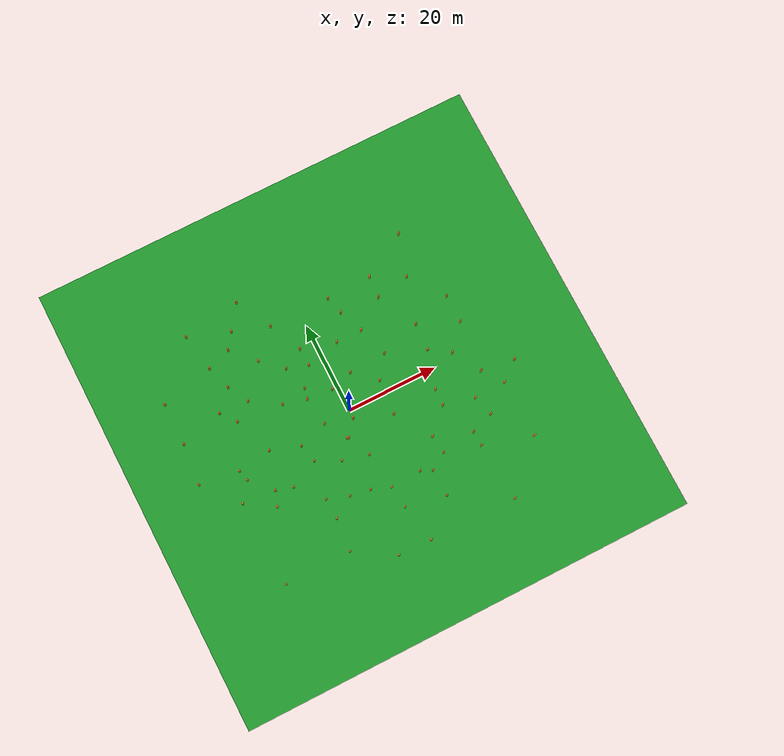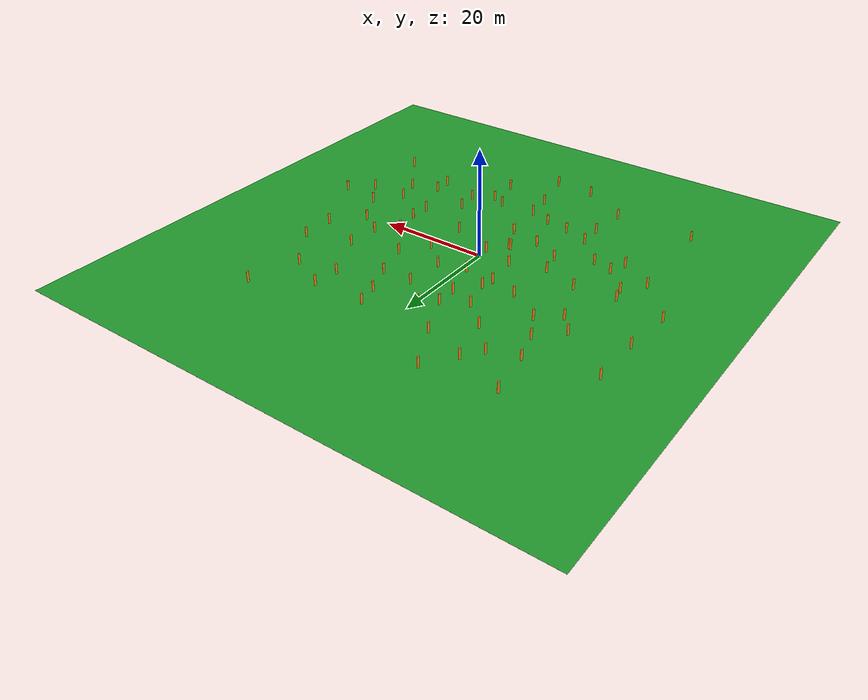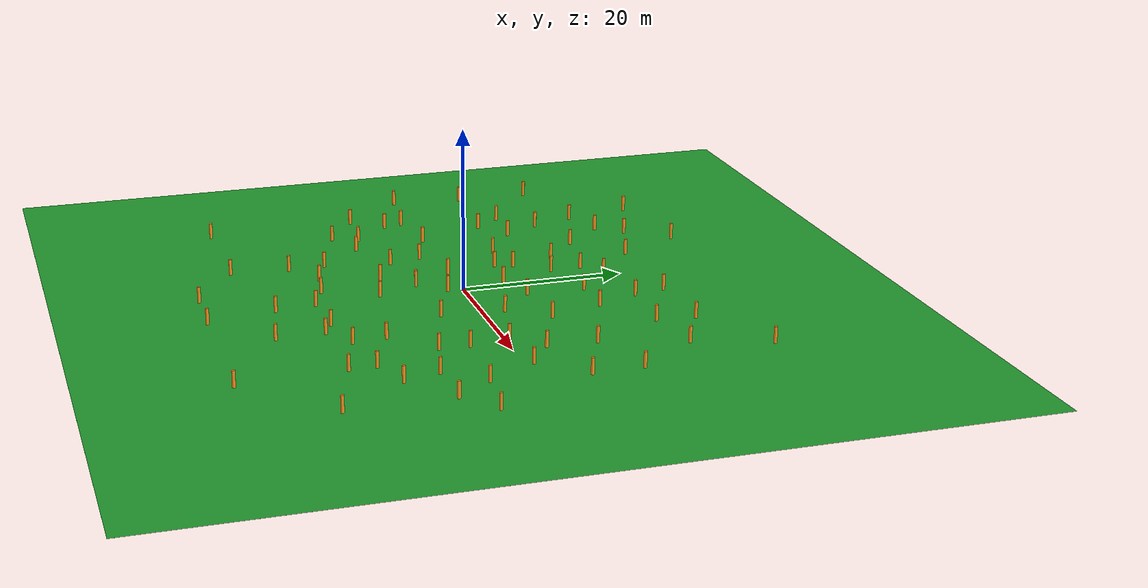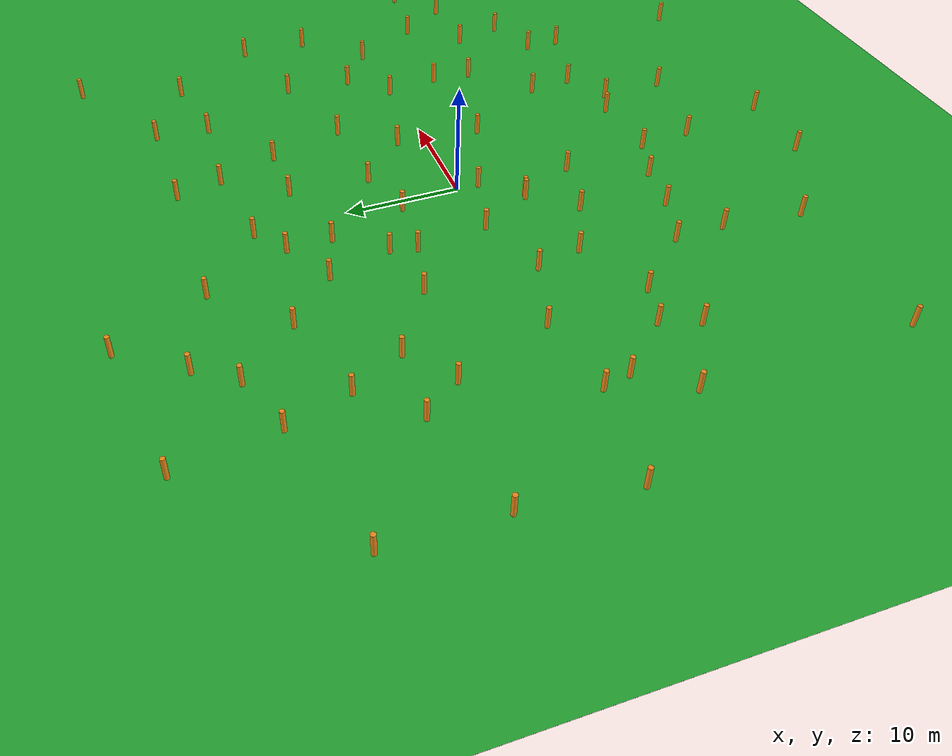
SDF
<?xml version='1.0'?>
<sdf version='1.6'>
  <model name='Skog'>
    <link name='link_0'>
      <inertial>
        <mass>1</mass>
        <inertia>
          <ixx>0.166667</ixx>
          <ixy>0</ixy>
          <ixz>0</ixz>
          <iyy>0.166667</iyy>
          <iyz>0</iyz>
          <izz>0.166667</izz>
        </inertia>
        <pose frame=''>0 0 0 0 -0 0</pose>
      </inertial>
      <pose frame=''>2.73107 1.22755 0 0 -0 0</pose>
      <gravity>1</gravity>
      <self_collide>0</self_collide>
      <kinematic>0</kinematic>
      <enable_wind>0</enable_wind>
      <visual name='visual'>
        <pose frame=''>0 0 0 0 -0 0</pose>
        <geometry>
          <box>
            <size>100 100 0.01</size>
          </box>
        </geometry>
        <material>
          <lighting>1</lighting>
          <script>
            <uri>file://media/materials/scripts/gazebo.material</uri>
            <name>Gazebo/Green</name>
          </script>
          <shader type='vertex'>
            <normal_map>__default__</normal_map>
          </shader>
          <ambient>0.3 0.3 0.3 1</ambient>
          <diffuse>0.7 0.7 0.7 1</diffuse>
          <specular>0.01 0.01 0.01 1</specular>
          <emissive>0 0 0 1</emissive>
        </material>
        <transparency>0</transparency>
        <cast_shadows>1</cast_shadows>
      </visual>
      <collision name='collision'>
        <laser_retro>0</laser_retro>
        <max_contacts>10</max_contacts>
        <pose frame=''>0 0 0 0 -0 0</pose>
        <geometry>
          <box>
            <size>100 100 0.01</size>
          </box>
        </geometry>
        <surface>
          <friction>
            <ode>
              <mu>1</mu>
              <mu2>1</mu2>
              <fdir1>0 0 0</fdir1>
              <slip1>0</slip1>
              <slip2>0</slip2>
            </ode>
            <torsional>
              <coefficient>1</coefficient>
              <patch_radius>0</patch_radius>
              <surface_radius>0</surface_radius>
              <use_patch_radius>1</use_patch_radius>
              <ode>
                <slip>0</slip>
              </ode>
            </torsional>
          </friction>
          <bounce>
            <restitution_coefficient>0</restitution_coefficient>
            <threshold>1e+06</threshold>
          </bounce>
          <contact>
            <collide_without_contact>0</collide_without_contact>
            <collide_without_contact_bitmask>1</collide_without_contact_bitmask>
            <collide_bitmask>1</collide_bitmask>
            <ode>
              <soft_cfm>0</soft_cfm>
              <soft_erp>0.2</soft_erp>
              <kp>1e+13</kp>
              <kd>1</kd>
              <max_vel>0.01</max_vel>
              <min_depth>0</min_depth>
            </ode>
            <bullet>
              <split_impulse>1</split_impulse>
              <split_impulse_penetration_threshold>-0.01</split_impulse_penetration_threshold>
              <soft_cfm>0</soft_cfm>
              <soft_erp>0.2</soft_erp>
              <kp>1e+13</kp>
              <kd>1</kd>
            </bullet>
          </contact>
        </surface>
      </collision>
    </link>
    <link name='link_1'>
      <inertial>
        <mass>1</mass>
        <inertia>
          <ixx>0.145833</ixx>
          <ixy>0</ixy>
          <ixz>0</ixz>
          <iyy>0.145833</iyy>
          <iyz>0</iyz>
          <izz>0.125</izz>
        </inertia>
        <pose frame=''>0 0 0 0 -0 0</pose>
      </inertial>
      <pose frame=''>-0.568148 -10.2215 0 0 -0 0</pose>
      <gravity>1</gravity>
      <self_collide>0</self_collide>
      <kinematic>0</kinematic>
      <enable_wind>0</enable_wind>
      <visual name='visual'>
        <pose frame=''>0 0 0 0 -0 0</pose>
        <geometry>
          <cylinder>
            <radius>0.2</radius>
            <length>4</length>
          </cylinder>
        </geometry>
        <material>
          <lighting>1</lighting>
          <script>
            <uri>file://media/materials/scripts/gazebo.material</uri>
            <name>Gazebo/Orange</name>
          </script>
          <shader type='vertex'>
            <normal_map>__default__</normal_map>
          </shader>
          <ambient>0.3 0.3 0.3 1</ambient>
          <diffuse>0.7 0.7 0.7 1</diffuse>
          <specular>0.01 0.01 0.01 1</specular>
          <emissive>0 0 0 1</emissive>
        </material>
        <transparency>0</transparency>
        <cast_shadows>1</cast_shadows>
      </visual>
      <collision name='collision'>
        <laser_retro>0</laser_retro>
        <max_contacts>10</max_contacts>
        <pose frame=''>0 0 0 0 -0 0</pose>
        <geometry>
          <cylinder>
            <radius>0.2</radius>
            <length>4</length>
          </cylinder>
        </geometry>
        <surface>
          <friction>
            <ode>
              <mu>1</mu>
              <mu2>1</mu2>
              <fdir1>0 0 0</fdir1>
              <slip1>0</slip1>
              <slip2>0</slip2>
            </ode>
            <torsional>
              <coefficient>1</coefficient>
              <patch_radius>0</patch_radius>
              <surface_radius>0</surface_radius>
              <use_patch_radius>1</use_patch_radius>
              <ode>
                <slip>0</slip>
              </ode>
            </torsional>
          </friction>
          <bounce>
            <restitution_coefficient>0</restitution_coefficient>
            <threshold>1e+06</threshold>
          </bounce>
          <contact>
            <collide_without_contact>0</collide_without_contact>
            <collide_without_contact_bitmask>1</collide_without_contact_bitmask>
            <collide_bitmask>1</collide_bitmask>
            <ode>
              <soft_cfm>0</soft_cfm>
              <soft_erp>0.2</soft_erp>
              <kp>1e+13</kp>
              <kd>1</kd>
              <max_vel>0.01</max_vel>
              <min_depth>0</min_depth>
            </ode>
            <bullet>
              <split_impulse>1</split_impulse>
              <split_impulse_penetration_threshold>-0.01</split_impulse_penetration_threshold>
              <soft_cfm>0</soft_cfm>
              <soft_erp>0.2</soft_erp>
              <kp>1e+13</kp>
              <kd>1</kd>
            </bullet>
          </contact>
        </surface>
      </collision>
    </link>
    <link name='link_1_clone'>
      <inertial>
        <mass>1</mass>
        <inertia>
          <ixx>0.145833</ixx>
          <ixy>0</ixy>
          <ixz>0</ixz>
          <iyy>0.145833</iyy>
          <iyz>0</iyz>
          <izz>0.125</izz>
        </inertia>
        <pose frame=''>0 0 0 0 -0 0</pose>
      </inertial>
      <pose frame=''>7.77562 -4.95725 0 0 -0 0</pose>
      <gravity>1</gravity>
      <self_collide>0</self_collide>
      <kinematic>0</kinematic>
      <enable_wind>0</enable_wind>
      <visual name='visual'>
        <pose frame=''>0 0 0 0 -0 0</pose>
        <geometry>
          <cylinder>
            <radius>0.2</radius>
            <length>4</length>
          </cylinder>
        </geometry>
        <material>
          <lighting>1</lighting>
          <script>
            <uri>file://media/materials/scripts/gazebo.material</uri>
            <name>Gazebo/Orange</name>
          </script>
          <shader type='vertex'>
            <normal_map>__default__</normal_map>
          </shader>
          <ambient>0.3 0.3 0.3 1</ambient>
          <diffuse>0.7 0.7 0.7 1</diffuse>
          <specular>0.01 0.01 0.01 1</specular>
          <emissive>0 0 0 1</emissive>
        </material>
        <transparency>0</transparency>
        <cast_shadows>1</cast_shadows>
      </visual>
      <collision name='collision'>
        <laser_retro>0</laser_retro>
        <max_contacts>10</max_contacts>
        <pose frame=''>0 0 0 0 -0 0</pose>
        <geometry>
          <cylinder>
            <radius>0.2</radius>
            <length>4</length>
          </cylinder>
        </geometry>
        <surface>
          <friction>
            <ode>
              <mu>1</mu>
              <mu2>1</mu2>
              <fdir1>0 0 0</fdir1>
              <slip1>0</slip1>
              <slip2>0</slip2>
            </ode>
            <torsional>
              <coefficient>1</coefficient>
              <patch_radius>0</patch_radius>
              <surface_radius>0</surface_radius>
              <use_patch_radius>1</use_patch_radius>
              <ode>
                <slip>0</slip>
              </ode>
            </torsional>
          </friction>
          <bounce>
            <restitution_coefficient>0</restitution_coefficient>
            <threshold>1e+06</threshold>
          </bounce>
          <contact>
            <collide_without_contact>0</collide_without_contact>
            <collide_without_contact_bitmask>1</collide_without_contact_bitmask>
            <collide_bitmask>1</collide_bitmask>
            <ode>
              <soft_cfm>0</soft_cfm>
              <soft_erp>0.2</soft_erp>
              <kp>1e+13</kp>
              <kd>1</kd>
              <max_vel>0.01</max_vel>
              <min_depth>0</min_depth>
            </ode>
            <bullet>
              <split_impulse>1</split_impulse>
              <split_impulse_penetration_threshold>-0.01</split_impulse_penetration_threshold>
              <soft_cfm>0</soft_cfm>
              <soft_erp>0.2</soft_erp>
              <kp>1e+13</kp>
              <kd>1</kd>
            </bullet>
          </contact>
        </surface>
      </collision>
    </link>
    <link name='link_1_clone_0'>
      <inertial>
        <mass>1</mass>
        <inertia>
          <ixx>0.145833</ixx>
          <ixy>0</ixy>
          <ixz>0</ixz>
          <iyy>0.145833</iyy>
          <iyz>0</iyz>
          <izz>0.125</izz>
        </inertia>
        <pose frame=''>0 0 0 0 -0 0</pose>
      </inertial>
      <pose frame=''>11.9089 7.35334 0 0 -0 0</pose>
      <gravity>1</gravity>
      <self_collide>0</self_collide>
      <kinematic>0</kinematic>
      <enable_wind>0</enable_wind>
      <visual name='visual'>
        <pose frame=''>0 0 0 0 -0 0</pose>
        <geometry>
          <cylinder>
            <radius>0.2</radius>
            <length>4</length>
          </cylinder>
        </geometry>
        <material>
          <lighting>1</lighting>
          <script>
            <uri>file://media/materials/scripts/gazebo.material</uri>
            <name>Gazebo/Orange</name>
          </script>
          <shader type='vertex'>
            <normal_map>__default__</normal_map>
          </shader>
          <ambient>0.3 0.3 0.3 1</ambient>
          <diffuse>0.7 0.7 0.7 1</diffuse>
          <specular>0.01 0.01 0.01 1</specular>
          <emissive>0 0 0 1</emissive>
        </material>
        <transparency>0</transparency>
        <cast_shadows>1</cast_shadows>
      </visual>
      <collision name='collision'>
        <laser_retro>0</laser_retro>
        <max_contacts>10</max_contacts>
        <pose frame=''>0 0 0 0 -0 0</pose>
        <geometry>
          <cylinder>
            <radius>0.2</radius>
            <length>4</length>
          </cylinder>
        </geometry>
        <surface>
          <friction>
            <ode>
              <mu>1</mu>
              <mu2>1</mu2>
              <fdir1>0 0 0</fdir1>
              <slip1>0</slip1>
              <slip2>0</slip2>
            </ode>
            <torsional>
              <coefficient>1</coefficient>
              <patch_radius>0</patch_radius>
              <surface_radius>0</surface_radius>
              <use_patch_radius>1</use_patch_radius>
              <ode>
                <slip>0</slip>
              </ode>
            </torsional>
          </friction>
          <bounce>
            <restitution_coefficient>0</restitution_coefficient>
            <threshold>1e+06</threshold>
          </bounce>
          <contact>
            <collide_without_contact>0</collide_without_contact>
            <collide_without_contact_bitmask>1</collide_without_contact_bitmask>
            <collide_bitmask>1</collide_bitmask>
            <ode>
              <soft_cfm>0</soft_cfm>
              <soft_erp>0.2</soft_erp>
              <kp>1e+13</kp>
              <kd>1</kd>
              <max_vel>0.01</max_vel>
              <min_depth>0</min_depth>
            </ode>
            <bullet>
              <split_impulse>1</split_impulse>
              <split_impulse_penetration_threshold>-0.01</split_impulse_penetration_threshold>
              <soft_cfm>0</soft_cfm>
              <soft_erp>0.2</soft_erp>
              <kp>1e+13</kp>
              <kd>1</kd>
            </bullet>
          </contact>
        </surface>
      </collision>
    </link>
    <link name='link_1_clone_1'>
      <inertial>
        <mass>1</mass>
        <inertia>
          <ixx>0.145833</ixx>
          <ixy>0</ixy>
          <ixz>0</ixz>
          <iyy>0.145833</iyy>
          <iyz>0</iyz>
          <izz>0.125</izz>
        </inertia>
        <pose frame=''>0 0 0 0 -0 0</pose>
      </inertial>
      <pose frame=''>-0.149763 -1.91257 0 0 -0 0</pose>
      <gravity>1</gravity>
      <self_collide>0</self_collide>
      <kinematic>0</kinematic>
      <enable_wind>0</enable_wind>
      <visual name='visual'>
        <pose frame=''>0 0 0 0 -0 0</pose>
        <geometry>
          <cylinder>
            <radius>0.2</radius>
            <length>4</length>
          </cylinder>
        </geometry>
        <material>
          <lighting>1</lighting>
          <script>
            <uri>file://media/materials/scripts/gazebo.material</uri>
            <name>Gazebo/Orange</name>
          </script>
          <shader type='vertex'>
            <normal_map>__default__</normal_map>
          </shader>
          <ambient>0.3 0.3 0.3 1</ambient>
          <diffuse>0.7 0.7 0.7 1</diffuse>
          <specular>0.01 0.01 0.01 1</specular>
          <emissive>0 0 0 1</emissive>
        </material>
        <transparency>0</transparency>
        <cast_shadows>1</cast_shadows>
      </visual>
      <collision name='collision'>
        <laser_retro>0</laser_retro>
        <max_contacts>10</max_contacts>
        <pose frame=''>0 0 0 0 -0 0</pose>
        <geometry>
          <cylinder>
            <radius>0.2</radius>
            <length>4</length>
          </cylinder>
        </geometry>
        <surface>
          <friction>
            <ode>
              <mu>1</mu>
              <mu2>1</mu2>
              <fdir1>0 0 0</fdir1>
              <slip1>0</slip1>
              <slip2>0</slip2>
            </ode>
            <torsional>
              <coefficient>1</coefficient>
              <patch_radius>0</patch_radius>
              <surface_radius>0</surface_radius>
              <use_patch_radius>1</use_patch_radius>
              <ode>
                <slip>0</slip>
              </ode>
            </torsional>
          </friction>
          <bounce>
            <restitution_coefficient>0</restitution_coefficient>
            <threshold>1e+06</threshold>
          </bounce>
          <contact>
            <collide_without_contact>0</collide_without_contact>
            <collide_without_contact_bitmask>1</collide_without_contact_bitmask>
            <collide_bitmask>1</collide_bitmask>
            <ode>
              <soft_cfm>0</soft_cfm>
              <soft_erp>0.2</soft_erp>
              <kp>1e+13</kp>
              <kd>1</kd>
              <max_vel>0.01</max_vel>
              <min_depth>0</min_depth>
            </ode>
            <bullet>
              <split_impulse>1</split_impulse>
              <split_impulse_penetration_threshold>-0.01</split_impulse_penetration_threshold>
              <soft_cfm>0</soft_cfm>
              <soft_erp>0.2</soft_erp>
              <kp>1e+13</kp>
              <kd>1</kd>
            </bullet>
          </contact>
        </surface>
      </collision>
    </link>
    <link name='link_1_clone_10'>
      <inertial>
        <mass>1</mass>
        <inertia>
          <ixx>0.145833</ixx>
          <ixy>0</ixy>
          <ixz>0</ixz>
          <iyy>0.145833</iyy>
          <iyz>0</iyz>
          <izz>0.125</izz>
        </inertia>
        <pose frame=''>0 0 0 0 -0 0</pose>
      </inertial>
      <pose frame=''>-5.94594 -0.285564 0 0 -0 0</pose>
      <gravity>1</gravity>
      <self_collide>0</self_collide>
      <kinematic>0</kinematic>
      <enable_wind>0</enable_wind>
      <visual name='visual'>
        <pose frame=''>0 0 0 0 -0 0</pose>
        <geometry>
          <cylinder>
            <radius>0.2</radius>
            <length>4</length>
          </cylinder>
        </geometry>
        <material>
          <lighting>1</lighting>
          <script>
            <uri>file://media/materials/scripts/gazebo.material</uri>
            <name>Gazebo/Orange</name>
          </script>
          <shader type='vertex'>
            <normal_map>__default__</normal_map>
          </shader>
          <ambient>0.3 0.3 0.3 1</ambient>
          <diffuse>0.7 0.7 0.7 1</diffuse>
          <specular>0.01 0.01 0.01 1</specular>
          <emissive>0 0 0 1</emissive>
        </material>
        <transparency>0</transparency>
        <cast_shadows>1</cast_shadows>
      </visual>
      <collision name='collision'>
        <laser_retro>0</laser_retro>
        <max_contacts>10</max_contacts>
        <pose frame=''>0 0 0 0 -0 0</pose>
        <geometry>
          <cylinder>
            <radius>0.2</radius>
            <length>4</length>
          </cylinder>
        </geometry>
        <surface>
          <friction>
            <ode>
              <mu>1</mu>
              <mu2>1</mu2>
              <fdir1>0 0 0</fdir1>
              <slip1>0</slip1>
              <slip2>0</slip2>
            </ode>
            <torsional>
              <coefficient>1</coefficient>
              <patch_radius>0</patch_radius>
              <surface_radius>0</surface_radius>
              <use_patch_radius>1</use_patch_radius>
              <ode>
                <slip>0</slip>
              </ode>
            </torsional>
          </friction>
          <bounce>
            <restitution_coefficient>0</restitution_coefficient>
            <threshold>1e+06</threshold>
          </bounce>
          <contact>
            <collide_without_contact>0</collide_without_contact>
            <collide_without_contact_bitmask>1</collide_without_contact_bitmask>
            <collide_bitmask>1</collide_bitmask>
            <ode>
              <soft_cfm>0</soft_cfm>
              <soft_erp>0.2</soft_erp>
              <kp>1e+13</kp>
              <kd>1</kd>
              <max_vel>0.01</max_vel>
              <min_depth>0</min_depth>
            </ode>
            <bullet>
              <split_impulse>1</split_impulse>
              <split_impulse_penetration_threshold>-0.01</split_impulse_penetration_threshold>
              <soft_cfm>0</soft_cfm>
              <soft_erp>0.2</soft_erp>
              <kp>1e+13</kp>
              <kd>1</kd>
            </bullet>
          </contact>
        </surface>
      </collision>
    </link>
    <link name='link_1_clone_11'>
      <inertial>
        <mass>1</mass>
        <inertia>
          <ixx>0.145833</ixx>
          <ixy>0</ixy>
          <ixz>0</ixz>
          <iyy>0.145833</iyy>
          <iyz>0</iyz>
          <izz>0.125</izz>
        </inertia>
        <pose frame=''>0 0 0 0 -0 0</pose>
      </inertial>
      <pose frame=''>24.3766 -9.59986 0 0 -0 0</pose>
      <gravity>1</gravity>
      <self_collide>0</self_collide>
      <kinematic>0</kinematic>
      <enable_wind>0</enable_wind>
      <visual name='visual'>
        <pose frame=''>0 0 0 0 -0 0</pose>
        <geometry>
          <cylinder>
            <radius>0.2</radius>
            <length>4</length>
          </cylinder>
        </geometry>
        <material>
          <lighting>1</lighting>
          <script>
            <uri>file://media/materials/scripts/gazebo.material</uri>
            <name>Gazebo/Orange</name>
          </script>
          <shader type='vertex'>
            <normal_map>__default__</normal_map>
          </shader>
          <ambient>0.3 0.3 0.3 1</ambient>
          <diffuse>0.7 0.7 0.7 1</diffuse>
          <specular>0.01 0.01 0.01 1</specular>
          <emissive>0 0 0 1</emissive>
        </material>
        <transparency>0</transparency>
        <cast_shadows>1</cast_shadows>
      </visual>
      <collision name='collision'>
        <laser_retro>0</laser_retro>
        <max_contacts>10</max_contacts>
        <pose frame=''>0 0 0 0 -0 0</pose>
        <geometry>
          <cylinder>
            <radius>0.2</radius>
            <length>4</length>
          </cylinder>
        </geometry>
        <surface>
          <friction>
            <ode>
              <mu>1</mu>
              <mu2>1</mu2>
              <fdir1>0 0 0</fdir1>
              <slip1>0</slip1>
              <slip2>0</slip2>
            </ode>
            <torsional>
              <coefficient>1</coefficient>
              <patch_radius>0</patch_radius>
              <surface_radius>0</surface_radius>
              <use_patch_radius>1</use_patch_radius>
              <ode>
                <slip>0</slip>
              </ode>
            </torsional>
          </friction>
          <bounce>
            <restitution_coefficient>0</restitution_coefficient>
            <threshold>1e+06</threshold>
          </bounce>
          <contact>
            <collide_without_contact>0</collide_without_contact>
            <collide_without_contact_bitmask>1</collide_without_contact_bitmask>
            <collide_bitmask>1</collide_bitmask>
            <ode>
              <soft_cfm>0</soft_cfm>
              <soft_erp>0.2</soft_erp>
              <kp>1e+13</kp>
              <kd>1</kd>
              <max_vel>0.01</max_vel>
              <min_depth>0</min_depth>
            </ode>
            <bullet>
              <split_impulse>1</split_impulse>
              <split_impulse_penetration_threshold>-0.01</split_impulse_penetration_threshold>
              <soft_cfm>0</soft_cfm>
              <soft_erp>0.2</soft_erp>
              <kp>1e+13</kp>
              <kd>1</kd>
            </bullet>
          </contact>
        </surface>
      </collision>
    </link>
    <link name='link_1_clone_12'>
      <inertial>
        <mass>1</mass>
        <inertia>
          <ixx>0.145833</ixx>
          <ixy>0</ixy>
          <ixz>0</ixz>
          <iyy>0.145833</iyy>
          <iyz>0</iyz>
          <izz>0.125</izz>
        </inertia>
        <pose frame=''>0 0 0 0 -0 0</pose>
      </inertial>
      <pose frame=''>20.5936 9.88843 0 0 -0 0</pose>
      <gravity>1</gravity>
      <self_collide>0</self_collide>
      <kinematic>0</kinematic>
      <enable_wind>0</enable_wind>
      <visual name='visual'>
        <pose frame=''>0 0 0 0 -0 0</pose>
        <geometry>
          <cylinder>
            <radius>0.2</radius>
            <length>4</length>
          </cylinder>
        </geometry>
        <material>
          <lighting>1</lighting>
          <script>
            <uri>file://media/materials/scripts/gazebo.material</uri>
            <name>Gazebo/Orange</name>
          </script>
          <shader type='vertex'>
            <normal_map>__default__</normal_map>
          </shader>
          <ambient>0.3 0.3 0.3 1</ambient>
          <diffuse>0.7 0.7 0.7 1</diffuse>
          <specular>0.01 0.01 0.01 1</specular>
          <emissive>0 0 0 1</emissive>
        </material>
        <transparency>0</transparency>
        <cast_shadows>1</cast_shadows>
      </visual>
      <collision name='collision'>
        <laser_retro>0</laser_retro>
        <max_contacts>10</max_contacts>
        <pose frame=''>0 0 0 0 -0 0</pose>
        <geometry>
          <cylinder>
            <radius>0.2</radius>
            <length>4</length>
          </cylinder>
        </geometry>
        <surface>
          <friction>
            <ode>
              <mu>1</mu>
              <mu2>1</mu2>
              <fdir1>0 0 0</fdir1>
              <slip1>0</slip1>
              <slip2>0</slip2>
            </ode>
            <torsional>
              <coefficient>1</coefficient>
              <patch_radius>0</patch_radius>
              <surface_radius>0</surface_radius>
              <use_patch_radius>1</use_patch_radius>
              <ode>
                <slip>0</slip>
              </ode>
            </torsional>
          </friction>
          <bounce>
            <restitution_coefficient>0</restitution_coefficient>
            <threshold>1e+06</threshold>
          </bounce>
          <contact>
            <collide_without_contact>0</collide_without_contact>
            <collide_without_contact_bitmask>1</collide_without_contact_bitmask>
            <collide_bitmask>1</collide_bitmask>
            <ode>
              <soft_cfm>0</soft_cfm>
              <soft_erp>0.2</soft_erp>
              <kp>1e+13</kp>
              <kd>1</kd>
              <max_vel>0.01</max_vel>
              <min_depth>0</min_depth>
            </ode>
            <bullet>
              <split_impulse>1</split_impulse>
              <split_impulse_penetration_threshold>-0.01</split_impulse_penetration_threshold>
              <soft_cfm>0</soft_cfm>
              <soft_erp>0.2</soft_erp>
              <kp>1e+13</kp>
              <kd>1</kd>
            </bullet>
          </contact>
        </surface>
      </collision>
    </link>
    <link name='link_1_clone_13'>
      <inertial>
        <mass>1</mass>
        <inertia>
          <ixx>0.145833</ixx>
          <ixy>0</ixy>
          <ixz>0</ixz>
          <iyy>0.145833</iyy>
          <iyz>0</iyz>
          <izz>0.125</izz>
        </inertia>
        <pose frame=''>0 0 0 0 -0 0</pose>
      </inertial>
      <pose frame=''>9.79022 13.9959 0 0 -0 0</pose>
      <gravity>1</gravity>
      <self_collide>0</self_collide>
      <kinematic>0</kinematic>
      <enable_wind>0</enable_wind>
      <visual name='visual'>
        <pose frame=''>0 0 0 0 -0 0</pose>
        <geometry>
          <cylinder>
            <radius>0.2</radius>
            <length>4</length>
          </cylinder>
        </geometry>
        <material>
          <lighting>1</lighting>
          <script>
            <uri>file://media/materials/scripts/gazebo.material</uri>
            <name>Gazebo/Orange</name>
          </script>
          <shader type='vertex'>
            <normal_map>__default__</normal_map>
          </shader>
          <ambient>0.3 0.3 0.3 1</ambient>
          <diffuse>0.7 0.7 0.7 1</diffuse>
          <specular>0.01 0.01 0.01 1</specular>
          <emissive>0 0 0 1</emissive>
        </material>
        <transparency>0</transparency>
        <cast_shadows>1</cast_shadows>
      </visual>
      <collision name='collision'>
        <laser_retro>0</laser_retro>
        <max_contacts>10</max_contacts>
        <pose frame=''>0 0 0 0 -0 0</pose>
        <geometry>
          <cylinder>
            <radius>0.2</radius>
            <length>4</length>
          </cylinder>
        </geometry>
        <surface>
          <friction>
            <ode>
              <mu>1</mu>
              <mu2>1</mu2>
              <fdir1>0 0 0</fdir1>
              <slip1>0</slip1>
              <slip2>0</slip2>
            </ode>
            <torsional>
              <coefficient>1</coefficient>
              <patch_radius>0</patch_radius>
              <surface_radius>0</surface_radius>
              <use_patch_radius>1</use_patch_radius>
              <ode>
                <slip>0</slip>
              </ode>
            </torsional>
          </friction>
          <bounce>
            <restitution_coefficient>0</restitution_coefficient>
            <threshold>1e+06</threshold>
          </bounce>
          <contact>
            <collide_without_contact>0</collide_without_contact>
            <collide_without_contact_bitmask>1</collide_without_contact_bitmask>
            <collide_bitmask>1</collide_bitmask>
            <ode>
              <soft_cfm>0</soft_cfm>
              <soft_erp>0.2</soft_erp>
              <kp>1e+13</kp>
              <kd>1</kd>
              <max_vel>0.01</max_vel>
              <min_depth>0</min_depth>
            </ode>
            <bullet>
              <split_impulse>1</split_impulse>
              <split_impulse_penetration_threshold>-0.01</split_impulse_penetration_threshold>
              <soft_cfm>0</soft_cfm>
              <soft_erp>0.2</soft_erp>
              <kp>1e+13</kp>
              <kd>1</kd>
            </bullet>
          </contact>
        </surface>
      </collision>
    </link>
    <link name='link_1_clone_14'>
      <inertial>
        <mass>1</mass>
        <inertia>
          <ixx>0.145833</ixx>
          <ixy>0</ixy>
          <ixz>0</ixz>
          <iyy>0.145833</iyy>
          <iyz>0</iyz>
          <izz>0.125</izz>
        </inertia>
        <pose frame=''>0 0 0 0 -0 0</pose>
      </inertial>
      <pose frame=''>-7.81095 13.715 0 0 -0 0</pose>
      <gravity>1</gravity>
      <self_collide>0</self_collide>
      <kinematic>0</kinematic>
      <enable_wind>0</enable_wind>
      <visual name='visual'>
        <pose frame=''>0 0 0 0 -0 0</pose>
        <geometry>
          <cylinder>
            <radius>0.2</radius>
            <length>4</length>
          </cylinder>
        </geometry>
        <material>
          <lighting>1</lighting>
          <script>
            <uri>file://media/materials/scripts/gazebo.material</uri>
            <name>Gazebo/Orange</name>
          </script>
          <shader type='vertex'>
            <normal_map>__default__</normal_map>
          </shader>
          <ambient>0.3 0.3 0.3 1</ambient>
          <diffuse>0.7 0.7 0.7 1</diffuse>
          <specular>0.01 0.01 0.01 1</specular>
          <emissive>0 0 0 1</emissive>
        </material>
        <transparency>0</transparency>
        <cast_shadows>1</cast_shadows>
      </visual>
      <collision name='collision'>
        <laser_retro>0</laser_retro>
        <max_contacts>10</max_contacts>
        <pose frame=''>0 0 0 0 -0 0</pose>
        <geometry>
          <cylinder>
            <radius>0.2</radius>
            <length>4</length>
          </cylinder>
        </geometry>
        <surface>
          <friction>
            <ode>
              <mu>1</mu>
              <mu2>1</mu2>
              <fdir1>0 0 0</fdir1>
              <slip1>0</slip1>
              <slip2>0</slip2>
            </ode>
            <torsional>
              <coefficient>1</coefficient>
              <patch_radius>0</patch_radius>
              <surface_radius>0</surface_radius>
              <use_patch_radius>1</use_patch_radius>
              <ode>
                <slip>0</slip>
              </ode>
            </torsional>
          </friction>
          <bounce>
            <restitution_coefficient>0</restitution_coefficient>
            <threshold>1e+06</threshold>
          </bounce>
          <contact>
            <collide_without_contact>0</collide_without_contact>
            <collide_without_contact_bitmask>1</collide_without_contact_bitmask>
            <collide_bitmask>1</collide_bitmask>
            <ode>
              <soft_cfm>0</soft_cfm>
              <soft_erp>0.2</soft_erp>
              <kp>1e+13</kp>
              <kd>1</kd>
              <max_vel>0.01</max_vel>
              <min_depth>0</min_depth>
            </ode>
            <bullet>
              <split_impulse>1</split_impulse>
              <split_impulse_penetration_threshold>-0.01</split_impulse_penetration_threshold>
              <soft_cfm>0</soft_cfm>
              <soft_erp>0.2</soft_erp>
              <kp>1e+13</kp>
              <kd>1</kd>
            </bullet>
          </contact>
        </surface>
      </collision>
    </link>
    <link name='link_1_clone_15'>
      <inertial>
        <mass>1</mass>
        <inertia>
          <ixx>0.145833</ixx>
          <ixy>0</ixy>
          <ixz>0</ixz>
          <iyy>0.145833</iyy>
          <iyz>0</iyz>
          <izz>0.125</izz>
        </inertia>
        <pose frame=''>0 0 0 0 -0 0</pose>
      </inertial>
      <pose frame=''>-3.26893 12.2276 0 0 -0 0</pose>
      <gravity>1</gravity>
      <self_collide>0</self_collide>
      <kinematic>0</kinematic>
      <enable_wind>0</enable_wind>
      <visual name='visual'>
        <pose frame=''>0 0 0 0 -0 0</pose>
        <geometry>
          <cylinder>
            <radius>0.2</radius>
            <length>4</length>
          </cylinder>
        </geometry>
        <material>
          <lighting>1</lighting>
          <script>
            <uri>file://media/materials/scripts/gazebo.material</uri>
            <name>Gazebo/Orange</name>
          </script>
          <shader type='vertex'>
            <normal_map>__default__</normal_map>
          </shader>
          <ambient>0.3 0.3 0.3 1</ambient>
          <diffuse>0.7 0.7 0.7 1</diffuse>
          <specular>0.01 0.01 0.01 1</specular>
          <emissive>0 0 0 1</emissive>
        </material>
        <transparency>0</transparency>
        <cast_shadows>1</cast_shadows>
      </visual>
      <collision name='collision'>
        <laser_retro>0</laser_retro>
        <max_contacts>10</max_contacts>
        <pose frame=''>0 0 0 0 -0 0</pose>
        <geometry>
          <cylinder>
            <radius>0.2</radius>
            <length>4</length>
          </cylinder>
        </geometry>
        <surface>
          <friction>
            <ode>
              <mu>1</mu>
              <mu2>1</mu2>
              <fdir1>0 0 0</fdir1>
              <slip1>0</slip1>
              <slip2>0</slip2>
            </ode>
            <torsional>
              <coefficient>1</coefficient>
              <patch_radius>0</patch_radius>
              <surface_radius>0</surface_radius>
              <use_patch_radius>1</use_patch_radius>
              <ode>
                <slip>0</slip>
              </ode>
            </torsional>
          </friction>
          <bounce>
            <restitution_coefficient>0</restitution_coefficient>
            <threshold>1e+06</threshold>
          </bounce>
          <contact>
            <collide_without_contact>0</collide_without_contact>
            <collide_without_contact_bitmask>1</collide_without_contact_bitmask>
            <collide_bitmask>1</collide_bitmask>
            <ode>
              <soft_cfm>0</soft_cfm>
              <soft_erp>0.2</soft_erp>
              <kp>1e+13</kp>
              <kd>1</kd>
              <max_vel>0.01</max_vel>
              <min_depth>0</min_depth>
            </ode>
            <bullet>
              <split_impulse>1</split_impulse>
              <split_impulse_penetration_threshold>-0.01</split_impulse_penetration_threshold>
              <soft_cfm>0</soft_cfm>
              <soft_erp>0.2</soft_erp>
              <kp>1e+13</kp>
              <kd>1</kd>
            </bullet>
          </contact>
        </surface>
      </collision>
    </link>
    <link name='link_1_clone_16'>
      <inertial>
        <mass>1</mass>
        <inertia>
          <ixx>0.145833</ixx>
          <ixy>0</ixy>
          <ixz>0</ixz>
          <iyy>0.145833</iyy>
          <iyz>0</iyz>
          <izz>0.125</izz>
        </inertia>
        <pose frame=''>0 0 0 0 -0 0</pose>
      </inertial>
      <pose frame=''>-3.38919 16.1063 0 0 -0 0</pose>
      <gravity>1</gravity>
      <self_collide>0</self_collide>
      <kinematic>0</kinematic>
      <enable_wind>0</enable_wind>
      <visual name='visual'>
        <pose frame=''>0 0 0 0 -0 0</pose>
        <geometry>
          <cylinder>
            <radius>0.2</radius>
            <length>4</length>
          </cylinder>
        </geometry>
        <material>
          <lighting>1</lighting>
          <script>
            <uri>file://media/materials/scripts/gazebo.material</uri>
            <name>Gazebo/Orange</name>
          </script>
          <shader type='vertex'>
            <normal_map>__default__</normal_map>
          </shader>
          <ambient>0.3 0.3 0.3 1</ambient>
          <diffuse>0.7 0.7 0.7 1</diffuse>
          <specular>0.01 0.01 0.01 1</specular>
          <emissive>0 0 0 1</emissive>
        </material>
        <transparency>0</transparency>
        <cast_shadows>1</cast_shadows>
      </visual>
      <collision name='collision'>
        <laser_retro>0</laser_retro>
        <max_contacts>10</max_contacts>
        <pose frame=''>0 0 0 0 -0 0</pose>
        <geometry>
          <cylinder>
            <radius>0.2</radius>
            <length>4</length>
          </cylinder>
        </geometry>
        <surface>
          <friction>
            <ode>
              <mu>1</mu>
              <mu2>1</mu2>
              <fdir1>0 0 0</fdir1>
              <slip1>0</slip1>
              <slip2>0</slip2>
            </ode>
            <torsional>
              <coefficient>1</coefficient>
              <patch_radius>0</patch_radius>
              <surface_radius>0</surface_radius>
              <use_patch_radius>1</use_patch_radius>
              <ode>
                <slip>0</slip>
              </ode>
            </torsional>
          </friction>
          <bounce>
            <restitution_coefficient>0</restitution_coefficient>
            <threshold>1e+06</threshold>
          </bounce>
          <contact>
            <collide_without_contact>0</collide_without_contact>
            <collide_without_contact_bitmask>1</collide_without_contact_bitmask>
            <collide_bitmask>1</collide_bitmask>
            <ode>
              <soft_cfm>0</soft_cfm>
              <soft_erp>0.2</soft_erp>
              <kp>1e+13</kp>
              <kd>1</kd>
              <max_vel>0.01</max_vel>
              <min_depth>0</min_depth>
            </ode>
            <bullet>
              <split_impulse>1</split_impulse>
              <split_impulse_penetration_threshold>-0.01</split_impulse_penetration_threshold>
              <soft_cfm>0</soft_cfm>
              <soft_erp>0.2</soft_erp>
              <kp>1e+13</kp>
              <kd>1</kd>
            </bullet>
          </contact>
        </surface>
      </collision>
    </link>
    <link name='link_1_clone_17'>
      <inertial>
        <mass>1</mass>
        <inertia>
          <ixx>0.145833</ixx>
          <ixy>0</ixy>
          <ixz>0</ixz>
          <iyy>0.145833</iyy>
          <iyz>0</iyz>
          <izz>0.125</izz>
        </inertia>
        <pose frame=''>0 0 0 0 -0 0</pose>
      </inertial>
      <pose frame=''>-11.8447 7.26937 0 0 -0 0</pose>
      <gravity>1</gravity>
      <self_collide>0</self_collide>
      <kinematic>0</kinematic>
      <enable_wind>0</enable_wind>
      <visual name='visual'>
        <pose frame=''>0 0 0 0 -0 0</pose>
        <geometry>
          <cylinder>
            <radius>0.2</radius>
            <length>4</length>
          </cylinder>
        </geometry>
        <material>
          <lighting>1</lighting>
          <script>
            <uri>file://media/materials/scripts/gazebo.material</uri>
            <name>Gazebo/Orange</name>
          </script>
          <shader type='vertex'>
            <normal_map>__default__</normal_map>
          </shader>
          <ambient>0.3 0.3 0.3 1</ambient>
          <diffuse>0.7 0.7 0.7 1</diffuse>
          <specular>0.01 0.01 0.01 1</specular>
          <emissive>0 0 0 1</emissive>
        </material>
        <transparency>0</transparency>
        <cast_shadows>1</cast_shadows>
      </visual>
      <collision name='collision'>
        <laser_retro>0</laser_retro>
        <max_contacts>10</max_contacts>
        <pose frame=''>0 0 0 0 -0 0</pose>
        <geometry>
          <cylinder>
            <radius>0.2</radius>
            <length>4</length>
          </cylinder>
        </geometry>
        <surface>
          <friction>
            <ode>
              <mu>1</mu>
              <mu2>1</mu2>
              <fdir1>0 0 0</fdir1>
              <slip1>0</slip1>
              <slip2>0</slip2>
            </ode>
            <torsional>
              <coefficient>1</coefficient>
              <patch_radius>0</patch_radius>
              <surface_radius>0</surface_radius>
              <use_patch_radius>1</use_patch_radius>
              <ode>
                <slip>0</slip>
              </ode>
            </torsional>
          </friction>
          <bounce>
            <restitution_coefficient>0</restitution_coefficient>
            <threshold>1e+06</threshold>
          </bounce>
          <contact>
            <collide_without_contact>0</collide_without_contact>
            <collide_without_contact_bitmask>1</collide_without_contact_bitmask>
            <collide_bitmask>1</collide_bitmask>
            <ode>
              <soft_cfm>0</soft_cfm>
              <soft_erp>0.2</soft_erp>
              <kp>1e+13</kp>
              <kd>1</kd>
              <max_vel>0.01</max_vel>
              <min_depth>0</min_depth>
            </ode>
            <bullet>
              <split_impulse>1</split_impulse>
              <split_impulse_penetration_threshold>-0.01</split_impulse_penetration_threshold>
              <soft_cfm>0</soft_cfm>
              <soft_erp>0.2</soft_erp>
              <kp>1e+13</kp>
              <kd>1</kd>
            </bullet>
          </contact>
        </surface>
      </collision>
    </link>
    <link name='link_1_clone_18'>
      <inertial>
        <mass>1</mass>
        <inertia>
          <ixx>0.145833</ixx>
          <ixy>0</ixy>
          <ixz>0</ixz>
          <iyy>0.145833</iyy>
          <iyz>0</iyz>
          <izz>0.125</izz>
        </inertia>
        <pose frame=''>0 0 0 0 -0 0</pose>
      </inertial>
      <pose frame=''>-11.2928 -6.29957 0 0 -0 0</pose>
      <gravity>1</gravity>
      <self_collide>0</self_collide>
      <kinematic>0</kinematic>
      <enable_wind>0</enable_wind>
      <visual name='visual'>
        <pose frame=''>0 0 0 0 -0 0</pose>
        <geometry>
          <cylinder>
            <radius>0.2</radius>
            <length>4</length>
          </cylinder>
        </geometry>
        <material>
          <lighting>1</lighting>
          <script>
            <uri>file://media/materials/scripts/gazebo.material</uri>
            <name>Gazebo/Orange</name>
          </script>
          <shader type='vertex'>
            <normal_map>__default__</normal_map>
          </shader>
          <ambient>0.3 0.3 0.3 1</ambient>
          <diffuse>0.7 0.7 0.7 1</diffuse>
          <specular>0.01 0.01 0.01 1</specular>
          <emissive>0 0 0 1</emissive>
        </material>
        <transparency>0</transparency>
        <cast_shadows>1</cast_shadows>
      </visual>
      <collision name='collision'>
        <laser_retro>0</laser_retro>
        <max_contacts>10</max_contacts>
        <pose frame=''>0 0 0 0 -0 0</pose>
        <geometry>
          <cylinder>
            <radius>0.2</radius>
            <length>4</length>
          </cylinder>
        </geometry>
        <surface>
          <friction>
            <ode>
              <mu>1</mu>
              <mu2>1</mu2>
              <fdir1>0 0 0</fdir1>
              <slip1>0</slip1>
              <slip2>0</slip2>
            </ode>
            <torsional>
              <coefficient>1</coefficient>
              <patch_radius>0</patch_radius>
              <surface_radius>0</surface_radius>
              <use_patch_radius>1</use_patch_radius>
              <ode>
                <slip>0</slip>
              </ode>
            </torsional>
          </friction>
          <bounce>
            <restitution_coefficient>0</restitution_coefficient>
            <threshold>1e+06</threshold>
          </bounce>
          <contact>
            <collide_without_contact>0</collide_without_contact>
            <collide_without_contact_bitmask>1</collide_without_contact_bitmask>
            <collide_bitmask>1</collide_bitmask>
            <ode>
              <soft_cfm>0</soft_cfm>
              <soft_erp>0.2</soft_erp>
              <kp>1e+13</kp>
              <kd>1</kd>
              <max_vel>0.01</max_vel>
              <min_depth>0</min_depth>
            </ode>
            <bullet>
              <split_impulse>1</split_impulse>
              <split_impulse_penetration_threshold>-0.01</split_impulse_penetration_threshold>
              <soft_cfm>0</soft_cfm>
              <soft_erp>0.2</soft_erp>
              <kp>1e+13</kp>
              <kd>1</kd>
            </bullet>
          </contact>
        </surface>
      </collision>
    </link>
    <link name='link_1_clone_19'>
      <inertial>
        <mass>1</mass>
        <inertia>
          <ixx>0.145833</ixx>
          <ixy>0</ixy>
          <ixz>0</ixz>
          <iyy>0.145833</iyy>
          <iyz>0</iyz>
          <izz>0.125</izz>
        </inertia>
        <pose frame=''>0 0 0 0 -0 0</pose>
      </inertial>
      <pose frame=''>-12.6949 -14.4232 0 0 -0 0</pose>
      <gravity>1</gravity>
      <self_collide>0</self_collide>
      <kinematic>0</kinematic>
      <enable_wind>0</enable_wind>
      <visual name='visual'>
        <pose frame=''>0 0 0 0 -0 0</pose>
        <geometry>
          <cylinder>
            <radius>0.2</radius>
            <length>4</length>
          </cylinder>
        </geometry>
        <material>
          <lighting>1</lighting>
          <script>
            <uri>file://media/materials/scripts/gazebo.material</uri>
            <name>Gazebo/Orange</name>
          </script>
          <shader type='vertex'>
            <normal_map>__default__</normal_map>
          </shader>
          <ambient>0.3 0.3 0.3 1</ambient>
          <diffuse>0.7 0.7 0.7 1</diffuse>
          <specular>0.01 0.01 0.01 1</specular>
          <emissive>0 0 0 1</emissive>
        </material>
        <transparency>0</transparency>
        <cast_shadows>1</cast_shadows>
      </visual>
      <collision name='collision'>
        <laser_retro>0</laser_retro>
        <max_contacts>10</max_contacts>
        <pose frame=''>0 0 0 0 -0 0</pose>
        <geometry>
          <cylinder>
            <radius>0.2</radius>
            <length>4</length>
          </cylinder>
        </geometry>
        <surface>
          <friction>
            <ode>
              <mu>1</mu>
              <mu2>1</mu2>
              <fdir1>0 0 0</fdir1>
              <slip1>0</slip1>
              <slip2>0</slip2>
            </ode>
            <torsional>
              <coefficient>1</coefficient>
              <patch_radius>0</patch_radius>
              <surface_radius>0</surface_radius>
              <use_patch_radius>1</use_patch_radius>
              <ode>
                <slip>0</slip>
              </ode>
            </torsional>
          </friction>
          <bounce>
            <restitution_coefficient>0</restitution_coefficient>
            <threshold>1e+06</threshold>
          </bounce>
          <contact>
            <collide_without_contact>0</collide_without_contact>
            <collide_without_contact_bitmask>1</collide_without_contact_bitmask>
            <collide_bitmask>1</collide_bitmask>
            <ode>
              <soft_cfm>0</soft_cfm>
              <soft_erp>0.2</soft_erp>
              <kp>1e+13</kp>
              <kd>1</kd>
              <max_vel>0.01</max_vel>
              <min_depth>0</min_depth>
            </ode>
            <bullet>
              <split_impulse>1</split_impulse>
              <split_impulse_penetration_threshold>-0.01</split_impulse_penetration_threshold>
              <soft_cfm>0</soft_cfm>
              <soft_erp>0.2</soft_erp>
              <kp>1e+13</kp>
              <kd>1</kd>
            </bullet>
          </contact>
        </surface>
      </collision>
    </link>
    <link name='link_1_clone_2'>
      <inertial>
        <mass>1</mass>
        <inertia>
          <ixx>0.145833</ixx>
          <ixy>0</ixy>
          <ixz>0</ixz>
          <iyy>0.145833</iyy>
          <iyz>0</iyz>
          <izz>0.125</izz>
        </inertia>
        <pose frame=''>0 0 0 0 -0 0</pose>
      </inertial>
      <pose frame=''>8.38938 2.66832 0 0 -0 0</pose>
      <gravity>1</gravity>
      <self_collide>0</self_collide>
      <kinematic>0</kinematic>
      <enable_wind>0</enable_wind>
      <visual name='visual'>
        <pose frame=''>0 0 0 0 -0 0</pose>
        <geometry>
          <cylinder>
            <radius>0.2</radius>
            <length>4</length>
          </cylinder>
        </geometry>
        <material>
          <lighting>1</lighting>
          <script>
            <uri>file://media/materials/scripts/gazebo.material</uri>
            <name>Gazebo/Orange</name>
          </script>
          <shader type='vertex'>
            <normal_map>__default__</normal_map>
          </shader>
          <ambient>0.3 0.3 0.3 1</ambient>
          <diffuse>0.7 0.7 0.7 1</diffuse>
          <specular>0.01 0.01 0.01 1</specular>
          <emissive>0 0 0 1</emissive>
        </material>
        <transparency>0</transparency>
        <cast_shadows>1</cast_shadows>
      </visual>
      <collision name='collision'>
        <laser_retro>0</laser_retro>
        <max_contacts>10</max_contacts>
        <pose frame=''>0 0 0 0 -0 0</pose>
        <geometry>
          <cylinder>
            <radius>0.2</radius>
            <length>4</length>
          </cylinder>
        </geometry>
        <surface>
          <friction>
            <ode>
              <mu>1</mu>
              <mu2>1</mu2>
              <fdir1>0 0 0</fdir1>
              <slip1>0</slip1>
              <slip2>0</slip2>
            </ode>
            <torsional>
              <coefficient>1</coefficient>
              <patch_radius>0</patch_radius>
              <surface_radius>0</surface_radius>
              <use_patch_radius>1</use_patch_radius>
              <ode>
                <slip>0</slip>
              </ode>
            </torsional>
          </friction>
          <bounce>
            <restitution_coefficient>0</restitution_coefficient>
            <threshold>1e+06</threshold>
          </bounce>
          <contact>
            <collide_without_contact>0</collide_without_contact>
            <collide_without_contact_bitmask>1</collide_without_contact_bitmask>
            <collide_bitmask>1</collide_bitmask>
            <ode>
              <soft_cfm>0</soft_cfm>
              <soft_erp>0.2</soft_erp>
              <kp>1e+13</kp>
              <kd>1</kd>
              <max_vel>0.01</max_vel>
              <min_depth>0</min_depth>
            </ode>
            <bullet>
              <split_impulse>1</split_impulse>
              <split_impulse_penetration_threshold>-0.01</split_impulse_penetration_threshold>
              <soft_cfm>0</soft_cfm>
              <soft_erp>0.2</soft_erp>
              <kp>1e+13</kp>
              <kd>1</kd>
            </bullet>
          </contact>
        </surface>
      </collision>
    </link>
    <link name='link_1_clone_20'>
      <inertial>
        <mass>1</mass>
        <inertia>
          <ixx>0.145833</ixx>
          <ixy>0</ixy>
          <ixz>0</ixz>
          <iyy>0.145833</iyy>
          <iyz>0</iyz>
          <izz>0.125</izz>
        </inertia>
        <pose frame=''>0 0 0 0 -0 0</pose>
      </inertial>
      <pose frame=''>-3.69424 -16.7724 0 0 -0 0</pose>
      <gravity>1</gravity>
      <self_collide>0</self_collide>
      <kinematic>0</kinematic>
      <enable_wind>0</enable_wind>
      <visual name='visual'>
        <pose frame=''>0 0 0 0 -0 0</pose>
        <geometry>
          <cylinder>
            <radius>0.2</radius>
            <length>4</length>
          </cylinder>
        </geometry>
        <material>
          <lighting>1</lighting>
          <script>
            <uri>file://media/materials/scripts/gazebo.material</uri>
            <name>Gazebo/Orange</name>
          </script>
          <shader type='vertex'>
            <normal_map>__default__</normal_map>
          </shader>
          <ambient>0.3 0.3 0.3 1</ambient>
          <diffuse>0.7 0.7 0.7 1</diffuse>
          <specular>0.01 0.01 0.01 1</specular>
          <emissive>0 0 0 1</emissive>
        </material>
        <transparency>0</transparency>
        <cast_shadows>1</cast_shadows>
      </visual>
      <collision name='collision'>
        <laser_retro>0</laser_retro>
        <max_contacts>10</max_contacts>
        <pose frame=''>0 0 0 0 -0 0</pose>
        <geometry>
          <cylinder>
            <radius>0.2</radius>
            <length>4</length>
          </cylinder>
        </geometry>
        <surface>
          <friction>
            <ode>
              <mu>1</mu>
              <mu2>1</mu2>
              <fdir1>0 0 0</fdir1>
              <slip1>0</slip1>
              <slip2>0</slip2>
            </ode>
            <torsional>
              <coefficient>1</coefficient>
              <patch_radius>0</patch_radius>
              <surface_radius>0</surface_radius>
              <use_patch_radius>1</use_patch_radius>
              <ode>
                <slip>0</slip>
              </ode>
            </torsional>
          </friction>
          <bounce>
            <restitution_coefficient>0</restitution_coefficient>
            <threshold>1e+06</threshold>
          </bounce>
          <contact>
            <collide_without_contact>0</collide_without_contact>
            <collide_without_contact_bitmask>1</collide_without_contact_bitmask>
            <collide_bitmask>1</collide_bitmask>
            <ode>
              <soft_cfm>0</soft_cfm>
              <soft_erp>0.2</soft_erp>
              <kp>1e+13</kp>
              <kd>1</kd>
              <max_vel>0.01</max_vel>
              <min_depth>0</min_depth>
            </ode>
            <bullet>
              <split_impulse>1</split_impulse>
              <split_impulse_penetration_threshold>-0.01</split_impulse_penetration_threshold>
              <soft_cfm>0</soft_cfm>
              <soft_erp>0.2</soft_erp>
              <kp>1e+13</kp>
              <kd>1</kd>
            </bullet>
          </contact>
        </surface>
      </collision>
    </link>
    <link name='link_1_clone_21'>
      <inertial>
        <mass>1</mass>
        <inertia>
          <ixx>0.145833</ixx>
          <ixy>0</ixy>
          <ixz>0</ixz>
          <iyy>0.145833</iyy>
          <iyz>0</iyz>
          <izz>0.125</izz>
        </inertia>
        <pose frame=''>0 0 0 0 -0 0</pose>
      </inertial>
      <pose frame=''>13.2087 -16.7724 0 0 -0 0</pose>
      <gravity>1</gravity>
      <self_collide>0</self_collide>
      <kinematic>0</kinematic>
      <enable_wind>0</enable_wind>
      <visual name='visual'>
        <pose frame=''>0 0 0 0 -0 0</pose>
        <geometry>
          <cylinder>
            <radius>0.2</radius>
            <length>4</length>
          </cylinder>
        </geometry>
        <material>
          <lighting>1</lighting>
          <script>
            <uri>file://media/materials/scripts/gazebo.material</uri>
            <name>Gazebo/Orange</name>
          </script>
          <shader type='vertex'>
            <normal_map>__default__</normal_map>
          </shader>
          <ambient>0.3 0.3 0.3 1</ambient>
          <diffuse>0.7 0.7 0.7 1</diffuse>
          <specular>0.01 0.01 0.01 1</specular>
          <emissive>0 0 0 1</emissive>
        </material>
        <transparency>0</transparency>
        <cast_shadows>1</cast_shadows>
      </visual>
      <collision name='collision'>
        <laser_retro>0</laser_retro>
        <max_contacts>10</max_contacts>
        <pose frame=''>0 0 0 0 -0 0</pose>
        <geometry>
          <cylinder>
            <radius>0.2</radius>
            <length>4</length>
          </cylinder>
        </geometry>
        <surface>
          <friction>
            <ode>
              <mu>1</mu>
              <mu2>1</mu2>
              <fdir1>0 0 0</fdir1>
              <slip1>0</slip1>
              <slip2>0</slip2>
            </ode>
            <torsional>
              <coefficient>1</coefficient>
              <patch_radius>0</patch_radius>
              <surface_radius>0</surface_radius>
              <use_patch_radius>1</use_patch_radius>
              <ode>
                <slip>0</slip>
              </ode>
            </torsional>
          </friction>
          <bounce>
            <restitution_coefficient>0</restitution_coefficient>
            <threshold>1e+06</threshold>
          </bounce>
          <contact>
            <collide_without_contact>0</collide_without_contact>
            <collide_without_contact_bitmask>1</collide_without_contact_bitmask>
            <collide_bitmask>1</collide_bitmask>
            <ode>
              <soft_cfm>0</soft_cfm>
              <soft_erp>0.2</soft_erp>
              <kp>1e+13</kp>
              <kd>1</kd>
              <max_vel>0.01</max_vel>
              <min_depth>0</min_depth>
            </ode>
            <bullet>
              <split_impulse>1</split_impulse>
              <split_impulse_penetration_threshold>-0.01</split_impulse_penetration_threshold>
              <soft_cfm>0</soft_cfm>
              <soft_erp>0.2</soft_erp>
              <kp>1e+13</kp>
              <kd>1</kd>
            </bullet>
          </contact>
        </surface>
      </collision>
    </link>
    <link name='link_1_clone_22'>
      <inertial>
        <mass>1</mass>
        <inertia>
          <ixx>0.145833</ixx>
          <ixy>0</ixy>
          <ixz>0</ixz>
          <iyy>0.145833</iyy>
          <iyz>0</iyz>
          <izz>0.125</izz>
        </inertia>
        <pose frame=''>0 0 0 0 -0 0</pose>
      </inertial>
      <pose frame=''>25.5926 -14.0173 0 0 -0 0</pose>
      <gravity>1</gravity>
      <self_collide>0</self_collide>
      <kinematic>0</kinematic>
      <enable_wind>0</enable_wind>
      <visual name='visual'>
        <pose frame=''>0 0 0 0 -0 0</pose>
        <geometry>
          <cylinder>
            <radius>0.2</radius>
            <length>4</length>
          </cylinder>
        </geometry>
        <material>
          <lighting>1</lighting>
          <script>
            <uri>file://media/materials/scripts/gazebo.material</uri>
            <name>Gazebo/Orange</name>
          </script>
          <shader type='vertex'>
            <normal_map>__default__</normal_map>
          </shader>
          <ambient>0.3 0.3 0.3 1</ambient>
          <diffuse>0.7 0.7 0.7 1</diffuse>
          <specular>0.01 0.01 0.01 1</specular>
          <emissive>0 0 0 1</emissive>
        </material>
        <transparency>0</transparency>
        <cast_shadows>1</cast_shadows>
      </visual>
      <collision name='collision'>
        <laser_retro>0</laser_retro>
        <max_contacts>10</max_contacts>
        <pose frame=''>0 0 0 0 -0 0</pose>
        <geometry>
          <cylinder>
            <radius>0.2</radius>
            <length>4</length>
          </cylinder>
        </geometry>
        <surface>
          <friction>
            <ode>
              <mu>1</mu>
              <mu2>1</mu2>
              <fdir1>0 0 0</fdir1>
              <slip1>0</slip1>
              <slip2>0</slip2>
            </ode>
            <torsional>
              <coefficient>1</coefficient>
              <patch_radius>0</patch_radius>
              <surface_radius>0</surface_radius>
              <use_patch_radius>1</use_patch_radius>
              <ode>
                <slip>0</slip>
              </ode>
            </torsional>
          </friction>
          <bounce>
            <restitution_coefficient>0</restitution_coefficient>
            <threshold>1e+06</threshold>
          </bounce>
          <contact>
            <collide_without_contact>0</collide_without_contact>
            <collide_without_contact_bitmask>1</collide_without_contact_bitmask>
            <collide_bitmask>1</collide_bitmask>
            <ode>
              <soft_cfm>0</soft_cfm>
              <soft_erp>0.2</soft_erp>
              <kp>1e+13</kp>
              <kd>1</kd>
              <max_vel>0.01</max_vel>
              <min_depth>0</min_depth>
            </ode>
            <bullet>
              <split_impulse>1</split_impulse>
              <split_impulse_penetration_threshold>-0.01</split_impulse_penetration_threshold>
              <soft_cfm>0</soft_cfm>
              <soft_erp>0.2</soft_erp>
              <kp>1e+13</kp>
              <kd>1</kd>
            </bullet>
          </contact>
        </surface>
      </collision>
    </link>
    <link name='link_1_clone_23'>
      <inertial>
        <mass>1</mass>
        <inertia>
          <ixx>0.145833</ixx>
          <ixy>0</ixy>
          <ixz>0</ixz>
          <iyy>0.145833</iyy>
          <iyz>0</iyz>
          <izz>0.125</izz>
        </inertia>
        <pose frame=''>0 0 0 0 -0 0</pose>
      </inertial>
      <pose frame=''>28.0784 -5.05478 0 0 -0 0</pose>
      <gravity>1</gravity>
      <self_collide>0</self_collide>
      <kinematic>0</kinematic>
      <enable_wind>0</enable_wind>
      <visual name='visual'>
        <pose frame=''>0 0 0 0 -0 0</pose>
        <geometry>
          <cylinder>
            <radius>0.2</radius>
            <length>4</length>
          </cylinder>
        </geometry>
        <material>
          <lighting>1</lighting>
          <script>
            <uri>file://media/materials/scripts/gazebo.material</uri>
            <name>Gazebo/Orange</name>
          </script>
          <shader type='vertex'>
            <normal_map>__default__</normal_map>
          </shader>
          <ambient>0.3 0.3 0.3 1</ambient>
          <diffuse>0.7 0.7 0.7 1</diffuse>
          <specular>0.01 0.01 0.01 1</specular>
          <emissive>0 0 0 1</emissive>
        </material>
        <transparency>0</transparency>
        <cast_shadows>1</cast_shadows>
      </visual>
      <collision name='collision'>
        <laser_retro>0</laser_retro>
        <max_contacts>10</max_contacts>
        <pose frame=''>0 0 0 0 -0 0</pose>
        <geometry>
          <cylinder>
            <radius>0.2</radius>
            <length>4</length>
          </cylinder>
        </geometry>
        <surface>
          <friction>
            <ode>
              <mu>1</mu>
              <mu2>1</mu2>
              <fdir1>0 0 0</fdir1>
              <slip1>0</slip1>
              <slip2>0</slip2>
            </ode>
            <torsional>
              <coefficient>1</coefficient>
              <patch_radius>0</patch_radius>
              <surface_radius>0</surface_radius>
              <use_patch_radius>1</use_patch_radius>
              <ode>
                <slip>0</slip>
              </ode>
            </torsional>
          </friction>
          <bounce>
            <restitution_coefficient>0</restitution_coefficient>
            <threshold>1e+06</threshold>
          </bounce>
          <contact>
            <collide_without_contact>0</collide_without_contact>
            <collide_without_contact_bitmask>1</collide_without_contact_bitmask>
            <collide_bitmask>1</collide_bitmask>
            <ode>
              <soft_cfm>0</soft_cfm>
              <soft_erp>0.2</soft_erp>
              <kp>1e+13</kp>
              <kd>1</kd>
              <max_vel>0.01</max_vel>
              <min_depth>0</min_depth>
            </ode>
            <bullet>
              <split_impulse>1</split_impulse>
              <split_impulse_penetration_threshold>-0.01</split_impulse_penetration_threshold>
              <soft_cfm>0</soft_cfm>
              <soft_erp>0.2</soft_erp>
              <kp>1e+13</kp>
              <kd>1</kd>
            </bullet>
          </contact>
        </surface>
      </collision>
    </link>
    <link name='link_1_clone_24'>
      <inertial>
        <mass>1</mass>
        <inertia>
          <ixx>0.145833</ixx>
          <ixy>0</ixy>
          <ixz>0</ixz>
          <iyy>0.145833</iyy>
          <iyz>0</iyz>
          <izz>0.125</izz>
        </inertia>
        <pose frame=''>0 0 0 0 -0 0</pose>
      </inertial>
      <pose frame=''>29.1406 6.22755 0 0 -0 0</pose>
      <gravity>1</gravity>
      <self_collide>0</self_collide>
      <kinematic>0</kinematic>
      <enable_wind>0</enable_wind>
      <visual name='visual'>
        <pose frame=''>0 0 0 0 -0 0</pose>
        <geometry>
          <cylinder>
            <radius>0.2</radius>
            <length>4</length>
          </cylinder>
        </geometry>
        <material>
          <lighting>1</lighting>
          <script>
            <uri>file://media/materials/scripts/gazebo.material</uri>
            <name>Gazebo/Orange</name>
          </script>
          <shader type='vertex'>
            <normal_map>__default__</normal_map>
          </shader>
          <ambient>0.3 0.3 0.3 1</ambient>
          <diffuse>0.7 0.7 0.7 1</diffuse>
          <specular>0.01 0.01 0.01 1</specular>
          <emissive>0 0 0 1</emissive>
        </material>
        <transparency>0</transparency>
        <cast_shadows>1</cast_shadows>
      </visual>
      <collision name='collision'>
        <laser_retro>0</laser_retro>
        <max_contacts>10</max_contacts>
        <pose frame=''>0 0 0 0 -0 0</pose>
        <geometry>
          <cylinder>
            <radius>0.2</radius>
            <length>4</length>
          </cylinder>
        </geometry>
        <surface>
          <friction>
            <ode>
              <mu>1</mu>
              <mu2>1</mu2>
              <fdir1>0 0 0</fdir1>
              <slip1>0</slip1>
              <slip2>0</slip2>
            </ode>
            <torsional>
              <coefficient>1</coefficient>
              <patch_radius>0</patch_radius>
              <surface_radius>0</surface_radius>
              <use_patch_radius>1</use_patch_radius>
              <ode>
                <slip>0</slip>
              </ode>
            </torsional>
          </friction>
          <bounce>
            <restitution_coefficient>0</restitution_coefficient>
            <threshold>1e+06</threshold>
          </bounce>
          <contact>
            <collide_without_contact>0</collide_without_contact>
            <collide_without_contact_bitmask>1</collide_without_contact_bitmask>
            <collide_bitmask>1</collide_bitmask>
            <ode>
              <soft_cfm>0</soft_cfm>
              <soft_erp>0.2</soft_erp>
              <kp>1e+13</kp>
              <kd>1</kd>
              <max_vel>0.01</max_vel>
              <min_depth>0</min_depth>
            </ode>
            <bullet>
              <split_impulse>1</split_impulse>
              <split_impulse_penetration_threshold>-0.01</split_impulse_penetration_threshold>
              <soft_cfm>0</soft_cfm>
              <soft_erp>0.2</soft_erp>
              <kp>1e+13</kp>
              <kd>1</kd>
            </bullet>
          </contact>
        </surface>
      </collision>
    </link>
    <link name='link_1_clone_25'>
      <inertial>
        <mass>1</mass>
        <inertia>
          <ixx>0.145833</ixx>
          <ixy>0</ixy>
          <ixz>0</ixz>
          <iyy>0.145833</iyy>
          <iyz>0</iyz>
          <izz>0.125</izz>
        </inertia>
        <pose frame=''>0 0 0 0 -0 0</pose>
      </inertial>
      <pose frame=''>23.5756 19.8749 0 0 -0 0</pose>
      <gravity>1</gravity>
      <self_collide>0</self_collide>
      <kinematic>0</kinematic>
      <enable_wind>0</enable_wind>
      <visual name='visual'>
        <pose frame=''>0 0 0 0 -0 0</pose>
        <geometry>
          <cylinder>
            <radius>0.2</radius>
            <length>4</length>
          </cylinder>
        </geometry>
        <material>
          <lighting>1</lighting>
          <script>
            <uri>file://media/materials/scripts/gazebo.material</uri>
            <name>Gazebo/Orange</name>
          </script>
          <shader type='vertex'>
            <normal_map>__default__</normal_map>
          </shader>
          <ambient>0.3 0.3 0.3 1</ambient>
          <diffuse>0.7 0.7 0.7 1</diffuse>
          <specular>0.01 0.01 0.01 1</specular>
          <emissive>0 0 0 1</emissive>
        </material>
        <transparency>0</transparency>
        <cast_shadows>1</cast_shadows>
      </visual>
      <collision name='collision'>
        <laser_retro>0</laser_retro>
        <max_contacts>10</max_contacts>
        <pose frame=''>0 0 0 0 -0 0</pose>
        <geometry>
          <cylinder>
            <radius>0.2</radius>
            <length>4</length>
          </cylinder>
        </geometry>
        <surface>
          <friction>
            <ode>
              <mu>1</mu>
              <mu2>1</mu2>
              <fdir1>0 0 0</fdir1>
              <slip1>0</slip1>
              <slip2>0</slip2>
            </ode>
            <torsional>
              <coefficient>1</coefficient>
              <patch_radius>0</patch_radius>
              <surface_radius>0</surface_radius>
              <use_patch_radius>1</use_patch_radius>
              <ode>
                <slip>0</slip>
              </ode>
            </torsional>
          </friction>
          <bounce>
            <restitution_coefficient>0</restitution_coefficient>
            <threshold>1e+06</threshold>
          </bounce>
          <contact>
            <collide_without_contact>0</collide_without_contact>
            <collide_without_contact_bitmask>1</collide_without_contact_bitmask>
            <collide_bitmask>1</collide_bitmask>
            <ode>
              <soft_cfm>0</soft_cfm>
              <soft_erp>0.2</soft_erp>
              <kp>1e+13</kp>
              <kd>1</kd>
              <max_vel>0.01</max_vel>
              <min_depth>0</min_depth>
            </ode>
            <bullet>
              <split_impulse>1</split_impulse>
              <split_impulse_penetration_threshold>-0.01</split_impulse_penetration_threshold>
              <soft_cfm>0</soft_cfm>
              <soft_erp>0.2</soft_erp>
              <kp>1e+13</kp>
              <kd>1</kd>
            </bullet>
          </contact>
        </surface>
      </collision>
    </link>
    <link name='link_1_clone_26'>
      <inertial>
        <mass>1</mass>
        <inertia>
          <ixx>0.145833</ixx>
          <ixy>0</ixy>
          <ixz>0</ixz>
          <iyy>0.145833</iyy>
          <iyz>0</iyz>
          <izz>0.125</izz>
        </inertia>
        <pose frame=''>0 0 0 0 -0 0</pose>
      </inertial>
      <pose frame=''>7.73107 19.2276 0 0 -0 0</pose>
      <gravity>1</gravity>
      <self_collide>0</self_collide>
      <kinematic>0</kinematic>
      <enable_wind>0</enable_wind>
      <visual name='visual'>
        <pose frame=''>0 0 0 0 -0 0</pose>
        <geometry>
          <cylinder>
            <radius>0.2</radius>
            <length>4</length>
          </cylinder>
        </geometry>
        <material>
          <lighting>1</lighting>
          <script>
            <uri>file://media/materials/scripts/gazebo.material</uri>
            <name>Gazebo/Orange</name>
          </script>
          <shader type='vertex'>
            <normal_map>__default__</normal_map>
          </shader>
          <ambient>0.3 0.3 0.3 1</ambient>
          <diffuse>0.7 0.7 0.7 1</diffuse>
          <specular>0.01 0.01 0.01 1</specular>
          <emissive>0 0 0 1</emissive>
        </material>
        <transparency>0</transparency>
        <cast_shadows>1</cast_shadows>
      </visual>
      <collision name='collision'>
        <laser_retro>0</laser_retro>
        <max_contacts>10</max_contacts>
        <pose frame=''>0 0 0 0 -0 0</pose>
        <geometry>
          <cylinder>
            <radius>0.2</radius>
            <length>4</length>
          </cylinder>
        </geometry>
        <surface>
          <friction>
            <ode>
              <mu>1</mu>
              <mu2>1</mu2>
              <fdir1>0 0 0</fdir1>
              <slip1>0</slip1>
              <slip2>0</slip2>
            </ode>
            <torsional>
              <coefficient>1</coefficient>
              <patch_radius>0</patch_radius>
              <surface_radius>0</surface_radius>
              <use_patch_radius>1</use_patch_radius>
              <ode>
                <slip>0</slip>
              </ode>
            </torsional>
          </friction>
          <bounce>
            <restitution_coefficient>0</restitution_coefficient>
            <threshold>1e+06</threshold>
          </bounce>
          <contact>
            <collide_without_contact>0</collide_without_contact>
            <collide_without_contact_bitmask>1</collide_without_contact_bitmask>
            <collide_bitmask>1</collide_bitmask>
            <ode>
              <soft_cfm>0</soft_cfm>
              <soft_erp>0.2</soft_erp>
              <kp>1e+13</kp>
              <kd>1</kd>
              <max_vel>0.01</max_vel>
              <min_depth>0</min_depth>
            </ode>
            <bullet>
              <split_impulse>1</split_impulse>
              <split_impulse_penetration_threshold>-0.01</split_impulse_penetration_threshold>
              <soft_cfm>0</soft_cfm>
              <soft_erp>0.2</soft_erp>
              <kp>1e+13</kp>
              <kd>1</kd>
            </bullet>
          </contact>
        </surface>
      </collision>
    </link>
    <link name='link_1_clone_27'>
      <inertial>
        <mass>1</mass>
        <inertia>
          <ixx>0.145833</ixx>
          <ixy>0</ixy>
          <ixz>0</ixz>
          <iyy>0.145833</iyy>
          <iyz>0</iyz>
          <izz>0.125</izz>
        </inertia>
        <pose frame=''>0 0 0 0 -0 0</pose>
      </inertial>
      <pose frame=''>-0.590113 18.1705 0 0 -0 0</pose>
      <gravity>1</gravity>
      <self_collide>0</self_collide>
      <kinematic>0</kinematic>
      <enable_wind>0</enable_wind>
      <visual name='visual'>
        <pose frame=''>0 0 0 0 -0 0</pose>
        <geometry>
          <cylinder>
            <radius>0.2</radius>
            <length>4</length>
          </cylinder>
        </geometry>
        <material>
          <lighting>1</lighting>
          <script>
            <uri>file://media/materials/scripts/gazebo.material</uri>
            <name>Gazebo/Orange</name>
          </script>
          <shader type='vertex'>
            <normal_map>__default__</normal_map>
          </shader>
          <ambient>0.3 0.3 0.3 1</ambient>
          <diffuse>0.7 0.7 0.7 1</diffuse>
          <specular>0.01 0.01 0.01 1</specular>
          <emissive>0 0 0 1</emissive>
        </material>
        <transparency>0</transparency>
        <cast_shadows>1</cast_shadows>
      </visual>
      <collision name='collision'>
        <laser_retro>0</laser_retro>
        <max_contacts>10</max_contacts>
        <pose frame=''>0 0 0 0 -0 0</pose>
        <geometry>
          <cylinder>
            <radius>0.2</radius>
            <length>4</length>
          </cylinder>
        </geometry>
        <surface>
          <friction>
            <ode>
              <mu>1</mu>
              <mu2>1</mu2>
              <fdir1>0 0 0</fdir1>
              <slip1>0</slip1>
              <slip2>0</slip2>
            </ode>
            <torsional>
              <coefficient>1</coefficient>
              <patch_radius>0</patch_radius>
              <surface_radius>0</surface_radius>
              <use_patch_radius>1</use_patch_radius>
              <ode>
                <slip>0</slip>
              </ode>
            </torsional>
          </friction>
          <bounce>
            <restitution_coefficient>0</restitution_coefficient>
            <threshold>1e+06</threshold>
          </bounce>
          <contact>
            <collide_without_contact>0</collide_without_contact>
            <collide_without_contact_bitmask>1</collide_without_contact_bitmask>
            <collide_bitmask>1</collide_bitmask>
            <ode>
              <soft_cfm>0</soft_cfm>
              <soft_erp>0.2</soft_erp>
              <kp>1e+13</kp>
              <kd>1</kd>
              <max_vel>0.01</max_vel>
              <min_depth>0</min_depth>
            </ode>
            <bullet>
              <split_impulse>1</split_impulse>
              <split_impulse_penetration_threshold>-0.01</split_impulse_penetration_threshold>
              <soft_cfm>0</soft_cfm>
              <soft_erp>0.2</soft_erp>
              <kp>1e+13</kp>
              <kd>1</kd>
            </bullet>
          </contact>
        </surface>
      </collision>
    </link>
    <link name='link_1_clone_28'>
      <inertial>
        <mass>1</mass>
        <inertia>
          <ixx>0.145833</ixx>
          <ixy>0</ixy>
          <ixz>0</ixz>
          <iyy>0.145833</iyy>
          <iyz>0</iyz>
          <izz>0.125</izz>
        </inertia>
        <pose frame=''>0 0 0 0 -0 0</pose>
      </inertial>
      <pose frame=''>-12.2689 17.7873 0 0 -0 0</pose>
      <gravity>1</gravity>
      <self_collide>0</self_collide>
      <kinematic>0</kinematic>
      <enable_wind>0</enable_wind>
      <visual name='visual'>
        <pose frame=''>0 0 0 0 -0 0</pose>
        <geometry>
          <cylinder>
            <radius>0.2</radius>
            <length>4</length>
          </cylinder>
        </geometry>
        <material>
          <lighting>1</lighting>
          <script>
            <uri>file://media/materials/scripts/gazebo.material</uri>
            <name>Gazebo/Orange</name>
          </script>
          <shader type='vertex'>
            <normal_map>__default__</normal_map>
          </shader>
          <ambient>0.3 0.3 0.3 1</ambient>
          <diffuse>0.7 0.7 0.7 1</diffuse>
          <specular>0.01 0.01 0.01 1</specular>
          <emissive>0 0 0 1</emissive>
        </material>
        <transparency>0</transparency>
        <cast_shadows>1</cast_shadows>
      </visual>
      <collision name='collision'>
        <laser_retro>0</laser_retro>
        <max_contacts>10</max_contacts>
        <pose frame=''>0 0 0 0 -0 0</pose>
        <geometry>
          <cylinder>
            <radius>0.2</radius>
            <length>4</length>
          </cylinder>
        </geometry>
        <surface>
          <friction>
            <ode>
              <mu>1</mu>
              <mu2>1</mu2>
              <fdir1>0 0 0</fdir1>
              <slip1>0</slip1>
              <slip2>0</slip2>
            </ode>
            <torsional>
              <coefficient>1</coefficient>
              <patch_radius>0</patch_radius>
              <surface_radius>0</surface_radius>
              <use_patch_radius>1</use_patch_radius>
              <ode>
                <slip>0</slip>
              </ode>
            </torsional>
          </friction>
          <bounce>
            <restitution_coefficient>0</restitution_coefficient>
            <threshold>1e+06</threshold>
          </bounce>
          <contact>
            <collide_without_contact>0</collide_without_contact>
            <collide_without_contact_bitmask>1</collide_without_contact_bitmask>
            <collide_bitmask>1</collide_bitmask>
            <ode>
              <soft_cfm>0</soft_cfm>
              <soft_erp>0.2</soft_erp>
              <kp>1e+13</kp>
              <kd>1</kd>
              <max_vel>0.01</max_vel>
              <min_depth>0</min_depth>
            </ode>
            <bullet>
              <split_impulse>1</split_impulse>
              <split_impulse_penetration_threshold>-0.01</split_impulse_penetration_threshold>
              <soft_cfm>0</soft_cfm>
              <soft_erp>0.2</soft_erp>
              <kp>1e+13</kp>
              <kd>1</kd>
            </bullet>
          </contact>
        </surface>
      </collision>
    </link>
    <link name='link_1_clone_29'>
      <inertial>
        <mass>1</mass>
        <inertia>
          <ixx>0.145833</ixx>
          <ixy>0</ixy>
          <ixz>0</ixz>
          <iyy>0.145833</iyy>
          <iyz>0</iyz>
          <izz>0.125</izz>
        </inertia>
        <pose frame=''>0 0 0 0 -0 0</pose>
      </inertial>
      <pose frame=''>-6.71085 23.3168 0 0 -0 0</pose>
      <gravity>1</gravity>
      <self_collide>0</self_collide>
      <kinematic>0</kinematic>
      <enable_wind>0</enable_wind>
      <visual name='visual'>
        <pose frame=''>0 0 0 0 -0 0</pose>
        <geometry>
          <cylinder>
            <radius>0.2</radius>
            <length>4</length>
          </cylinder>
        </geometry>
        <material>
          <lighting>1</lighting>
          <script>
            <uri>file://media/materials/scripts/gazebo.material</uri>
            <name>Gazebo/Orange</name>
          </script>
          <shader type='vertex'>
            <normal_map>__default__</normal_map>
          </shader>
          <ambient>0.3 0.3 0.3 1</ambient>
          <diffuse>0.7 0.7 0.7 1</diffuse>
          <specular>0.01 0.01 0.01 1</specular>
          <emissive>0 0 0 1</emissive>
        </material>
        <transparency>0</transparency>
        <cast_shadows>1</cast_shadows>
      </visual>
      <collision name='collision'>
        <laser_retro>0</laser_retro>
        <max_contacts>10</max_contacts>
        <pose frame=''>0 0 0 0 -0 0</pose>
        <geometry>
          <cylinder>
            <radius>0.2</radius>
            <length>4</length>
          </cylinder>
        </geometry>
        <surface>
          <friction>
            <ode>
              <mu>1</mu>
              <mu2>1</mu2>
              <fdir1>0 0 0</fdir1>
              <slip1>0</slip1>
              <slip2>0</slip2>
            </ode>
            <torsional>
              <coefficient>1</coefficient>
              <patch_radius>0</patch_radius>
              <surface_radius>0</surface_radius>
              <use_patch_radius>1</use_patch_radius>
              <ode>
                <slip>0</slip>
              </ode>
            </torsional>
          </friction>
          <bounce>
            <restitution_coefficient>0</restitution_coefficient>
            <threshold>1e+06</threshold>
          </bounce>
          <contact>
            <collide_without_contact>0</collide_without_contact>
            <collide_without_contact_bitmask>1</collide_without_contact_bitmask>
            <collide_bitmask>1</collide_bitmask>
            <ode>
              <soft_cfm>0</soft_cfm>
              <soft_erp>0.2</soft_erp>
              <kp>1e+13</kp>
              <kd>1</kd>
              <max_vel>0.01</max_vel>
              <min_depth>0</min_depth>
            </ode>
            <bullet>
              <split_impulse>1</split_impulse>
              <split_impulse_penetration_threshold>-0.01</split_impulse_penetration_threshold>
              <soft_cfm>0</soft_cfm>
              <soft_erp>0.2</soft_erp>
              <kp>1e+13</kp>
              <kd>1</kd>
            </bullet>
          </contact>
        </surface>
      </collision>
    </link>
    <link name='link_1_clone_3'>
      <inertial>
        <mass>1</mass>
        <inertia>
          <ixx>0.145833</ixx>
          <ixy>0</ixy>
          <ixz>0</ixz>
          <iyy>0.145833</iyy>
          <iyz>0</iyz>
          <izz>0.125</izz>
        </inertia>
        <pose frame=''>0 0 0 0 -0 0</pose>
      </inertial>
      <pose frame=''>-6.81104 5.98327 0 0 -0 0</pose>
      <gravity>1</gravity>
      <self_collide>0</self_collide>
      <kinematic>0</kinematic>
      <enable_wind>0</enable_wind>
      <visual name='visual'>
        <pose frame=''>0 0 0 0 -0 0</pose>
        <geometry>
          <cylinder>
            <radius>0.2</radius>
            <length>4</length>
          </cylinder>
        </geometry>
        <material>
          <lighting>1</lighting>
          <script>
            <uri>file://media/materials/scripts/gazebo.material</uri>
            <name>Gazebo/Orange</name>
          </script>
          <shader type='vertex'>
            <normal_map>__default__</normal_map>
          </shader>
          <ambient>0.3 0.3 0.3 1</ambient>
          <diffuse>0.7 0.7 0.7 1</diffuse>
          <specular>0.01 0.01 0.01 1</specular>
          <emissive>0 0 0 1</emissive>
        </material>
        <transparency>0</transparency>
        <cast_shadows>1</cast_shadows>
      </visual>
      <collision name='collision'>
        <laser_retro>0</laser_retro>
        <max_contacts>10</max_contacts>
        <pose frame=''>0 0 0 0 -0 0</pose>
        <geometry>
          <cylinder>
            <radius>0.2</radius>
            <length>4</length>
          </cylinder>
        </geometry>
        <surface>
          <friction>
            <ode>
              <mu>1</mu>
              <mu2>1</mu2>
              <fdir1>0 0 0</fdir1>
              <slip1>0</slip1>
              <slip2>0</slip2>
            </ode>
            <torsional>
              <coefficient>1</coefficient>
              <patch_radius>0</patch_radius>
              <surface_radius>0</surface_radius>
              <use_patch_radius>1</use_patch_radius>
              <ode>
                <slip>0</slip>
              </ode>
            </torsional>
          </friction>
          <bounce>
            <restitution_coefficient>0</restitution_coefficient>
            <threshold>1e+06</threshold>
          </bounce>
          <contact>
            <collide_without_contact>0</collide_without_contact>
            <collide_without_contact_bitmask>1</collide_without_contact_bitmask>
            <collide_bitmask>1</collide_bitmask>
            <ode>
              <soft_cfm>0</soft_cfm>
              <soft_erp>0.2</soft_erp>
              <kp>1e+13</kp>
              <kd>1</kd>
              <max_vel>0.01</max_vel>
              <min_depth>0</min_depth>
            </ode>
            <bullet>
              <split_impulse>1</split_impulse>
              <split_impulse_penetration_threshold>-0.01</split_impulse_penetration_threshold>
              <soft_cfm>0</soft_cfm>
              <soft_erp>0.2</soft_erp>
              <kp>1e+13</kp>
              <kd>1</kd>
            </bullet>
          </contact>
        </surface>
      </collision>
    </link>
    <link name='link_1_clone_30'>
      <inertial>
        <mass>1</mass>
        <inertia>
          <ixx>0.145833</ixx>
          <ixy>0</ixy>
          <ixz>0</ixz>
          <iyy>0.145833</iyy>
          <iyz>0</iyz>
          <izz>0.125</izz>
        </inertia>
        <pose frame=''>0 0 0 0 -0 0</pose>
      </inertial>
      <pose frame=''>-18.5812 -0.174923 0 0 -0 0</pose>
      <gravity>1</gravity>
      <self_collide>0</self_collide>
      <kinematic>0</kinematic>
      <enable_wind>0</enable_wind>
      <visual name='visual'>
        <pose frame=''>0 0 0 0 -0 0</pose>
        <geometry>
          <cylinder>
            <radius>0.2</radius>
            <length>4</length>
          </cylinder>
        </geometry>
        <material>
          <lighting>1</lighting>
          <script>
            <uri>file://media/materials/scripts/gazebo.material</uri>
            <name>Gazebo/Orange</name>
          </script>
          <shader type='vertex'>
            <normal_map>__default__</normal_map>
          </shader>
          <ambient>0.3 0.3 0.3 1</ambient>
          <diffuse>0.7 0.7 0.7 1</diffuse>
          <specular>0.01 0.01 0.01 1</specular>
          <emissive>0 0 0 1</emissive>
        </material>
        <transparency>0</transparency>
        <cast_shadows>1</cast_shadows>
      </visual>
      <collision name='collision'>
        <laser_retro>0</laser_retro>
        <max_contacts>10</max_contacts>
        <pose frame=''>0 0 0 0 -0 0</pose>
        <geometry>
          <cylinder>
            <radius>0.2</radius>
            <length>4</length>
          </cylinder>
        </geometry>
        <surface>
          <friction>
            <ode>
              <mu>1</mu>
              <mu2>1</mu2>
              <fdir1>0 0 0</fdir1>
              <slip1>0</slip1>
              <slip2>0</slip2>
            </ode>
            <torsional>
              <coefficient>1</coefficient>
              <patch_radius>0</patch_radius>
              <surface_radius>0</surface_radius>
              <use_patch_radius>1</use_patch_radius>
              <ode>
                <slip>0</slip>
              </ode>
            </torsional>
          </friction>
          <bounce>
            <restitution_coefficient>0</restitution_coefficient>
            <threshold>1e+06</threshold>
          </bounce>
          <contact>
            <collide_without_contact>0</collide_without_contact>
            <collide_without_contact_bitmask>1</collide_without_contact_bitmask>
            <collide_bitmask>1</collide_bitmask>
            <ode>
              <soft_cfm>0</soft_cfm>
              <soft_erp>0.2</soft_erp>
              <kp>1e+13</kp>
              <kd>1</kd>
              <max_vel>0.01</max_vel>
              <min_depth>0</min_depth>
            </ode>
            <bullet>
              <split_impulse>1</split_impulse>
              <split_impulse_penetration_threshold>-0.01</split_impulse_penetration_threshold>
              <soft_cfm>0</soft_cfm>
              <soft_erp>0.2</soft_erp>
              <kp>1e+13</kp>
              <kd>1</kd>
            </bullet>
          </contact>
        </surface>
      </collision>
    </link>
    <link name='link_1_clone_31'>
      <inertial>
        <mass>1</mass>
        <inertia>
          <ixx>0.145833</ixx>
          <ixy>0</ixy>
          <ixz>0</ixz>
          <iyy>0.145833</iyy>
          <iyz>0</iyz>
          <izz>0.125</izz>
        </inertia>
        <pose frame=''>0 0 0 0 -0 0</pose>
      </inertial>
      <pose frame=''>-21.1425 -8.11004 0 0 -0 0</pose>
      <gravity>1</gravity>
      <self_collide>0</self_collide>
      <kinematic>0</kinematic>
      <enable_wind>0</enable_wind>
      <visual name='visual'>
        <pose frame=''>0 0 0 0 -0 0</pose>
        <geometry>
          <cylinder>
            <radius>0.2</radius>
            <length>4</length>
          </cylinder>
        </geometry>
        <material>
          <lighting>1</lighting>
          <script>
            <uri>file://media/materials/scripts/gazebo.material</uri>
            <name>Gazebo/Orange</name>
          </script>
          <shader type='vertex'>
            <normal_map>__default__</normal_map>
          </shader>
          <ambient>0.3 0.3 0.3 1</ambient>
          <diffuse>0.7 0.7 0.7 1</diffuse>
          <specular>0.01 0.01 0.01 1</specular>
          <emissive>0 0 0 1</emissive>
        </material>
        <transparency>0</transparency>
        <cast_shadows>1</cast_shadows>
      </visual>
      <collision name='collision'>
        <laser_retro>0</laser_retro>
        <max_contacts>10</max_contacts>
        <pose frame=''>0 0 0 0 -0 0</pose>
        <geometry>
          <cylinder>
            <radius>0.2</radius>
            <length>4</length>
          </cylinder>
        </geometry>
        <surface>
          <friction>
            <ode>
              <mu>1</mu>
              <mu2>1</mu2>
              <fdir1>0 0 0</fdir1>
              <slip1>0</slip1>
              <slip2>0</slip2>
            </ode>
            <torsional>
              <coefficient>1</coefficient>
              <patch_radius>0</patch_radius>
              <surface_radius>0</surface_radius>
              <use_patch_radius>1</use_patch_radius>
              <ode>
                <slip>0</slip>
              </ode>
            </torsional>
          </friction>
          <bounce>
            <restitution_coefficient>0</restitution_coefficient>
            <threshold>1e+06</threshold>
          </bounce>
          <contact>
            <collide_without_contact>0</collide_without_contact>
            <collide_without_contact_bitmask>1</collide_without_contact_bitmask>
            <collide_bitmask>1</collide_bitmask>
            <ode>
              <soft_cfm>0</soft_cfm>
              <soft_erp>0.2</soft_erp>
              <kp>1e+13</kp>
              <kd>1</kd>
              <max_vel>0.01</max_vel>
              <min_depth>0</min_depth>
            </ode>
            <bullet>
              <split_impulse>1</split_impulse>
              <split_impulse_penetration_threshold>-0.01</split_impulse_penetration_threshold>
              <soft_cfm>0</soft_cfm>
              <soft_erp>0.2</soft_erp>
              <kp>1e+13</kp>
              <kd>1</kd>
            </bullet>
          </contact>
        </surface>
      </collision>
    </link>
    <link name='link_1_clone_32'>
      <inertial>
        <mass>1</mass>
        <inertia>
          <ixx>0.145833</ixx>
          <ixy>0</ixy>
          <ixz>0</ixz>
          <iyy>0.145833</iyy>
          <iyz>0</iyz>
          <izz>0.125</izz>
        </inertia>
        <pose frame=''>0 0 0 0 -0 0</pose>
      </inertial>
      <pose frame=''>0.377332 -18.2945 0 0 -0 0</pose>
      <gravity>1</gravity>
      <self_collide>0</self_collide>
      <kinematic>0</kinematic>
      <enable_wind>0</enable_wind>
      <visual name='visual'>
        <pose frame=''>0 0 0 0 -0 0</pose>
        <geometry>
          <cylinder>
            <radius>0.2</radius>
            <length>4</length>
          </cylinder>
        </geometry>
        <material>
          <lighting>1</lighting>
          <script>
            <uri>file://media/materials/scripts/gazebo.material</uri>
            <name>Gazebo/Orange</name>
          </script>
          <shader type='vertex'>
            <normal_map>__default__</normal_map>
          </shader>
          <ambient>0.3 0.3 0.3 1</ambient>
          <diffuse>0.7 0.7 0.7 1</diffuse>
          <specular>0.01 0.01 0.01 1</specular>
          <emissive>0 0 0 1</emissive>
        </material>
        <transparency>0</transparency>
        <cast_shadows>1</cast_shadows>
      </visual>
      <collision name='collision'>
        <laser_retro>0</laser_retro>
        <max_contacts>10</max_contacts>
        <pose frame=''>0 0 0 0 -0 0</pose>
        <geometry>
          <cylinder>
            <radius>0.2</radius>
            <length>4</length>
          </cylinder>
        </geometry>
        <surface>
          <friction>
            <ode>
              <mu>1</mu>
              <mu2>1</mu2>
              <fdir1>0 0 0</fdir1>
              <slip1>0</slip1>
              <slip2>0</slip2>
            </ode>
            <torsional>
              <coefficient>1</coefficient>
              <patch_radius>0</patch_radius>
              <surface_radius>0</surface_radius>
              <use_patch_radius>1</use_patch_radius>
              <ode>
                <slip>0</slip>
              </ode>
            </torsional>
          </friction>
          <bounce>
            <restitution_coefficient>0</restitution_coefficient>
            <threshold>1e+06</threshold>
          </bounce>
          <contact>
            <collide_without_contact>0</collide_without_contact>
            <collide_without_contact_bitmask>1</collide_without_contact_bitmask>
            <collide_bitmask>1</collide_bitmask>
            <ode>
              <soft_cfm>0</soft_cfm>
              <soft_erp>0.2</soft_erp>
              <kp>1e+13</kp>
              <kd>1</kd>
              <max_vel>0.01</max_vel>
              <min_depth>0</min_depth>
            </ode>
            <bullet>
              <split_impulse>1</split_impulse>
              <split_impulse_penetration_threshold>-0.01</split_impulse_penetration_threshold>
              <soft_cfm>0</soft_cfm>
              <soft_erp>0.2</soft_erp>
              <kp>1e+13</kp>
              <kd>1</kd>
            </bullet>
          </contact>
        </surface>
      </collision>
    </link>
    <link name='link_1_clone_33'>
      <inertial>
        <mass>1</mass>
        <inertia>
          <ixx>0.145833</ixx>
          <ixy>0</ixy>
          <ixz>0</ixz>
          <iyy>0.145833</iyy>
          <iyz>0</iyz>
          <izz>0.125</izz>
        </inertia>
        <pose frame=''>0 0 0 0 -0 0</pose>
      </inertial>
      <pose frame=''>20.7596 -18.9745 0 0 -0 0</pose>
      <gravity>1</gravity>
      <self_collide>0</self_collide>
      <kinematic>0</kinematic>
      <enable_wind>0</enable_wind>
      <visual name='visual'>
        <pose frame=''>0 0 0 0 -0 0</pose>
        <geometry>
          <cylinder>
            <radius>0.2</radius>
            <length>4</length>
          </cylinder>
        </geometry>
        <material>
          <lighting>1</lighting>
          <script>
            <uri>file://media/materials/scripts/gazebo.material</uri>
            <name>Gazebo/Orange</name>
          </script>
          <shader type='vertex'>
            <normal_map>__default__</normal_map>
          </shader>
          <ambient>0.3 0.3 0.3 1</ambient>
          <diffuse>0.7 0.7 0.7 1</diffuse>
          <specular>0.01 0.01 0.01 1</specular>
          <emissive>0 0 0 1</emissive>
        </material>
        <transparency>0</transparency>
        <cast_shadows>1</cast_shadows>
      </visual>
      <collision name='collision'>
        <laser_retro>0</laser_retro>
        <max_contacts>10</max_contacts>
        <pose frame=''>0 0 0 0 -0 0</pose>
        <geometry>
          <cylinder>
            <radius>0.2</radius>
            <length>4</length>
          </cylinder>
        </geometry>
        <surface>
          <friction>
            <ode>
              <mu>1</mu>
              <mu2>1</mu2>
              <fdir1>0 0 0</fdir1>
              <slip1>0</slip1>
              <slip2>0</slip2>
            </ode>
            <torsional>
              <coefficient>1</coefficient>
              <patch_radius>0</patch_radius>
              <surface_radius>0</surface_radius>
              <use_patch_radius>1</use_patch_radius>
              <ode>
                <slip>0</slip>
              </ode>
            </torsional>
          </friction>
          <bounce>
            <restitution_coefficient>0</restitution_coefficient>
            <threshold>1e+06</threshold>
          </bounce>
          <contact>
            <collide_without_contact>0</collide_without_contact>
            <collide_without_contact_bitmask>1</collide_without_contact_bitmask>
            <collide_bitmask>1</collide_bitmask>
            <ode>
              <soft_cfm>0</soft_cfm>
              <soft_erp>0.2</soft_erp>
              <kp>1e+13</kp>
              <kd>1</kd>
              <max_vel>0.01</max_vel>
              <min_depth>0</min_depth>
            </ode>
            <bullet>
              <split_impulse>1</split_impulse>
              <split_impulse_penetration_threshold>-0.01</split_impulse_penetration_threshold>
              <soft_cfm>0</soft_cfm>
              <soft_erp>0.2</soft_erp>
              <kp>1e+13</kp>
              <kd>1</kd>
            </bullet>
          </contact>
        </surface>
      </collision>
    </link>
    <link name='link_1_clone_34'>
      <inertial>
        <mass>1</mass>
        <inertia>
          <ixx>0.145833</ixx>
          <ixy>0</ixy>
          <ixz>0</ixz>
          <iyy>0.145833</iyy>
          <iyz>0</iyz>
          <izz>0.125</izz>
        </inertia>
        <pose frame=''>0 0 0 0 -0 0</pose>
      </inertial>
      <pose frame=''>31.2717 -9.45266 0 0 -0 0</pose>
      <gravity>1</gravity>
      <self_collide>0</self_collide>
      <kinematic>0</kinematic>
      <enable_wind>0</enable_wind>
      <visual name='visual'>
        <pose frame=''>0 0 0 0 -0 0</pose>
        <geometry>
          <cylinder>
            <radius>0.2</radius>
            <length>4</length>
          </cylinder>
        </geometry>
        <material>
          <lighting>1</lighting>
          <script>
            <uri>file://media/materials/scripts/gazebo.material</uri>
            <name>Gazebo/Orange</name>
          </script>
          <shader type='vertex'>
            <normal_map>__default__</normal_map>
          </shader>
          <ambient>0.3 0.3 0.3 1</ambient>
          <diffuse>0.7 0.7 0.7 1</diffuse>
          <specular>0.01 0.01 0.01 1</specular>
          <emissive>0 0 0 1</emissive>
        </material>
        <transparency>0</transparency>
        <cast_shadows>1</cast_shadows>
      </visual>
      <collision name='collision'>
        <laser_retro>0</laser_retro>
        <max_contacts>10</max_contacts>
        <pose frame=''>0 0 0 0 -0 0</pose>
        <geometry>
          <cylinder>
            <radius>0.2</radius>
            <length>4</length>
          </cylinder>
        </geometry>
        <surface>
          <friction>
            <ode>
              <mu>1</mu>
              <mu2>1</mu2>
              <fdir1>0 0 0</fdir1>
              <slip1>0</slip1>
              <slip2>0</slip2>
            </ode>
            <torsional>
              <coefficient>1</coefficient>
              <patch_radius>0</patch_radius>
              <surface_radius>0</surface_radius>
              <use_patch_radius>1</use_patch_radius>
              <ode>
                <slip>0</slip>
              </ode>
            </torsional>
          </friction>
          <bounce>
            <restitution_coefficient>0</restitution_coefficient>
            <threshold>1e+06</threshold>
          </bounce>
          <contact>
            <collide_without_contact>0</collide_without_contact>
            <collide_without_contact_bitmask>1</collide_without_contact_bitmask>
            <collide_bitmask>1</collide_bitmask>
            <ode>
              <soft_cfm>0</soft_cfm>
              <soft_erp>0.2</soft_erp>
              <kp>1e+13</kp>
              <kd>1</kd>
              <max_vel>0.01</max_vel>
              <min_depth>0</min_depth>
            </ode>
            <bullet>
              <split_impulse>1</split_impulse>
              <split_impulse_penetration_threshold>-0.01</split_impulse_penetration_threshold>
              <soft_cfm>0</soft_cfm>
              <soft_erp>0.2</soft_erp>
              <kp>1e+13</kp>
              <kd>1</kd>
            </bullet>
          </contact>
        </surface>
      </collision>
    </link>
    <link name='link_1_clone_35'>
      <inertial>
        <mass>1</mass>
        <inertia>
          <ixx>0.145833</ixx>
          <ixy>0</ixy>
          <ixz>0</ixz>
          <iyy>0.145833</iyy>
          <iyz>0</iyz>
          <izz>0.125</izz>
        </inertia>
        <pose frame=''>0 0 0 0 -0 0</pose>
      </inertial>
      <pose frame=''>-21.78 8.2329 0 0 -0 0</pose>
      <gravity>1</gravity>
      <self_collide>0</self_collide>
      <kinematic>0</kinematic>
      <enable_wind>0</enable_wind>
      <visual name='visual'>
        <pose frame=''>0 0 0 0 -0 0</pose>
        <geometry>
          <cylinder>
            <radius>0.2</radius>
            <length>4</length>
          </cylinder>
        </geometry>
        <material>
          <lighting>1</lighting>
          <script>
            <uri>file://media/materials/scripts/gazebo.material</uri>
            <name>Gazebo/Orange</name>
          </script>
          <shader type='vertex'>
            <normal_map>__default__</normal_map>
          </shader>
          <ambient>0.3 0.3 0.3 1</ambient>
          <diffuse>0.7 0.7 0.7 1</diffuse>
          <specular>0.01 0.01 0.01 1</specular>
          <emissive>0 0 0 1</emissive>
        </material>
        <transparency>0</transparency>
        <cast_shadows>1</cast_shadows>
      </visual>
      <collision name='collision'>
        <laser_retro>0</laser_retro>
        <max_contacts>10</max_contacts>
        <pose frame=''>0 0 0 0 -0 0</pose>
        <geometry>
          <cylinder>
            <radius>0.2</radius>
            <length>4</length>
          </cylinder>
        </geometry>
        <surface>
          <friction>
            <ode>
              <mu>1</mu>
              <mu2>1</mu2>
              <fdir1>0 0 0</fdir1>
              <slip1>0</slip1>
              <slip2>0</slip2>
            </ode>
            <torsional>
              <coefficient>1</coefficient>
              <patch_radius>0</patch_radius>
              <surface_radius>0</surface_radius>
              <use_patch_radius>1</use_patch_radius>
              <ode>
                <slip>0</slip>
              </ode>
            </torsional>
          </friction>
          <bounce>
            <restitution_coefficient>0</restitution_coefficient>
            <threshold>1e+06</threshold>
          </bounce>
          <contact>
            <collide_without_contact>0</collide_without_contact>
            <collide_without_contact_bitmask>1</collide_without_contact_bitmask>
            <collide_bitmask>1</collide_bitmask>
            <ode>
              <soft_cfm>0</soft_cfm>
              <soft_erp>0.2</soft_erp>
              <kp>1e+13</kp>
              <kd>1</kd>
              <max_vel>0.01</max_vel>
              <min_depth>0</min_depth>
            </ode>
            <bullet>
              <split_impulse>1</split_impulse>
              <split_impulse_penetration_threshold>-0.01</split_impulse_penetration_threshold>
              <soft_cfm>0</soft_cfm>
              <soft_erp>0.2</soft_erp>
              <kp>1e+13</kp>
              <kd>1</kd>
            </bullet>
          </contact>
        </surface>
      </collision>
    </link>
    <link name='link_1_clone_36'>
      <inertial>
        <mass>1</mass>
        <inertia>
          <ixx>0.145833</ixx>
          <ixy>0</ixy>
          <ixz>0</ixz>
          <iyy>0.145833</iyy>
          <iyz>0</iyz>
          <izz>0.125</izz>
        </inertia>
        <pose frame=''>0 0 0 0 -0 0</pose>
      </inertial>
      <pose frame=''>-17.8947 11.1199 0 0 -0 0</pose>
      <gravity>1</gravity>
      <self_collide>0</self_collide>
      <kinematic>0</kinematic>
      <enable_wind>0</enable_wind>
      <visual name='visual'>
        <pose frame=''>0 0 0 0 -0 0</pose>
        <geometry>
          <cylinder>
            <radius>0.2</radius>
            <length>4</length>
          </cylinder>
        </geometry>
        <material>
          <lighting>1</lighting>
          <script>
            <uri>file://media/materials/scripts/gazebo.material</uri>
            <name>Gazebo/Orange</name>
          </script>
          <shader type='vertex'>
            <normal_map>__default__</normal_map>
          </shader>
          <ambient>0.3 0.3 0.3 1</ambient>
          <diffuse>0.7 0.7 0.7 1</diffuse>
          <specular>0.01 0.01 0.01 1</specular>
          <emissive>0 0 0 1</emissive>
        </material>
        <transparency>0</transparency>
        <cast_shadows>1</cast_shadows>
      </visual>
      <collision name='collision'>
        <laser_retro>0</laser_retro>
        <max_contacts>10</max_contacts>
        <pose frame=''>0 0 0 0 -0 0</pose>
        <geometry>
          <cylinder>
            <radius>0.2</radius>
            <length>4</length>
          </cylinder>
        </geometry>
        <surface>
          <friction>
            <ode>
              <mu>1</mu>
              <mu2>1</mu2>
              <fdir1>0 0 0</fdir1>
              <slip1>0</slip1>
              <slip2>0</slip2>
            </ode>
            <torsional>
              <coefficient>1</coefficient>
              <patch_radius>0</patch_radius>
              <surface_radius>0</surface_radius>
              <use_patch_radius>1</use_patch_radius>
              <ode>
                <slip>0</slip>
              </ode>
            </torsional>
          </friction>
          <bounce>
            <restitution_coefficient>0</restitution_coefficient>
            <threshold>1e+06</threshold>
          </bounce>
          <contact>
            <collide_without_contact>0</collide_without_contact>
            <collide_without_contact_bitmask>1</collide_without_contact_bitmask>
            <collide_bitmask>1</collide_bitmask>
            <ode>
              <soft_cfm>0</soft_cfm>
              <soft_erp>0.2</soft_erp>
              <kp>1e+13</kp>
              <kd>1</kd>
              <max_vel>0.01</max_vel>
              <min_depth>0</min_depth>
            </ode>
            <bullet>
              <split_impulse>1</split_impulse>
              <split_impulse_penetration_threshold>-0.01</split_impulse_penetration_threshold>
              <soft_cfm>0</soft_cfm>
              <soft_erp>0.2</soft_erp>
              <kp>1e+13</kp>
              <kd>1</kd>
            </bullet>
          </contact>
        </surface>
      </collision>
    </link>
    <link name='link_1_clone_37'>
      <inertial>
        <mass>1</mass>
        <inertia>
          <ixx>0.145833</ixx>
          <ixy>0</ixy>
          <ixz>0</ixz>
          <iyy>0.145833</iyy>
          <iyz>0</iyz>
          <izz>0.125</izz>
        </inertia>
        <pose frame=''>0 0 0 0 -0 0</pose>
      </inertial>
      <pose frame=''>-12.5364 -18.9364 0 0 -0 0</pose>
      <gravity>1</gravity>
      <self_collide>0</self_collide>
      <kinematic>0</kinematic>
      <enable_wind>0</enable_wind>
      <visual name='visual'>
        <pose frame=''>0 0 0 0 -0 0</pose>
        <geometry>
          <cylinder>
            <radius>0.2</radius>
            <length>4</length>
          </cylinder>
        </geometry>
        <material>
          <lighting>1</lighting>
          <script>
            <uri>file://media/materials/scripts/gazebo.material</uri>
            <name>Gazebo/Orange</name>
          </script>
          <shader type='vertex'>
            <normal_map>__default__</normal_map>
          </shader>
          <ambient>0.3 0.3 0.3 1</ambient>
          <diffuse>0.7 0.7 0.7 1</diffuse>
          <specular>0.01 0.01 0.01 1</specular>
          <emissive>0 0 0 1</emissive>
        </material>
        <transparency>0</transparency>
        <cast_shadows>1</cast_shadows>
      </visual>
      <collision name='collision'>
        <laser_retro>0</laser_retro>
        <max_contacts>10</max_contacts>
        <pose frame=''>0 0 0 0 -0 0</pose>
        <geometry>
          <cylinder>
            <radius>0.2</radius>
            <length>4</length>
          </cylinder>
        </geometry>
        <surface>
          <friction>
            <ode>
              <mu>1</mu>
              <mu2>1</mu2>
              <fdir1>0 0 0</fdir1>
              <slip1>0</slip1>
              <slip2>0</slip2>
            </ode>
            <torsional>
              <coefficient>1</coefficient>
              <patch_radius>0</patch_radius>
              <surface_radius>0</surface_radius>
              <use_patch_radius>1</use_patch_radius>
              <ode>
                <slip>0</slip>
              </ode>
            </torsional>
          </friction>
          <bounce>
            <restitution_coefficient>0</restitution_coefficient>
            <threshold>1e+06</threshold>
          </bounce>
          <contact>
            <collide_without_contact>0</collide_without_contact>
            <collide_without_contact_bitmask>1</collide_without_contact_bitmask>
            <collide_bitmask>1</collide_bitmask>
            <ode>
              <soft_cfm>0</soft_cfm>
              <soft_erp>0.2</soft_erp>
              <kp>1e+13</kp>
              <kd>1</kd>
              <max_vel>0.01</max_vel>
              <min_depth>0</min_depth>
            </ode>
            <bullet>
              <split_impulse>1</split_impulse>
              <split_impulse_penetration_threshold>-0.01</split_impulse_penetration_threshold>
              <soft_cfm>0</soft_cfm>
              <soft_erp>0.2</soft_erp>
              <kp>1e+13</kp>
              <kd>1</kd>
            </bullet>
          </contact>
        </surface>
      </collision>
    </link>
    <link name='link_1_clone_38'>
      <inertial>
        <mass>1</mass>
        <inertia>
          <ixx>0.145833</ixx>
          <ixy>0</ixy>
          <ixz>0</ixz>
          <iyy>0.145833</iyy>
          <iyz>0</iyz>
          <izz>0.125</izz>
        </inertia>
        <pose frame=''>0 0 0 0 -0 0</pose>
      </inertial>
      <pose frame=''>0.933823 -23.2058 0 0 -0 0</pose>
      <gravity>1</gravity>
      <self_collide>0</self_collide>
      <kinematic>0</kinematic>
      <enable_wind>0</enable_wind>
      <visual name='visual'>
        <pose frame=''>0 0 0 0 -0 0</pose>
        <geometry>
          <cylinder>
            <radius>0.2</radius>
            <length>4</length>
          </cylinder>
        </geometry>
        <material>
          <lighting>1</lighting>
          <script>
            <uri>file://media/materials/scripts/gazebo.material</uri>
            <name>Gazebo/Orange</name>
          </script>
          <shader type='vertex'>
            <normal_map>__default__</normal_map>
          </shader>
          <ambient>0.3 0.3 0.3 1</ambient>
          <diffuse>0.7 0.7 0.7 1</diffuse>
          <specular>0.01 0.01 0.01 1</specular>
          <emissive>0 0 0 1</emissive>
        </material>
        <transparency>0</transparency>
        <cast_shadows>1</cast_shadows>
      </visual>
      <collision name='collision'>
        <laser_retro>0</laser_retro>
        <max_contacts>10</max_contacts>
        <pose frame=''>0 0 0 0 -0 0</pose>
        <geometry>
          <cylinder>
            <radius>0.2</radius>
            <length>4</length>
          </cylinder>
        </geometry>
        <surface>
          <friction>
            <ode>
              <mu>1</mu>
              <mu2>1</mu2>
              <fdir1>0 0 0</fdir1>
              <slip1>0</slip1>
              <slip2>0</slip2>
            </ode>
            <torsional>
              <coefficient>1</coefficient>
              <patch_radius>0</patch_radius>
              <surface_radius>0</surface_radius>
              <use_patch_radius>1</use_patch_radius>
              <ode>
                <slip>0</slip>
              </ode>
            </torsional>
          </friction>
          <bounce>
            <restitution_coefficient>0</restitution_coefficient>
            <threshold>1e+06</threshold>
          </bounce>
          <contact>
            <collide_without_contact>0</collide_without_contact>
            <collide_without_contact_bitmask>1</collide_without_contact_bitmask>
            <collide_bitmask>1</collide_bitmask>
            <ode>
              <soft_cfm>0</soft_cfm>
              <soft_erp>0.2</soft_erp>
              <kp>1e+13</kp>
              <kd>1</kd>
              <max_vel>0.01</max_vel>
              <min_depth>0</min_depth>
            </ode>
            <bullet>
              <split_impulse>1</split_impulse>
              <split_impulse_penetration_threshold>-0.01</split_impulse_penetration_threshold>
              <soft_cfm>0</soft_cfm>
              <soft_erp>0.2</soft_erp>
              <kp>1e+13</kp>
              <kd>1</kd>
            </bullet>
          </contact>
        </surface>
      </collision>
    </link>
    <link name='link_1_clone_39'>
      <inertial>
        <mass>1</mass>
        <inertia>
          <ixx>0.145833</ixx>
          <ixy>0</ixy>
          <ixz>0</ixz>
          <iyy>0.145833</iyy>
          <iyz>0</iyz>
          <izz>0.125</izz>
        </inertia>
        <pose frame=''>0 0 0 0 -0 0</pose>
      </inertial>
      <pose frame=''>9.67532 -24.9097 0 0 -0 0</pose>
      <gravity>1</gravity>
      <self_collide>0</self_collide>
      <kinematic>0</kinematic>
      <enable_wind>0</enable_wind>
      <visual name='visual'>
        <pose frame=''>0 0 0 0 -0 0</pose>
        <geometry>
          <cylinder>
            <radius>0.2</radius>
            <length>4</length>
          </cylinder>
        </geometry>
        <material>
          <lighting>1</lighting>
          <script>
            <uri>file://media/materials/scripts/gazebo.material</uri>
            <name>Gazebo/Orange</name>
          </script>
          <shader type='vertex'>
            <normal_map>__default__</normal_map>
          </shader>
          <ambient>0.3 0.3 0.3 1</ambient>
          <diffuse>0.7 0.7 0.7 1</diffuse>
          <specular>0.01 0.01 0.01 1</specular>
          <emissive>0 0 0 1</emissive>
        </material>
        <transparency>0</transparency>
        <cast_shadows>1</cast_shadows>
      </visual>
      <collision name='collision'>
        <laser_retro>0</laser_retro>
        <max_contacts>10</max_contacts>
        <pose frame=''>0 0 0 0 -0 0</pose>
        <geometry>
          <cylinder>
            <radius>0.2</radius>
            <length>4</length>
          </cylinder>
        </geometry>
        <surface>
          <friction>
            <ode>
              <mu>1</mu>
              <mu2>1</mu2>
              <fdir1>0 0 0</fdir1>
              <slip1>0</slip1>
              <slip2>0</slip2>
            </ode>
            <torsional>
              <coefficient>1</coefficient>
              <patch_radius>0</patch_radius>
              <surface_radius>0</surface_radius>
              <use_patch_radius>1</use_patch_radius>
              <ode>
                <slip>0</slip>
              </ode>
            </torsional>
          </friction>
          <bounce>
            <restitution_coefficient>0</restitution_coefficient>
            <threshold>1e+06</threshold>
          </bounce>
          <contact>
            <collide_without_contact>0</collide_without_contact>
            <collide_without_contact_bitmask>1</collide_without_contact_bitmask>
            <collide_bitmask>1</collide_bitmask>
            <ode>
              <soft_cfm>0</soft_cfm>
              <soft_erp>0.2</soft_erp>
              <kp>1e+13</kp>
              <kd>1</kd>
              <max_vel>0.01</max_vel>
              <min_depth>0</min_depth>
            </ode>
            <bullet>
              <split_impulse>1</split_impulse>
              <split_impulse_penetration_threshold>-0.01</split_impulse_penetration_threshold>
              <soft_cfm>0</soft_cfm>
              <soft_erp>0.2</soft_erp>
              <kp>1e+13</kp>
              <kd>1</kd>
            </bullet>
          </contact>
        </surface>
      </collision>
    </link>
    <link name='link_1_clone_4'>
      <inertial>
        <mass>1</mass>
        <inertia>
          <ixx>0.145833</ixx>
          <ixy>0</ixy>
          <ixz>0</ixz>
          <iyy>0.145833</iyy>
          <iyz>0</iyz>
          <izz>0.125</izz>
        </inertia>
        <pose frame=''>0 0 0 0 -0 0</pose>
      </inertial>
      <pose frame=''>16.641 23.3969 0 0 -0 0</pose>
      <gravity>1</gravity>
      <self_collide>0</self_collide>
      <kinematic>0</kinematic>
      <enable_wind>0</enable_wind>
      <visual name='visual'>
        <pose frame=''>0 0 0 0 -0 0</pose>
        <geometry>
          <cylinder>
            <radius>0.2</radius>
            <length>4</length>
          </cylinder>
        </geometry>
        <material>
          <lighting>1</lighting>
          <script>
            <uri>file://media/materials/scripts/gazebo.material</uri>
            <name>Gazebo/Orange</name>
          </script>
          <shader type='vertex'>
            <normal_map>__default__</normal_map>
          </shader>
          <ambient>0.3 0.3 0.3 1</ambient>
          <diffuse>0.7 0.7 0.7 1</diffuse>
          <specular>0.01 0.01 0.01 1</specular>
          <emissive>0 0 0 1</emissive>
        </material>
        <transparency>0</transparency>
        <cast_shadows>1</cast_shadows>
      </visual>
      <collision name='collision'>
        <laser_retro>0</laser_retro>
        <max_contacts>10</max_contacts>
        <pose frame=''>0 0 0 0 -0 0</pose>
        <geometry>
          <cylinder>
            <radius>0.2</radius>
            <length>4</length>
          </cylinder>
        </geometry>
        <surface>
          <friction>
            <ode>
              <mu>1</mu>
              <mu2>1</mu2>
              <fdir1>0 0 0</fdir1>
              <slip1>0</slip1>
              <slip2>0</slip2>
            </ode>
            <torsional>
              <coefficient>1</coefficient>
              <patch_radius>0</patch_radius>
              <surface_radius>0</surface_radius>
              <use_patch_radius>1</use_patch_radius>
              <ode>
                <slip>0</slip>
              </ode>
            </torsional>
          </friction>
          <bounce>
            <restitution_coefficient>0</restitution_coefficient>
            <threshold>1e+06</threshold>
          </bounce>
          <contact>
            <collide_without_contact>0</collide_without_contact>
            <collide_without_contact_bitmask>1</collide_without_contact_bitmask>
            <collide_bitmask>1</collide_bitmask>
            <ode>
              <soft_cfm>0</soft_cfm>
              <soft_erp>0.2</soft_erp>
              <kp>1e+13</kp>
              <kd>1</kd>
              <max_vel>0.01</max_vel>
              <min_depth>0</min_depth>
            </ode>
            <bullet>
              <split_impulse>1</split_impulse>
              <split_impulse_penetration_threshold>-0.01</split_impulse_penetration_threshold>
              <soft_cfm>0</soft_cfm>
              <soft_erp>0.2</soft_erp>
              <kp>1e+13</kp>
              <kd>1</kd>
            </bullet>
          </contact>
        </surface>
      </collision>
    </link>
    <link name='link_1_clone_40'>
      <inertial>
        <mass>1</mass>
        <inertia>
          <ixx>0.145833</ixx>
          <ixy>0</ixy>
          <ixz>0</ixz>
          <iyy>0.145833</iyy>
          <iyz>0</iyz>
          <izz>0.125</izz>
        </inertia>
        <pose frame=''>0 0 0 0 -0 0</pose>
      </inertial>
      <pose frame=''>-13.178 -26.1159 0 0 -0 0</pose>
      <gravity>1</gravity>
      <self_collide>0</self_collide>
      <kinematic>0</kinematic>
      <enable_wind>0</enable_wind>
      <visual name='visual'>
        <pose frame=''>0 0 0 0 -0 0</pose>
        <geometry>
          <cylinder>
            <radius>0.2</radius>
            <length>4</length>
          </cylinder>
        </geometry>
        <material>
          <lighting>1</lighting>
          <script>
            <uri>file://media/materials/scripts/gazebo.material</uri>
            <name>Gazebo/Orange</name>
          </script>
          <shader type='vertex'>
            <normal_map>__default__</normal_map>
          </shader>
          <ambient>0.3 0.3 0.3 1</ambient>
          <diffuse>0.7 0.7 0.7 1</diffuse>
          <specular>0.01 0.01 0.01 1</specular>
          <emissive>0 0 0 1</emissive>
        </material>
        <transparency>0</transparency>
        <cast_shadows>1</cast_shadows>
      </visual>
      <collision name='collision'>
        <laser_retro>0</laser_retro>
        <max_contacts>10</max_contacts>
        <pose frame=''>0 0 0 0 -0 0</pose>
        <geometry>
          <cylinder>
            <radius>0.2</radius>
            <length>4</length>
          </cylinder>
        </geometry>
        <surface>
          <friction>
            <ode>
              <mu>1</mu>
              <mu2>1</mu2>
              <fdir1>0 0 0</fdir1>
              <slip1>0</slip1>
              <slip2>0</slip2>
            </ode>
            <torsional>
              <coefficient>1</coefficient>
              <patch_radius>0</patch_radius>
              <surface_radius>0</surface_radius>
              <use_patch_radius>1</use_patch_radius>
              <ode>
                <slip>0</slip>
              </ode>
            </torsional>
          </friction>
          <bounce>
            <restitution_coefficient>0</restitution_coefficient>
            <threshold>1e+06</threshold>
          </bounce>
          <contact>
            <collide_without_contact>0</collide_without_contact>
            <collide_without_contact_bitmask>1</collide_without_contact_bitmask>
            <collide_bitmask>1</collide_bitmask>
            <ode>
              <soft_cfm>0</soft_cfm>
              <soft_erp>0.2</soft_erp>
              <kp>1e+13</kp>
              <kd>1</kd>
              <max_vel>0.01</max_vel>
              <min_depth>0</min_depth>
            </ode>
            <bullet>
              <split_impulse>1</split_impulse>
              <split_impulse_penetration_threshold>-0.01</split_impulse_penetration_threshold>
              <soft_cfm>0</soft_cfm>
              <soft_erp>0.2</soft_erp>
              <kp>1e+13</kp>
              <kd>1</kd>
            </bullet>
          </contact>
        </surface>
      </collision>
    </link>
    <link name='link_1_clone_41'>
      <inertial>
        <mass>1</mass>
        <inertia>
          <ixx>0.145833</ixx>
          <ixy>0</ixy>
          <ixz>0</ixz>
          <iyy>0.145833</iyy>
          <iyz>0</iyz>
          <izz>0.125</izz>
        </inertia>
        <pose frame=''>0 0 0 0 -0 0</pose>
      </inertial>
      <pose frame=''>-22.2689 -11.3068 0 0 -0 0</pose>
      <gravity>1</gravity>
      <self_collide>0</self_collide>
      <kinematic>0</kinematic>
      <enable_wind>0</enable_wind>
      <visual name='visual'>
        <pose frame=''>0 0 0 0 -0 0</pose>
        <geometry>
          <cylinder>
            <radius>0.2</radius>
            <length>4</length>
          </cylinder>
        </geometry>
        <material>
          <lighting>1</lighting>
          <script>
            <uri>file://media/materials/scripts/gazebo.material</uri>
            <name>Gazebo/Orange</name>
          </script>
          <shader type='vertex'>
            <normal_map>__default__</normal_map>
          </shader>
          <ambient>0.3 0.3 0.3 1</ambient>
          <diffuse>0.7 0.7 0.7 1</diffuse>
          <specular>0.01 0.01 0.01 1</specular>
          <emissive>0 0 0 1</emissive>
        </material>
        <transparency>0</transparency>
        <cast_shadows>1</cast_shadows>
      </visual>
      <collision name='collision'>
        <laser_retro>0</laser_retro>
        <max_contacts>10</max_contacts>
        <pose frame=''>0 0 0 0 -0 0</pose>
        <geometry>
          <cylinder>
            <radius>0.2</radius>
            <length>4</length>
          </cylinder>
        </geometry>
        <surface>
          <friction>
            <ode>
              <mu>1</mu>
              <mu2>1</mu2>
              <fdir1>0 0 0</fdir1>
              <slip1>0</slip1>
              <slip2>0</slip2>
            </ode>
            <torsional>
              <coefficient>1</coefficient>
              <patch_radius>0</patch_radius>
              <surface_radius>0</surface_radius>
              <use_patch_radius>1</use_patch_radius>
              <ode>
                <slip>0</slip>
              </ode>
            </torsional>
          </friction>
          <bounce>
            <restitution_coefficient>0</restitution_coefficient>
            <threshold>1e+06</threshold>
          </bounce>
          <contact>
            <collide_without_contact>0</collide_without_contact>
            <collide_without_contact_bitmask>1</collide_without_contact_bitmask>
            <collide_bitmask>1</collide_bitmask>
            <ode>
              <soft_cfm>0</soft_cfm>
              <soft_erp>0.2</soft_erp>
              <kp>1e+13</kp>
              <kd>1</kd>
              <max_vel>0.01</max_vel>
              <min_depth>0</min_depth>
            </ode>
            <bullet>
              <split_impulse>1</split_impulse>
              <split_impulse_penetration_threshold>-0.01</split_impulse_penetration_threshold>
              <soft_cfm>0</soft_cfm>
              <soft_erp>0.2</soft_erp>
              <kp>1e+13</kp>
              <kd>1</kd>
            </bullet>
          </contact>
        </surface>
      </collision>
    </link>
    <link name='link_1_clone_42'>
      <inertial>
        <mass>1</mass>
        <inertia>
          <ixx>0.145833</ixx>
          <ixy>0</ixy>
          <ixz>0</ixz>
          <iyy>0.145833</iyy>
          <iyz>0</iyz>
          <izz>0.125</izz>
        </inertia>
        <pose frame=''>0 0 0 0 -0 0</pose>
      </inertial>
      <pose frame=''>-34.5751 0.028035 0 0 -0 0</pose>
      <gravity>1</gravity>
      <self_collide>0</self_collide>
      <kinematic>0</kinematic>
      <enable_wind>0</enable_wind>
      <visual name='visual'>
        <pose frame=''>0 0 0 0 -0 0</pose>
        <geometry>
          <cylinder>
            <radius>0.2</radius>
            <length>4</length>
          </cylinder>
        </geometry>
        <material>
          <lighting>1</lighting>
          <script>
            <uri>file://media/materials/scripts/gazebo.material</uri>
            <name>Gazebo/Orange</name>
          </script>
          <shader type='vertex'>
            <normal_map>__default__</normal_map>
          </shader>
          <ambient>0.3 0.3 0.3 1</ambient>
          <diffuse>0.7 0.7 0.7 1</diffuse>
          <specular>0.01 0.01 0.01 1</specular>
          <emissive>0 0 0 1</emissive>
        </material>
        <transparency>0</transparency>
        <cast_shadows>1</cast_shadows>
      </visual>
      <collision name='collision'>
        <laser_retro>0</laser_retro>
        <max_contacts>10</max_contacts>
        <pose frame=''>0 0 0 0 -0 0</pose>
        <geometry>
          <cylinder>
            <radius>0.2</radius>
            <length>4</length>
          </cylinder>
        </geometry>
        <surface>
          <friction>
            <ode>
              <mu>1</mu>
              <mu2>1</mu2>
              <fdir1>0 0 0</fdir1>
              <slip1>0</slip1>
              <slip2>0</slip2>
            </ode>
            <torsional>
              <coefficient>1</coefficient>
              <patch_radius>0</patch_radius>
              <surface_radius>0</surface_radius>
              <use_patch_radius>1</use_patch_radius>
              <ode>
                <slip>0</slip>
              </ode>
            </torsional>
          </friction>
          <bounce>
            <restitution_coefficient>0</restitution_coefficient>
            <threshold>1e+06</threshold>
          </bounce>
          <contact>
            <collide_without_contact>0</collide_without_contact>
            <collide_without_contact_bitmask>1</collide_without_contact_bitmask>
            <collide_bitmask>1</collide_bitmask>
            <ode>
              <soft_cfm>0</soft_cfm>
              <soft_erp>0.2</soft_erp>
              <kp>1e+13</kp>
              <kd>1</kd>
              <max_vel>0.01</max_vel>
              <min_depth>0</min_depth>
            </ode>
            <bullet>
              <split_impulse>1</split_impulse>
              <split_impulse_penetration_threshold>-0.01</split_impulse_penetration_threshold>
              <soft_cfm>0</soft_cfm>
              <soft_erp>0.2</soft_erp>
              <kp>1e+13</kp>
              <kd>1</kd>
            </bullet>
          </contact>
        </surface>
      </collision>
    </link>
    <link name='link_1_clone_43'>
      <inertial>
        <mass>1</mass>
        <inertia>
          <ixx>0.145833</ixx>
          <ixy>0</ixy>
          <ixz>0</ixz>
          <iyy>0.145833</iyy>
          <iyz>0</iyz>
          <izz>0.125</izz>
        </inertia>
        <pose frame=''>0 0 0 0 -0 0</pose>
      </inertial>
      <pose frame=''>-24.3068 11.4934 0 0 -0 0</pose>
      <gravity>1</gravity>
      <self_collide>0</self_collide>
      <kinematic>0</kinematic>
      <enable_wind>0</enable_wind>
      <visual name='visual'>
        <pose frame=''>0 0 0 0 -0 0</pose>
        <geometry>
          <cylinder>
            <radius>0.2</radius>
            <length>4</length>
          </cylinder>
        </geometry>
        <material>
          <lighting>1</lighting>
          <script>
            <uri>file://media/materials/scripts/gazebo.material</uri>
            <name>Gazebo/Orange</name>
          </script>
          <shader type='vertex'>
            <normal_map>__default__</normal_map>
          </shader>
          <ambient>0.3 0.3 0.3 1</ambient>
          <diffuse>0.7 0.7 0.7 1</diffuse>
          <specular>0.01 0.01 0.01 1</specular>
          <emissive>0 0 0 1</emissive>
        </material>
        <transparency>0</transparency>
        <cast_shadows>1</cast_shadows>
      </visual>
      <collision name='collision'>
        <laser_retro>0</laser_retro>
        <max_contacts>10</max_contacts>
        <pose frame=''>0 0 0 0 -0 0</pose>
        <geometry>
          <cylinder>
            <radius>0.2</radius>
            <length>4</length>
          </cylinder>
        </geometry>
        <surface>
          <friction>
            <ode>
              <mu>1</mu>
              <mu2>1</mu2>
              <fdir1>0 0 0</fdir1>
              <slip1>0</slip1>
              <slip2>0</slip2>
            </ode>
            <torsional>
              <coefficient>1</coefficient>
              <patch_radius>0</patch_radius>
              <surface_radius>0</surface_radius>
              <use_patch_radius>1</use_patch_radius>
              <ode>
                <slip>0</slip>
              </ode>
            </torsional>
          </friction>
          <bounce>
            <restitution_coefficient>0</restitution_coefficient>
            <threshold>1e+06</threshold>
          </bounce>
          <contact>
            <collide_without_contact>0</collide_without_contact>
            <collide_without_contact_bitmask>1</collide_without_contact_bitmask>
            <collide_bitmask>1</collide_bitmask>
            <ode>
              <soft_cfm>0</soft_cfm>
              <soft_erp>0.2</soft_erp>
              <kp>1e+13</kp>
              <kd>1</kd>
              <max_vel>0.01</max_vel>
              <min_depth>0</min_depth>
            </ode>
            <bullet>
              <split_impulse>1</split_impulse>
              <split_impulse_penetration_threshold>-0.01</split_impulse_penetration_threshold>
              <soft_cfm>0</soft_cfm>
              <soft_erp>0.2</soft_erp>
              <kp>1e+13</kp>
              <kd>1</kd>
            </bullet>
          </contact>
        </surface>
      </collision>
    </link>
    <link name='link_1_clone_44'>
      <inertial>
        <mass>1</mass>
        <inertia>
          <ixx>0.145833</ixx>
          <ixy>0</ixy>
          <ixz>0</ixz>
          <iyy>0.145833</iyy>
          <iyz>0</iyz>
          <izz>0.125</izz>
        </inertia>
        <pose frame=''>0 0 0 0 -0 0</pose>
      </inertial>
      <pose frame=''>-16.8146 22.7594 0 0 -0 0</pose>
      <gravity>1</gravity>
      <self_collide>0</self_collide>
      <kinematic>0</kinematic>
      <enable_wind>0</enable_wind>
      <visual name='visual'>
        <pose frame=''>0 0 0 0 -0 0</pose>
        <geometry>
          <cylinder>
            <radius>0.2</radius>
            <length>4</length>
          </cylinder>
        </geometry>
        <material>
          <lighting>1</lighting>
          <script>
            <uri>file://media/materials/scripts/gazebo.material</uri>
            <name>Gazebo/Orange</name>
          </script>
          <shader type='vertex'>
            <normal_map>__default__</normal_map>
          </shader>
          <ambient>0.3 0.3 0.3 1</ambient>
          <diffuse>0.7 0.7 0.7 1</diffuse>
          <specular>0.01 0.01 0.01 1</specular>
          <emissive>0 0 0 1</emissive>
        </material>
        <transparency>0</transparency>
        <cast_shadows>1</cast_shadows>
      </visual>
      <collision name='collision'>
        <laser_retro>0</laser_retro>
        <max_contacts>10</max_contacts>
        <pose frame=''>0 0 0 0 -0 0</pose>
        <geometry>
          <cylinder>
            <radius>0.2</radius>
            <length>4</length>
          </cylinder>
        </geometry>
        <surface>
          <friction>
            <ode>
              <mu>1</mu>
              <mu2>1</mu2>
              <fdir1>0 0 0</fdir1>
              <slip1>0</slip1>
              <slip2>0</slip2>
            </ode>
            <torsional>
              <coefficient>1</coefficient>
              <patch_radius>0</patch_radius>
              <surface_radius>0</surface_radius>
              <use_patch_radius>1</use_patch_radius>
              <ode>
                <slip>0</slip>
              </ode>
            </torsional>
          </friction>
          <bounce>
            <restitution_coefficient>0</restitution_coefficient>
            <threshold>1e+06</threshold>
          </bounce>
          <contact>
            <collide_without_contact>0</collide_without_contact>
            <collide_without_contact_bitmask>1</collide_without_contact_bitmask>
            <collide_bitmask>1</collide_bitmask>
            <ode>
              <soft_cfm>0</soft_cfm>
              <soft_erp>0.2</soft_erp>
              <kp>1e+13</kp>
              <kd>1</kd>
              <max_vel>0.01</max_vel>
              <min_depth>0</min_depth>
            </ode>
            <bullet>
              <split_impulse>1</split_impulse>
              <split_impulse_penetration_threshold>-0.01</split_impulse_penetration_threshold>
              <soft_cfm>0</soft_cfm>
              <soft_erp>0.2</soft_erp>
              <kp>1e+13</kp>
              <kd>1</kd>
            </bullet>
          </contact>
        </surface>
      </collision>
    </link>
    <link name='link_1_clone_45'>
      <inertial>
        <mass>1</mass>
        <inertia>
          <ixx>0.145833</ixx>
          <ixy>0</ixy>
          <ixz>0</ixz>
          <iyy>0.145833</iyy>
          <iyz>0</iyz>
          <izz>0.125</izz>
        </inertia>
        <pose frame=''>0 0 0 0 -0 0</pose>
      </inertial>
      <pose frame=''>-14.4675 25.9916 0 0 -0 0</pose>
      <gravity>1</gravity>
      <self_collide>0</self_collide>
      <kinematic>0</kinematic>
      <enable_wind>0</enable_wind>
      <visual name='visual'>
        <pose frame=''>0 0 0 0 -0 0</pose>
        <geometry>
          <cylinder>
            <radius>0.2</radius>
            <length>4</length>
          </cylinder>
        </geometry>
        <material>
          <lighting>1</lighting>
          <script>
            <uri>file://media/materials/scripts/gazebo.material</uri>
            <name>Gazebo/Orange</name>
          </script>
          <shader type='vertex'>
            <normal_map>__default__</normal_map>
          </shader>
          <ambient>0.3 0.3 0.3 1</ambient>
          <diffuse>0.7 0.7 0.7 1</diffuse>
          <specular>0.01 0.01 0.01 1</specular>
          <emissive>0 0 0 1</emissive>
        </material>
        <transparency>0</transparency>
        <cast_shadows>1</cast_shadows>
      </visual>
      <collision name='collision'>
        <laser_retro>0</laser_retro>
        <max_contacts>10</max_contacts>
        <pose frame=''>0 0 0 0 -0 0</pose>
        <geometry>
          <cylinder>
            <radius>0.2</radius>
            <length>4</length>
          </cylinder>
        </geometry>
        <surface>
          <friction>
            <ode>
              <mu>1</mu>
              <mu2>1</mu2>
              <fdir1>0 0 0</fdir1>
              <slip1>0</slip1>
              <slip2>0</slip2>
            </ode>
            <torsional>
              <coefficient>1</coefficient>
              <patch_radius>0</patch_radius>
              <surface_radius>0</surface_radius>
              <use_patch_radius>1</use_patch_radius>
              <ode>
                <slip>0</slip>
              </ode>
            </torsional>
          </friction>
          <bounce>
            <restitution_coefficient>0</restitution_coefficient>
            <threshold>1e+06</threshold>
          </bounce>
          <contact>
            <collide_without_contact>0</collide_without_contact>
            <collide_without_contact_bitmask>1</collide_without_contact_bitmask>
            <collide_bitmask>1</collide_bitmask>
            <ode>
              <soft_cfm>0</soft_cfm>
              <soft_erp>0.2</soft_erp>
              <kp>1e+13</kp>
              <kd>1</kd>
              <max_vel>0.01</max_vel>
              <min_depth>0</min_depth>
            </ode>
            <bullet>
              <split_impulse>1</split_impulse>
              <split_impulse_penetration_threshold>-0.01</split_impulse_penetration_threshold>
              <soft_cfm>0</soft_cfm>
              <soft_erp>0.2</soft_erp>
              <kp>1e+13</kp>
              <kd>1</kd>
            </bullet>
          </contact>
        </surface>
      </collision>
    </link>
    <link name='link_1_clone_46'>
      <inertial>
        <mass>1</mass>
        <inertia>
          <ixx>0.145833</ixx>
          <ixy>0</ixy>
          <ixz>0</ixz>
          <iyy>0.145833</iyy>
          <iyz>0</iyz>
          <izz>0.125</izz>
        </inertia>
        <pose frame=''>0 0 0 0 -0 0</pose>
      </inertial>
      <pose frame=''>26.435 29.0298 0 0 -0 0</pose>
      <gravity>1</gravity>
      <self_collide>0</self_collide>
      <kinematic>0</kinematic>
      <enable_wind>0</enable_wind>
      <visual name='visual'>
        <pose frame=''>0 0 0 0 -0 0</pose>
        <geometry>
          <cylinder>
            <radius>0.2</radius>
            <length>4</length>
          </cylinder>
        </geometry>
        <material>
          <lighting>1</lighting>
          <script>
            <uri>file://media/materials/scripts/gazebo.material</uri>
            <name>Gazebo/Orange</name>
          </script>
          <shader type='vertex'>
            <normal_map>__default__</normal_map>
          </shader>
          <ambient>0.3 0.3 0.3 1</ambient>
          <diffuse>0.7 0.7 0.7 1</diffuse>
          <specular>0.01 0.01 0.01 1</specular>
          <emissive>0 0 0 1</emissive>
        </material>
        <transparency>0</transparency>
        <cast_shadows>1</cast_shadows>
      </visual>
      <collision name='collision'>
        <laser_retro>0</laser_retro>
        <max_contacts>10</max_contacts>
        <pose frame=''>0 0 0 0 -0 0</pose>
        <geometry>
          <cylinder>
            <radius>0.2</radius>
            <length>4</length>
          </cylinder>
        </geometry>
        <surface>
          <friction>
            <ode>
              <mu>1</mu>
              <mu2>1</mu2>
              <fdir1>0 0 0</fdir1>
              <slip1>0</slip1>
              <slip2>0</slip2>
            </ode>
            <torsional>
              <coefficient>1</coefficient>
              <patch_radius>0</patch_radius>
              <surface_radius>0</surface_radius>
              <use_patch_radius>1</use_patch_radius>
              <ode>
                <slip>0</slip>
              </ode>
            </torsional>
          </friction>
          <bounce>
            <restitution_coefficient>0</restitution_coefficient>
            <threshold>1e+06</threshold>
          </bounce>
          <contact>
            <collide_without_contact>0</collide_without_contact>
            <collide_without_contact_bitmask>1</collide_without_contact_bitmask>
            <collide_bitmask>1</collide_bitmask>
            <ode>
              <soft_cfm>0</soft_cfm>
              <soft_erp>0.2</soft_erp>
              <kp>1e+13</kp>
              <kd>1</kd>
              <max_vel>0.01</max_vel>
              <min_depth>0</min_depth>
            </ode>
            <bullet>
              <split_impulse>1</split_impulse>
              <split_impulse_penetration_threshold>-0.01</split_impulse_penetration_threshold>
              <soft_cfm>0</soft_cfm>
              <soft_erp>0.2</soft_erp>
              <kp>1e+13</kp>
              <kd>1</kd>
            </bullet>
          </contact>
        </surface>
      </collision>
    </link>
    <link name='link_1_clone_47'>
      <inertial>
        <mass>1</mass>
        <inertia>
          <ixx>0.145833</ixx>
          <ixy>0</ixy>
          <ixz>0</ixz>
          <iyy>0.145833</iyy>
          <iyz>0</iyz>
          <izz>0.125</izz>
        </inertia>
        <pose frame=''>0 0 0 0 -0 0</pose>
      </inertial>
      <pose frame=''>35.4102 -6.0755 0 0 -0 0</pose>
      <gravity>1</gravity>
      <self_collide>0</self_collide>
      <kinematic>0</kinematic>
      <enable_wind>0</enable_wind>
      <visual name='visual'>
        <pose frame=''>0 0 0 0 -0 0</pose>
        <geometry>
          <cylinder>
            <radius>0.2</radius>
            <length>4</length>
          </cylinder>
        </geometry>
        <material>
          <lighting>1</lighting>
          <script>
            <uri>file://media/materials/scripts/gazebo.material</uri>
            <name>Gazebo/Orange</name>
          </script>
          <shader type='vertex'>
            <normal_map>__default__</normal_map>
          </shader>
          <ambient>0.3 0.3 0.3 1</ambient>
          <diffuse>0.7 0.7 0.7 1</diffuse>
          <specular>0.01 0.01 0.01 1</specular>
          <emissive>0 0 0 1</emissive>
        </material>
        <transparency>0</transparency>
        <cast_shadows>1</cast_shadows>
      </visual>
      <collision name='collision'>
        <laser_retro>0</laser_retro>
        <max_contacts>10</max_contacts>
        <pose frame=''>0 0 0 0 -0 0</pose>
        <geometry>
          <cylinder>
            <radius>0.2</radius>
            <length>4</length>
          </cylinder>
        </geometry>
        <surface>
          <friction>
            <ode>
              <mu>1</mu>
              <mu2>1</mu2>
              <fdir1>0 0 0</fdir1>
              <slip1>0</slip1>
              <slip2>0</slip2>
            </ode>
            <torsional>
              <coefficient>1</coefficient>
              <patch_radius>0</patch_radius>
              <surface_radius>0</surface_radius>
              <use_patch_radius>1</use_patch_radius>
              <ode>
                <slip>0</slip>
              </ode>
            </torsional>
          </friction>
          <bounce>
            <restitution_coefficient>0</restitution_coefficient>
            <threshold>1e+06</threshold>
          </bounce>
          <contact>
            <collide_without_contact>0</collide_without_contact>
            <collide_without_contact_bitmask>1</collide_without_contact_bitmask>
            <collide_bitmask>1</collide_bitmask>
            <ode>
              <soft_cfm>0</soft_cfm>
              <soft_erp>0.2</soft_erp>
              <kp>1e+13</kp>
              <kd>1</kd>
              <max_vel>0.01</max_vel>
              <min_depth>0</min_depth>
            </ode>
            <bullet>
              <split_impulse>1</split_impulse>
              <split_impulse_penetration_threshold>-0.01</split_impulse_penetration_threshold>
              <soft_cfm>0</soft_cfm>
              <soft_erp>0.2</soft_erp>
              <kp>1e+13</kp>
              <kd>1</kd>
            </bullet>
          </contact>
        </surface>
      </collision>
    </link>
    <link name='link_1_clone_48'>
      <inertial>
        <mass>1</mass>
        <inertia>
          <ixx>0.145833</ixx>
          <ixy>0</ixy>
          <ixz>0</ixz>
          <iyy>0.145833</iyy>
          <iyz>0</iyz>
          <izz>0.125</izz>
        </inertia>
        <pose frame=''>0 0 0 0 -0 0</pose>
      </inertial>
      <pose frame=''>31.4702 -22.0914 0 0 -0 0</pose>
      <gravity>1</gravity>
      <self_collide>0</self_collide>
      <kinematic>0</kinematic>
      <enable_wind>0</enable_wind>
      <visual name='visual'>
        <pose frame=''>0 0 0 0 -0 0</pose>
        <geometry>
          <cylinder>
            <radius>0.2</radius>
            <length>4</length>
          </cylinder>
        </geometry>
        <material>
          <lighting>1</lighting>
          <script>
            <uri>file://media/materials/scripts/gazebo.material</uri>
            <name>Gazebo/Orange</name>
          </script>
          <shader type='vertex'>
            <normal_map>__default__</normal_map>
          </shader>
          <ambient>0.3 0.3 0.3 1</ambient>
          <diffuse>0.7 0.7 0.7 1</diffuse>
          <specular>0.01 0.01 0.01 1</specular>
          <emissive>0 0 0 1</emissive>
        </material>
        <transparency>0</transparency>
        <cast_shadows>1</cast_shadows>
      </visual>
      <collision name='collision'>
        <laser_retro>0</laser_retro>
        <max_contacts>10</max_contacts>
        <pose frame=''>0 0 0 0 -0 0</pose>
        <geometry>
          <cylinder>
            <radius>0.2</radius>
            <length>4</length>
          </cylinder>
        </geometry>
        <surface>
          <friction>
            <ode>
              <mu>1</mu>
              <mu2>1</mu2>
              <fdir1>0 0 0</fdir1>
              <slip1>0</slip1>
              <slip2>0</slip2>
            </ode>
            <torsional>
              <coefficient>1</coefficient>
              <patch_radius>0</patch_radius>
              <surface_radius>0</surface_radius>
              <use_patch_radius>1</use_patch_radius>
              <ode>
                <slip>0</slip>
              </ode>
            </torsional>
          </friction>
          <bounce>
            <restitution_coefficient>0</restitution_coefficient>
            <threshold>1e+06</threshold>
          </bounce>
          <contact>
            <collide_without_contact>0</collide_without_contact>
            <collide_without_contact_bitmask>1</collide_without_contact_bitmask>
            <collide_bitmask>1</collide_bitmask>
            <ode>
              <soft_cfm>0</soft_cfm>
              <soft_erp>0.2</soft_erp>
              <kp>1e+13</kp>
              <kd>1</kd>
              <max_vel>0.01</max_vel>
              <min_depth>0</min_depth>
            </ode>
            <bullet>
              <split_impulse>1</split_impulse>
              <split_impulse_penetration_threshold>-0.01</split_impulse_penetration_threshold>
              <soft_cfm>0</soft_cfm>
              <soft_erp>0.2</soft_erp>
              <kp>1e+13</kp>
              <kd>1</kd>
            </bullet>
          </contact>
        </surface>
      </collision>
    </link>
    <link name='link_1_clone_49'>
      <inertial>
        <mass>1</mass>
        <inertia>
          <ixx>0.145833</ixx>
          <ixy>0</ixy>
          <ixz>0</ixz>
          <iyy>0.145833</iyy>
          <iyz>0</iyz>
          <izz>0.125</izz>
        </inertia>
        <pose frame=''>0 0 0 0 -0 0</pose>
      </inertial>
      <pose frame=''>21.7311 -31.7724 0 0 -0 0</pose>
      <gravity>1</gravity>
      <self_collide>0</self_collide>
      <kinematic>0</kinematic>
      <enable_wind>0</enable_wind>
      <visual name='visual'>
        <pose frame=''>0 0 0 0 -0 0</pose>
        <geometry>
          <cylinder>
            <radius>0.2</radius>
            <length>4</length>
          </cylinder>
        </geometry>
        <material>
          <lighting>1</lighting>
          <script>
            <uri>file://media/materials/scripts/gazebo.material</uri>
            <name>Gazebo/Orange</name>
          </script>
          <shader type='vertex'>
            <normal_map>__default__</normal_map>
          </shader>
          <ambient>0.3 0.3 0.3 1</ambient>
          <diffuse>0.7 0.7 0.7 1</diffuse>
          <specular>0.01 0.01 0.01 1</specular>
          <emissive>0 0 0 1</emissive>
        </material>
        <transparency>0</transparency>
        <cast_shadows>1</cast_shadows>
      </visual>
      <collision name='collision'>
        <laser_retro>0</laser_retro>
        <max_contacts>10</max_contacts>
        <pose frame=''>0 0 0 0 -0 0</pose>
        <geometry>
          <cylinder>
            <radius>0.2</radius>
            <length>4</length>
          </cylinder>
        </geometry>
        <surface>
          <friction>
            <ode>
              <mu>1</mu>
              <mu2>1</mu2>
              <fdir1>0 0 0</fdir1>
              <slip1>0</slip1>
              <slip2>0</slip2>
            </ode>
            <torsional>
              <coefficient>1</coefficient>
              <patch_radius>0</patch_radius>
              <surface_radius>0</surface_radius>
              <use_patch_radius>1</use_patch_radius>
              <ode>
                <slip>0</slip>
              </ode>
            </torsional>
          </friction>
          <bounce>
            <restitution_coefficient>0</restitution_coefficient>
            <threshold>1e+06</threshold>
          </bounce>
          <contact>
            <collide_without_contact>0</collide_without_contact>
            <collide_without_contact_bitmask>1</collide_without_contact_bitmask>
            <collide_bitmask>1</collide_bitmask>
            <ode>
              <soft_cfm>0</soft_cfm>
              <soft_erp>0.2</soft_erp>
              <kp>1e+13</kp>
              <kd>1</kd>
              <max_vel>0.01</max_vel>
              <min_depth>0</min_depth>
            </ode>
            <bullet>
              <split_impulse>1</split_impulse>
              <split_impulse_penetration_threshold>-0.01</split_impulse_penetration_threshold>
              <soft_cfm>0</soft_cfm>
              <soft_erp>0.2</soft_erp>
              <kp>1e+13</kp>
              <kd>1</kd>
            </bullet>
          </contact>
        </surface>
      </collision>
    </link>
    <link name='link_1_clone_5'>
      <inertial>
        <mass>1</mass>
        <inertia>
          <ixx>0.145833</ixx>
          <ixy>0</ixy>
          <ixz>0</ixz>
          <iyy>0.145833</iyy>
          <iyz>0</iyz>
          <izz>0.125</izz>
        </inertia>
        <pose frame=''>0 0 0 0 -0 0</pose>
      </inertial>
      <pose frame=''>24.5312 1.03587 0 0 -0 0</pose>
      <gravity>1</gravity>
      <self_collide>0</self_collide>
      <kinematic>0</kinematic>
      <enable_wind>0</enable_wind>
      <visual name='visual'>
        <pose frame=''>0 0 0 0 -0 0</pose>
        <geometry>
          <cylinder>
            <radius>0.2</radius>
            <length>4</length>
          </cylinder>
        </geometry>
        <material>
          <lighting>1</lighting>
          <script>
            <uri>file://media/materials/scripts/gazebo.material</uri>
            <name>Gazebo/Orange</name>
          </script>
          <shader type='vertex'>
            <normal_map>__default__</normal_map>
          </shader>
          <ambient>0.3 0.3 0.3 1</ambient>
          <diffuse>0.7 0.7 0.7 1</diffuse>
          <specular>0.01 0.01 0.01 1</specular>
          <emissive>0 0 0 1</emissive>
        </material>
        <transparency>0</transparency>
        <cast_shadows>1</cast_shadows>
      </visual>
      <collision name='collision'>
        <laser_retro>0</laser_retro>
        <max_contacts>10</max_contacts>
        <pose frame=''>0 0 0 0 -0 0</pose>
        <geometry>
          <cylinder>
            <radius>0.2</radius>
            <length>4</length>
          </cylinder>
        </geometry>
        <surface>
          <friction>
            <ode>
              <mu>1</mu>
              <mu2>1</mu2>
              <fdir1>0 0 0</fdir1>
              <slip1>0</slip1>
              <slip2>0</slip2>
            </ode>
            <torsional>
              <coefficient>1</coefficient>
              <patch_radius>0</patch_radius>
              <surface_radius>0</surface_radius>
              <use_patch_radius>1</use_patch_radius>
              <ode>
                <slip>0</slip>
              </ode>
            </torsional>
          </friction>
          <bounce>
            <restitution_coefficient>0</restitution_coefficient>
            <threshold>1e+06</threshold>
          </bounce>
          <contact>
            <collide_without_contact>0</collide_without_contact>
            <collide_without_contact_bitmask>1</collide_without_contact_bitmask>
            <collide_bitmask>1</collide_bitmask>
            <ode>
              <soft_cfm>0</soft_cfm>
              <soft_erp>0.2</soft_erp>
              <kp>1e+13</kp>
              <kd>1</kd>
              <max_vel>0.01</max_vel>
              <min_depth>0</min_depth>
            </ode>
            <bullet>
              <split_impulse>1</split_impulse>
              <split_impulse_penetration_threshold>-0.01</split_impulse_penetration_threshold>
              <soft_cfm>0</soft_cfm>
              <soft_erp>0.2</soft_erp>
              <kp>1e+13</kp>
              <kd>1</kd>
            </bullet>
          </contact>
        </surface>
      </collision>
    </link>
    <link name='link_1_clone_50'>
      <inertial>
        <mass>1</mass>
        <inertia>
          <ixx>0.145833</ixx>
          <ixy>0</ixy>
          <ixz>0</ixz>
          <iyy>0.145833</iyy>
          <iyz>0</iyz>
          <izz>0.125</izz>
        </inertia>
        <pose frame=''>0 0 0 0 -0 0</pose>
      </inertial>
      <pose frame=''>2.6419 -31.5253 0 0 -0 0</pose>
      <gravity>1</gravity>
      <self_collide>0</self_collide>
      <kinematic>0</kinematic>
      <enable_wind>0</enable_wind>
      <visual name='visual'>
        <pose frame=''>0 0 0 0 -0 0</pose>
        <geometry>
          <cylinder>
            <radius>0.2</radius>
            <length>4</length>
          </cylinder>
        </geometry>
        <material>
          <lighting>1</lighting>
          <script>
            <uri>file://media/materials/scripts/gazebo.material</uri>
            <name>Gazebo/Orange</name>
          </script>
          <shader type='vertex'>
            <normal_map>__default__</normal_map>
          </shader>
          <ambient>0.3 0.3 0.3 1</ambient>
          <diffuse>0.7 0.7 0.7 1</diffuse>
          <specular>0.01 0.01 0.01 1</specular>
          <emissive>0 0 0 1</emissive>
        </material>
        <transparency>0</transparency>
        <cast_shadows>1</cast_shadows>
      </visual>
      <collision name='collision'>
        <laser_retro>0</laser_retro>
        <max_contacts>10</max_contacts>
        <pose frame=''>0 0 0 0 -0 0</pose>
        <geometry>
          <cylinder>
            <radius>0.2</radius>
            <length>4</length>
          </cylinder>
        </geometry>
        <surface>
          <friction>
            <ode>
              <mu>1</mu>
              <mu2>1</mu2>
              <fdir1>0 0 0</fdir1>
              <slip1>0</slip1>
              <slip2>0</slip2>
            </ode>
            <torsional>
              <coefficient>1</coefficient>
              <patch_radius>0</patch_radius>
              <surface_radius>0</surface_radius>
              <use_patch_radius>1</use_patch_radius>
              <ode>
                <slip>0</slip>
              </ode>
            </torsional>
          </friction>
          <bounce>
            <restitution_coefficient>0</restitution_coefficient>
            <threshold>1e+06</threshold>
          </bounce>
          <contact>
            <collide_without_contact>0</collide_without_contact>
            <collide_without_contact_bitmask>1</collide_without_contact_bitmask>
            <collide_bitmask>1</collide_bitmask>
            <ode>
              <soft_cfm>0</soft_cfm>
              <soft_erp>0.2</soft_erp>
              <kp>1e+13</kp>
              <kd>1</kd>
              <max_vel>0.01</max_vel>
              <min_depth>0</min_depth>
            </ode>
            <bullet>
              <split_impulse>1</split_impulse>
              <split_impulse_penetration_threshold>-0.01</split_impulse_penetration_threshold>
              <soft_cfm>0</soft_cfm>
              <soft_erp>0.2</soft_erp>
              <kp>1e+13</kp>
              <kd>1</kd>
            </bullet>
          </contact>
        </surface>
      </collision>
    </link>
    <link name='link_1_clone_51'>
      <inertial>
        <mass>1</mass>
        <inertia>
          <ixx>0.145833</ixx>
          <ixy>0</ixy>
          <ixz>0</ixz>
          <iyy>0.145833</iyy>
          <iyz>0</iyz>
          <izz>0.125</izz>
        </inertia>
        <pose frame=''>0 0 0 0 -0 0</pose>
      </inertial>
      <pose frame=''>-4.63201 -31.3394 0 0 -0 0</pose>
      <gravity>1</gravity>
      <self_collide>0</self_collide>
      <kinematic>0</kinematic>
      <enable_wind>0</enable_wind>
      <visual name='visual'>
        <pose frame=''>0 0 0 0 -0 0</pose>
        <geometry>
          <cylinder>
            <radius>0.2</radius>
            <length>4</length>
          </cylinder>
        </geometry>
        <material>
          <lighting>1</lighting>
          <script>
            <uri>file://media/materials/scripts/gazebo.material</uri>
            <name>Gazebo/Orange</name>
          </script>
          <shader type='vertex'>
            <normal_map>__default__</normal_map>
          </shader>
          <ambient>0.3 0.3 0.3 1</ambient>
          <diffuse>0.7 0.7 0.7 1</diffuse>
          <specular>0.01 0.01 0.01 1</specular>
          <emissive>0 0 0 1</emissive>
        </material>
        <transparency>0</transparency>
        <cast_shadows>1</cast_shadows>
      </visual>
      <collision name='collision'>
        <laser_retro>0</laser_retro>
        <max_contacts>10</max_contacts>
        <pose frame=''>0 0 0 0 -0 0</pose>
        <geometry>
          <cylinder>
            <radius>0.2</radius>
            <length>4</length>
          </cylinder>
        </geometry>
        <surface>
          <friction>
            <ode>
              <mu>1</mu>
              <mu2>1</mu2>
              <fdir1>0 0 0</fdir1>
              <slip1>0</slip1>
              <slip2>0</slip2>
            </ode>
            <torsional>
              <coefficient>1</coefficient>
              <patch_radius>0</patch_radius>
              <surface_radius>0</surface_radius>
              <use_patch_radius>1</use_patch_radius>
              <ode>
                <slip>0</slip>
              </ode>
            </torsional>
          </friction>
          <bounce>
            <restitution_coefficient>0</restitution_coefficient>
            <threshold>1e+06</threshold>
          </bounce>
          <contact>
            <collide_without_contact>0</collide_without_contact>
            <collide_without_contact_bitmask>1</collide_without_contact_bitmask>
            <collide_bitmask>1</collide_bitmask>
            <ode>
              <soft_cfm>0</soft_cfm>
              <soft_erp>0.2</soft_erp>
              <kp>1e+13</kp>
              <kd>1</kd>
              <max_vel>0.01</max_vel>
              <min_depth>0</min_depth>
            </ode>
            <bullet>
              <split_impulse>1</split_impulse>
              <split_impulse_penetration_threshold>-0.01</split_impulse_penetration_threshold>
              <soft_cfm>0</soft_cfm>
              <soft_erp>0.2</soft_erp>
              <kp>1e+13</kp>
              <kd>1</kd>
            </bullet>
          </contact>
        </surface>
      </collision>
    </link>
    <link name='link_1_clone_52'>
      <inertial>
        <mass>1</mass>
        <inertia>
          <ixx>0.145833</ixx>
          <ixy>0</ixy>
          <ixz>0</ixz>
          <iyy>0.145833</iyy>
          <iyz>0</iyz>
          <izz>0.125</izz>
        </inertia>
        <pose frame=''>0 0 0 0 -0 0</pose>
      </inertial>
      <pose frame=''>-27.6726 -26.1792 0 0 -0 0</pose>
      <gravity>1</gravity>
      <self_collide>0</self_collide>
      <kinematic>0</kinematic>
      <enable_wind>0</enable_wind>
      <visual name='visual'>
        <pose frame=''>0 0 0 0 -0 0</pose>
        <geometry>
          <cylinder>
            <radius>0.2</radius>
            <length>4</length>
          </cylinder>
        </geometry>
        <material>
          <lighting>1</lighting>
          <script>
            <uri>file://media/materials/scripts/gazebo.material</uri>
            <name>Gazebo/Orange</name>
          </script>
          <shader type='vertex'>
            <normal_map>__default__</normal_map>
          </shader>
          <ambient>0.3 0.3 0.3 1</ambient>
          <diffuse>0.7 0.7 0.7 1</diffuse>
          <specular>0.01 0.01 0.01 1</specular>
          <emissive>0 0 0 1</emissive>
        </material>
        <transparency>0</transparency>
        <cast_shadows>1</cast_shadows>
      </visual>
      <collision name='collision'>
        <laser_retro>0</laser_retro>
        <max_contacts>10</max_contacts>
        <pose frame=''>0 0 0 0 -0 0</pose>
        <geometry>
          <cylinder>
            <radius>0.2</radius>
            <length>4</length>
          </cylinder>
        </geometry>
        <surface>
          <friction>
            <ode>
              <mu>1</mu>
              <mu2>1</mu2>
              <fdir1>0 0 0</fdir1>
              <slip1>0</slip1>
              <slip2>0</slip2>
            </ode>
            <torsional>
              <coefficient>1</coefficient>
              <patch_radius>0</patch_radius>
              <surface_radius>0</surface_radius>
              <use_patch_radius>1</use_patch_radius>
              <ode>
                <slip>0</slip>
              </ode>
            </torsional>
          </friction>
          <bounce>
            <restitution_coefficient>0</restitution_coefficient>
            <threshold>1e+06</threshold>
          </bounce>
          <contact>
            <collide_without_contact>0</collide_without_contact>
            <collide_without_contact_bitmask>1</collide_without_contact_bitmask>
            <collide_bitmask>1</collide_bitmask>
            <ode>
              <soft_cfm>0</soft_cfm>
              <soft_erp>0.2</soft_erp>
              <kp>1e+13</kp>
              <kd>1</kd>
              <max_vel>0.01</max_vel>
              <min_depth>0</min_depth>
            </ode>
            <bullet>
              <split_impulse>1</split_impulse>
              <split_impulse_penetration_threshold>-0.01</split_impulse_penetration_threshold>
              <soft_cfm>0</soft_cfm>
              <soft_erp>0.2</soft_erp>
              <kp>1e+13</kp>
              <kd>1</kd>
            </bullet>
          </contact>
        </surface>
      </collision>
    </link>
    <link name='link_1_clone_53'>
      <inertial>
        <mass>1</mass>
        <inertia>
          <ixx>0.145833</ixx>
          <ixy>0</ixy>
          <ixz>0</ixz>
          <iyy>0.145833</iyy>
          <iyz>0</iyz>
          <izz>0.125</izz>
        </inertia>
        <pose frame=''>0 0 0 0 -0 0</pose>
      </inertial>
      <pose frame=''>17.812 -4.29508 0 0 -0 0</pose>
      <gravity>1</gravity>
      <self_collide>0</self_collide>
      <kinematic>0</kinematic>
      <enable_wind>0</enable_wind>
      <visual name='visual'>
        <pose frame=''>0 0 0 0 -0 0</pose>
        <geometry>
          <cylinder>
            <radius>0.2</radius>
            <length>4</length>
          </cylinder>
        </geometry>
        <material>
          <lighting>1</lighting>
          <script>
            <uri>file://media/materials/scripts/gazebo.material</uri>
            <name>Gazebo/Orange</name>
          </script>
          <shader type='vertex'>
            <normal_map>__default__</normal_map>
          </shader>
          <ambient>0.3 0.3 0.3 1</ambient>
          <diffuse>0.7 0.7 0.7 1</diffuse>
          <specular>0.01 0.01 0.01 1</specular>
          <emissive>0 0 0 1</emissive>
        </material>
        <transparency>0</transparency>
        <cast_shadows>1</cast_shadows>
      </visual>
      <collision name='collision'>
        <laser_retro>0</laser_retro>
        <max_contacts>10</max_contacts>
        <pose frame=''>0 0 0 0 -0 0</pose>
        <geometry>
          <cylinder>
            <radius>0.2</radius>
            <length>4</length>
          </cylinder>
        </geometry>
        <surface>
          <friction>
            <ode>
              <mu>1</mu>
              <mu2>1</mu2>
              <fdir1>0 0 0</fdir1>
              <slip1>0</slip1>
              <slip2>0</slip2>
            </ode>
            <torsional>
              <coefficient>1</coefficient>
              <patch_radius>0</patch_radius>
              <surface_radius>0</surface_radius>
              <use_patch_radius>1</use_patch_radius>
              <ode>
                <slip>0</slip>
              </ode>
            </torsional>
          </friction>
          <bounce>
            <restitution_coefficient>0</restitution_coefficient>
            <threshold>1e+06</threshold>
          </bounce>
          <contact>
            <collide_without_contact>0</collide_without_contact>
            <collide_without_contact_bitmask>1</collide_without_contact_bitmask>
            <collide_bitmask>1</collide_bitmask>
            <ode>
              <soft_cfm>0</soft_cfm>
              <soft_erp>0.2</soft_erp>
              <kp>1e+13</kp>
              <kd>1</kd>
              <max_vel>0.01</max_vel>
              <min_depth>0</min_depth>
            </ode>
            <bullet>
              <split_impulse>1</split_impulse>
              <split_impulse_penetration_threshold>-0.01</split_impulse_penetration_threshold>
              <soft_cfm>0</soft_cfm>
              <soft_erp>0.2</soft_erp>
              <kp>1e+13</kp>
              <kd>1</kd>
            </bullet>
          </contact>
        </surface>
      </collision>
    </link>
    <link name='link_1_clone_54'>
      <inertial>
        <mass>1</mass>
        <inertia>
          <ixx>0.145833</ixx>
          <ixy>0</ixy>
          <ixz>0</ixz>
          <iyy>0.145833</iyy>
          <iyz>0</iyz>
          <izz>0.125</izz>
        </inertia>
        <pose frame=''>0 0 0 0 -0 0</pose>
      </inertial>
      <pose frame=''>-12.2376 -2.27358 0 0 -0 0</pose>
      <gravity>1</gravity>
      <self_collide>0</self_collide>
      <kinematic>0</kinematic>
      <enable_wind>0</enable_wind>
      <visual name='visual'>
        <pose frame=''>0 0 0 0 -0 0</pose>
        <geometry>
          <cylinder>
            <radius>0.2</radius>
            <length>4</length>
          </cylinder>
        </geometry>
        <material>
          <lighting>1</lighting>
          <script>
            <uri>file://media/materials/scripts/gazebo.material</uri>
            <name>Gazebo/Orange</name>
          </script>
          <shader type='vertex'>
            <normal_map>__default__</normal_map>
          </shader>
          <ambient>0.3 0.3 0.3 1</ambient>
          <diffuse>0.7 0.7 0.7 1</diffuse>
          <specular>0.01 0.01 0.01 1</specular>
          <emissive>0 0 0 1</emissive>
        </material>
        <transparency>0</transparency>
        <cast_shadows>1</cast_shadows>
      </visual>
      <collision name='collision'>
        <laser_retro>0</laser_retro>
        <max_contacts>10</max_contacts>
        <pose frame=''>0 0 0 0 -0 0</pose>
        <geometry>
          <cylinder>
            <radius>0.2</radius>
            <length>4</length>
          </cylinder>
        </geometry>
        <surface>
          <friction>
            <ode>
              <mu>1</mu>
              <mu2>1</mu2>
              <fdir1>0 0 0</fdir1>
              <slip1>0</slip1>
              <slip2>0</slip2>
            </ode>
            <torsional>
              <coefficient>1</coefficient>
              <patch_radius>0</patch_radius>
              <surface_radius>0</surface_radius>
              <use_patch_radius>1</use_patch_radius>
              <ode>
                <slip>0</slip>
              </ode>
            </torsional>
          </friction>
          <bounce>
            <restitution_coefficient>0</restitution_coefficient>
            <threshold>1e+06</threshold>
          </bounce>
          <contact>
            <collide_without_contact>0</collide_without_contact>
            <collide_without_contact_bitmask>1</collide_without_contact_bitmask>
            <collide_bitmask>1</collide_bitmask>
            <ode>
              <soft_cfm>0</soft_cfm>
              <soft_erp>0.2</soft_erp>
              <kp>1e+13</kp>
              <kd>1</kd>
              <max_vel>0.01</max_vel>
              <min_depth>0</min_depth>
            </ode>
            <bullet>
              <split_impulse>1</split_impulse>
              <split_impulse_penetration_threshold>-0.01</split_impulse_penetration_threshold>
              <soft_cfm>0</soft_cfm>
              <soft_erp>0.2</soft_erp>
              <kp>1e+13</kp>
              <kd>1</kd>
            </bullet>
          </contact>
        </surface>
      </collision>
    </link>
    <link name='link_1_clone_55'>
      <inertial>
        <mass>1</mass>
        <inertia>
          <ixx>0.145833</ixx>
          <ixy>0</ixy>
          <ixz>0</ixz>
          <iyy>0.145833</iyy>
          <iyz>0</iyz>
          <izz>0.125</izz>
        </inertia>
        <pose frame=''>0 0 0 0 -0 0</pose>
      </inertial>
      <pose frame=''>-28.2405 -7.5465 0 0 -0 0</pose>
      <gravity>1</gravity>
      <self_collide>0</self_collide>
      <kinematic>0</kinematic>
      <enable_wind>0</enable_wind>
      <visual name='visual'>
        <pose frame=''>0 0 0 0 -0 0</pose>
        <geometry>
          <cylinder>
            <radius>0.2</radius>
            <length>4</length>
          </cylinder>
        </geometry>
        <material>
          <lighting>1</lighting>
          <script>
            <uri>file://media/materials/scripts/gazebo.material</uri>
            <name>Gazebo/Orange</name>
          </script>
          <shader type='vertex'>
            <normal_map>__default__</normal_map>
          </shader>
          <ambient>0.3 0.3 0.3 1</ambient>
          <diffuse>0.7 0.7 0.7 1</diffuse>
          <specular>0.01 0.01 0.01 1</specular>
          <emissive>0 0 0 1</emissive>
        </material>
        <transparency>0</transparency>
        <cast_shadows>1</cast_shadows>
      </visual>
      <collision name='collision'>
        <laser_retro>0</laser_retro>
        <max_contacts>10</max_contacts>
        <pose frame=''>0 0 0 0 -0 0</pose>
        <geometry>
          <cylinder>
            <radius>0.2</radius>
            <length>4</length>
          </cylinder>
        </geometry>
        <surface>
          <friction>
            <ode>
              <mu>1</mu>
              <mu2>1</mu2>
              <fdir1>0 0 0</fdir1>
              <slip1>0</slip1>
              <slip2>0</slip2>
            </ode>
            <torsional>
              <coefficient>1</coefficient>
              <patch_radius>0</patch_radius>
              <surface_radius>0</surface_radius>
              <use_patch_radius>1</use_patch_radius>
              <ode>
                <slip>0</slip>
              </ode>
            </torsional>
          </friction>
          <bounce>
            <restitution_coefficient>0</restitution_coefficient>
            <threshold>1e+06</threshold>
          </bounce>
          <contact>
            <collide_without_contact>0</collide_without_contact>
            <collide_without_contact_bitmask>1</collide_without_contact_bitmask>
            <collide_bitmask>1</collide_bitmask>
            <ode>
              <soft_cfm>0</soft_cfm>
              <soft_erp>0.2</soft_erp>
              <kp>1e+13</kp>
              <kd>1</kd>
              <max_vel>0.01</max_vel>
              <min_depth>0</min_depth>
            </ode>
            <bullet>
              <split_impulse>1</split_impulse>
              <split_impulse_penetration_threshold>-0.01</split_impulse_penetration_threshold>
              <soft_cfm>0</soft_cfm>
              <soft_erp>0.2</soft_erp>
              <kp>1e+13</kp>
              <kd>1</kd>
            </bullet>
          </contact>
        </surface>
      </collision>
    </link>
    <link name='link_1_clone_56'>
      <inertial>
        <mass>1</mass>
        <inertia>
          <ixx>0.145833</ixx>
          <ixy>0</ixy>
          <ixz>0</ixz>
          <iyy>0.145833</iyy>
          <iyz>0</iyz>
          <izz>0.125</izz>
        </inertia>
        <pose frame=''>0 0 0 0 -0 0</pose>
      </inertial>
      <pose frame=''>-33.536 18.2325 0 0 -0 0</pose>
      <gravity>1</gravity>
      <self_collide>0</self_collide>
      <kinematic>0</kinematic>
      <enable_wind>0</enable_wind>
      <visual name='visual'>
        <pose frame=''>0 0 0 0 -0 0</pose>
        <geometry>
          <cylinder>
            <radius>0.2</radius>
            <length>4</length>
          </cylinder>
        </geometry>
        <material>
          <lighting>1</lighting>
          <script>
            <uri>file://media/materials/scripts/gazebo.material</uri>
            <name>Gazebo/Orange</name>
          </script>
          <shader type='vertex'>
            <normal_map>__default__</normal_map>
          </shader>
          <ambient>0.3 0.3 0.3 1</ambient>
          <diffuse>0.7 0.7 0.7 1</diffuse>
          <specular>0.01 0.01 0.01 1</specular>
          <emissive>0 0 0 1</emissive>
        </material>
        <transparency>0</transparency>
        <cast_shadows>1</cast_shadows>
      </visual>
      <collision name='collision'>
        <laser_retro>0</laser_retro>
        <max_contacts>10</max_contacts>
        <pose frame=''>0 0 0 0 -0 0</pose>
        <geometry>
          <cylinder>
            <radius>0.2</radius>
            <length>4</length>
          </cylinder>
        </geometry>
        <surface>
          <friction>
            <ode>
              <mu>1</mu>
              <mu2>1</mu2>
              <fdir1>0 0 0</fdir1>
              <slip1>0</slip1>
              <slip2>0</slip2>
            </ode>
            <torsional>
              <coefficient>1</coefficient>
              <patch_radius>0</patch_radius>
              <surface_radius>0</surface_radius>
              <use_patch_radius>1</use_patch_radius>
              <ode>
                <slip>0</slip>
              </ode>
            </torsional>
          </friction>
          <bounce>
            <restitution_coefficient>0</restitution_coefficient>
            <threshold>1e+06</threshold>
          </bounce>
          <contact>
            <collide_without_contact>0</collide_without_contact>
            <collide_without_contact_bitmask>1</collide_without_contact_bitmask>
            <collide_bitmask>1</collide_bitmask>
            <ode>
              <soft_cfm>0</soft_cfm>
              <soft_erp>0.2</soft_erp>
              <kp>1e+13</kp>
              <kd>1</kd>
              <max_vel>0.01</max_vel>
              <min_depth>0</min_depth>
            </ode>
            <bullet>
              <split_impulse>1</split_impulse>
              <split_impulse_penetration_threshold>-0.01</split_impulse_penetration_threshold>
              <soft_cfm>0</soft_cfm>
              <soft_erp>0.2</soft_erp>
              <kp>1e+13</kp>
              <kd>1</kd>
            </bullet>
          </contact>
        </surface>
      </collision>
    </link>
    <link name='link_1_clone_57'>
      <inertial>
        <mass>1</mass>
        <inertia>
          <ixx>0.145833</ixx>
          <ixy>0</ixy>
          <ixz>0</ixz>
          <iyy>0.145833</iyy>
          <iyz>0</iyz>
          <izz>0.125</izz>
        </inertia>
        <pose frame=''>0 0 0 0 -0 0</pose>
      </inertial>
      <pose frame=''>-23.4093 29.213 0 0 -0 0</pose>
      <gravity>1</gravity>
      <self_collide>0</self_collide>
      <kinematic>0</kinematic>
      <enable_wind>0</enable_wind>
      <visual name='visual'>
        <pose frame=''>0 0 0 0 -0 0</pose>
        <geometry>
          <cylinder>
            <radius>0.2</radius>
            <length>4</length>
          </cylinder>
        </geometry>
        <material>
          <lighting>1</lighting>
          <script>
            <uri>file://media/materials/scripts/gazebo.material</uri>
            <name>Gazebo/Orange</name>
          </script>
          <shader type='vertex'>
            <normal_map>__default__</normal_map>
          </shader>
          <ambient>0.3 0.3 0.3 1</ambient>
          <diffuse>0.7 0.7 0.7 1</diffuse>
          <specular>0.01 0.01 0.01 1</specular>
          <emissive>0 0 0 1</emissive>
        </material>
        <transparency>0</transparency>
        <cast_shadows>1</cast_shadows>
      </visual>
      <collision name='collision'>
        <laser_retro>0</laser_retro>
        <max_contacts>10</max_contacts>
        <pose frame=''>0 0 0 0 -0 0</pose>
        <geometry>
          <cylinder>
            <radius>0.2</radius>
            <length>4</length>
          </cylinder>
        </geometry>
        <surface>
          <friction>
            <ode>
              <mu>1</mu>
              <mu2>1</mu2>
              <fdir1>0 0 0</fdir1>
              <slip1>0</slip1>
              <slip2>0</slip2>
            </ode>
            <torsional>
              <coefficient>1</coefficient>
              <patch_radius>0</patch_radius>
              <surface_radius>0</surface_radius>
              <use_patch_radius>1</use_patch_radius>
              <ode>
                <slip>0</slip>
              </ode>
            </torsional>
          </friction>
          <bounce>
            <restitution_coefficient>0</restitution_coefficient>
            <threshold>1e+06</threshold>
          </bounce>
          <contact>
            <collide_without_contact>0</collide_without_contact>
            <collide_without_contact_bitmask>1</collide_without_contact_bitmask>
            <collide_bitmask>1</collide_bitmask>
            <ode>
              <soft_cfm>0</soft_cfm>
              <soft_erp>0.2</soft_erp>
              <kp>1e+13</kp>
              <kd>1</kd>
              <max_vel>0.01</max_vel>
              <min_depth>0</min_depth>
            </ode>
            <bullet>
              <split_impulse>1</split_impulse>
              <split_impulse_penetration_threshold>-0.01</split_impulse_penetration_threshold>
              <soft_cfm>0</soft_cfm>
              <soft_erp>0.2</soft_erp>
              <kp>1e+13</kp>
              <kd>1</kd>
            </bullet>
          </contact>
        </surface>
      </collision>
    </link>
    <link name='link_1_clone_58'>
      <inertial>
        <mass>1</mass>
        <inertia>
          <ixx>0.145833</ixx>
          <ixy>0</ixy>
          <ixz>0</ixz>
          <iyy>0.145833</iyy>
          <iyz>0</iyz>
          <izz>0.125</izz>
        </inertia>
        <pose frame=''>0 0 0 0 -0 0</pose>
      </inertial>
      <pose frame=''>-10.7938 31.1415 0 0 -0 0</pose>
      <gravity>1</gravity>
      <self_collide>0</self_collide>
      <kinematic>0</kinematic>
      <enable_wind>0</enable_wind>
      <visual name='visual'>
        <pose frame=''>0 0 0 0 -0 0</pose>
        <geometry>
          <cylinder>
            <radius>0.2</radius>
            <length>4</length>
          </cylinder>
        </geometry>
        <material>
          <lighting>1</lighting>
          <script>
            <uri>file://media/materials/scripts/gazebo.material</uri>
            <name>Gazebo/Orange</name>
          </script>
          <shader type='vertex'>
            <normal_map>__default__</normal_map>
          </shader>
          <ambient>0.3 0.3 0.3 1</ambient>
          <diffuse>0.7 0.7 0.7 1</diffuse>
          <specular>0.01 0.01 0.01 1</specular>
          <emissive>0 0 0 1</emissive>
        </material>
        <transparency>0</transparency>
        <cast_shadows>1</cast_shadows>
      </visual>
      <collision name='collision'>
        <laser_retro>0</laser_retro>
        <max_contacts>10</max_contacts>
        <pose frame=''>0 0 0 0 -0 0</pose>
        <geometry>
          <cylinder>
            <radius>0.2</radius>
            <length>4</length>
          </cylinder>
        </geometry>
        <surface>
          <friction>
            <ode>
              <mu>1</mu>
              <mu2>1</mu2>
              <fdir1>0 0 0</fdir1>
              <slip1>0</slip1>
              <slip2>0</slip2>
            </ode>
            <torsional>
              <coefficient>1</coefficient>
              <patch_radius>0</patch_radius>
              <surface_radius>0</surface_radius>
              <use_patch_radius>1</use_patch_radius>
              <ode>
                <slip>0</slip>
              </ode>
            </torsional>
          </friction>
          <bounce>
            <restitution_coefficient>0</restitution_coefficient>
            <threshold>1e+06</threshold>
          </bounce>
          <contact>
            <collide_without_contact>0</collide_without_contact>
            <collide_without_contact_bitmask>1</collide_without_contact_bitmask>
            <collide_bitmask>1</collide_bitmask>
            <ode>
              <soft_cfm>0</soft_cfm>
              <soft_erp>0.2</soft_erp>
              <kp>1e+13</kp>
              <kd>1</kd>
              <max_vel>0.01</max_vel>
              <min_depth>0</min_depth>
            </ode>
            <bullet>
              <split_impulse>1</split_impulse>
              <split_impulse_penetration_threshold>-0.01</split_impulse_penetration_threshold>
              <soft_cfm>0</soft_cfm>
              <soft_erp>0.2</soft_erp>
              <kp>1e+13</kp>
              <kd>1</kd>
            </bullet>
          </contact>
        </surface>
      </collision>
    </link>
    <link name='link_1_clone_59'>
      <inertial>
        <mass>1</mass>
        <inertia>
          <ixx>0.145833</ixx>
          <ixy>0</ixy>
          <ixz>0</ixz>
          <iyy>0.145833</iyy>
          <iyz>0</iyz>
          <izz>0.125</izz>
        </inertia>
        <pose frame=''>0 0 0 0 -0 0</pose>
      </inertial>
      <pose frame=''>-22.0028 20.983 0 0 -0 0</pose>
      <gravity>1</gravity>
      <self_collide>0</self_collide>
      <kinematic>0</kinematic>
      <enable_wind>0</enable_wind>
      <visual name='visual'>
        <pose frame=''>0 0 0 0 -0 0</pose>
        <geometry>
          <cylinder>
            <radius>0.2</radius>
            <length>4</length>
          </cylinder>
        </geometry>
        <material>
          <lighting>1</lighting>
          <script>
            <uri>file://media/materials/scripts/gazebo.material</uri>
            <name>Gazebo/Orange</name>
          </script>
          <shader type='vertex'>
            <normal_map>__default__</normal_map>
          </shader>
          <ambient>0.3 0.3 0.3 1</ambient>
          <diffuse>0.7 0.7 0.7 1</diffuse>
          <specular>0.01 0.01 0.01 1</specular>
          <emissive>0 0 0 1</emissive>
        </material>
        <transparency>0</transparency>
        <cast_shadows>1</cast_shadows>
      </visual>
      <collision name='collision'>
        <laser_retro>0</laser_retro>
        <max_contacts>10</max_contacts>
        <pose frame=''>0 0 0 0 -0 0</pose>
        <geometry>
          <cylinder>
            <radius>0.2</radius>
            <length>4</length>
          </cylinder>
        </geometry>
        <surface>
          <friction>
            <ode>
              <mu>1</mu>
              <mu2>1</mu2>
              <fdir1>0 0 0</fdir1>
              <slip1>0</slip1>
              <slip2>0</slip2>
            </ode>
            <torsional>
              <coefficient>1</coefficient>
              <patch_radius>0</patch_radius>
              <surface_radius>0</surface_radius>
              <use_patch_radius>1</use_patch_radius>
              <ode>
                <slip>0</slip>
              </ode>
            </torsional>
          </friction>
          <bounce>
            <restitution_coefficient>0</restitution_coefficient>
            <threshold>1e+06</threshold>
          </bounce>
          <contact>
            <collide_without_contact>0</collide_without_contact>
            <collide_without_contact_bitmask>1</collide_without_contact_bitmask>
            <collide_bitmask>1</collide_bitmask>
            <ode>
              <soft_cfm>0</soft_cfm>
              <soft_erp>0.2</soft_erp>
              <kp>1e+13</kp>
              <kd>1</kd>
              <max_vel>0.01</max_vel>
              <min_depth>0</min_depth>
            </ode>
            <bullet>
              <split_impulse>1</split_impulse>
              <split_impulse_penetration_threshold>-0.01</split_impulse_penetration_threshold>
              <soft_cfm>0</soft_cfm>
              <soft_erp>0.2</soft_erp>
              <kp>1e+13</kp>
              <kd>1</kd>
            </bullet>
          </contact>
        </surface>
      </collision>
    </link>
    <link name='link_1_clone_6'>
      <inertial>
        <mass>1</mass>
        <inertia>
          <ixx>0.145833</ixx>
          <ixy>0</ixy>
          <ixz>0</ixz>
          <iyy>0.145833</iyy>
          <iyz>0</iyz>
          <izz>0.125</izz>
        </inertia>
        <pose frame=''>0 0 0 0 -0 0</pose>
      </inertial>
      <pose frame=''>12.7401 -12.7368 0 0 -0 0</pose>
      <gravity>1</gravity>
      <self_collide>0</self_collide>
      <kinematic>0</kinematic>
      <enable_wind>0</enable_wind>
      <visual name='visual'>
        <pose frame=''>0 0 0 0 -0 0</pose>
        <geometry>
          <cylinder>
            <radius>0.2</radius>
            <length>4</length>
          </cylinder>
        </geometry>
        <material>
          <lighting>1</lighting>
          <script>
            <uri>file://media/materials/scripts/gazebo.material</uri>
            <name>Gazebo/Orange</name>
          </script>
          <shader type='vertex'>
            <normal_map>__default__</normal_map>
          </shader>
          <ambient>0.3 0.3 0.3 1</ambient>
          <diffuse>0.7 0.7 0.7 1</diffuse>
          <specular>0.01 0.01 0.01 1</specular>
          <emissive>0 0 0 1</emissive>
        </material>
        <transparency>0</transparency>
        <cast_shadows>1</cast_shadows>
      </visual>
      <collision name='collision'>
        <laser_retro>0</laser_retro>
        <max_contacts>10</max_contacts>
        <pose frame=''>0 0 0 0 -0 0</pose>
        <geometry>
          <cylinder>
            <radius>0.2</radius>
            <length>4</length>
          </cylinder>
        </geometry>
        <surface>
          <friction>
            <ode>
              <mu>1</mu>
              <mu2>1</mu2>
              <fdir1>0 0 0</fdir1>
              <slip1>0</slip1>
              <slip2>0</slip2>
            </ode>
            <torsional>
              <coefficient>1</coefficient>
              <patch_radius>0</patch_radius>
              <surface_radius>0</surface_radius>
              <use_patch_radius>1</use_patch_radius>
              <ode>
                <slip>0</slip>
              </ode>
            </torsional>
          </friction>
          <bounce>
            <restitution_coefficient>0</restitution_coefficient>
            <threshold>1e+06</threshold>
          </bounce>
          <contact>
            <collide_without_contact>0</collide_without_contact>
            <collide_without_contact_bitmask>1</collide_without_contact_bitmask>
            <collide_bitmask>1</collide_bitmask>
            <ode>
              <soft_cfm>0</soft_cfm>
              <soft_erp>0.2</soft_erp>
              <kp>1e+13</kp>
              <kd>1</kd>
              <max_vel>0.01</max_vel>
              <min_depth>0</min_depth>
            </ode>
            <bullet>
              <split_impulse>1</split_impulse>
              <split_impulse_penetration_threshold>-0.01</split_impulse_penetration_threshold>
              <soft_cfm>0</soft_cfm>
              <soft_erp>0.2</soft_erp>
              <kp>1e+13</kp>
              <kd>1</kd>
            </bullet>
          </contact>
        </surface>
      </collision>
    </link>
    <link name='link_1_clone_60'>
      <inertial>
        <mass>1</mass>
        <inertia>
          <ixx>0.145833</ixx>
          <ixy>0</ixy>
          <ixz>0</ixz>
          <iyy>0.145833</iyy>
          <iyz>0</iyz>
          <izz>0.125</izz>
        </inertia>
        <pose frame=''>0 0 0 0 -0 0</pose>
      </inertial>
      <pose frame=''>-33.6733 9.0208 0 0 -0 0</pose>
      <gravity>1</gravity>
      <self_collide>0</self_collide>
      <kinematic>0</kinematic>
      <enable_wind>0</enable_wind>
      <visual name='visual'>
        <pose frame=''>0 0 0 0 -0 0</pose>
        <geometry>
          <cylinder>
            <radius>0.2</radius>
            <length>4</length>
          </cylinder>
        </geometry>
        <material>
          <lighting>1</lighting>
          <script>
            <uri>file://media/materials/scripts/gazebo.material</uri>
            <name>Gazebo/Orange</name>
          </script>
          <shader type='vertex'>
            <normal_map>__default__</normal_map>
          </shader>
          <ambient>0.3 0.3 0.3 1</ambient>
          <diffuse>0.7 0.7 0.7 1</diffuse>
          <specular>0.01 0.01 0.01 1</specular>
          <emissive>0 0 0 1</emissive>
        </material>
        <transparency>0</transparency>
        <cast_shadows>1</cast_shadows>
      </visual>
      <collision name='collision'>
        <laser_retro>0</laser_retro>
        <max_contacts>10</max_contacts>
        <pose frame=''>0 0 0 0 -0 0</pose>
        <geometry>
          <cylinder>
            <radius>0.2</radius>
            <length>4</length>
          </cylinder>
        </geometry>
        <surface>
          <friction>
            <ode>
              <mu>1</mu>
              <mu2>1</mu2>
              <fdir1>0 0 0</fdir1>
              <slip1>0</slip1>
              <slip2>0</slip2>
            </ode>
            <torsional>
              <coefficient>1</coefficient>
              <patch_radius>0</patch_radius>
              <surface_radius>0</surface_radius>
              <use_patch_radius>1</use_patch_radius>
              <ode>
                <slip>0</slip>
              </ode>
            </torsional>
          </friction>
          <bounce>
            <restitution_coefficient>0</restitution_coefficient>
            <threshold>1e+06</threshold>
          </bounce>
          <contact>
            <collide_without_contact>0</collide_without_contact>
            <collide_without_contact_bitmask>1</collide_without_contact_bitmask>
            <collide_bitmask>1</collide_bitmask>
            <ode>
              <soft_cfm>0</soft_cfm>
              <soft_erp>0.2</soft_erp>
              <kp>1e+13</kp>
              <kd>1</kd>
              <max_vel>0.01</max_vel>
              <min_depth>0</min_depth>
            </ode>
            <bullet>
              <split_impulse>1</split_impulse>
              <split_impulse_penetration_threshold>-0.01</split_impulse_penetration_threshold>
              <soft_cfm>0</soft_cfm>
              <soft_erp>0.2</soft_erp>
              <kp>1e+13</kp>
              <kd>1</kd>
            </bullet>
          </contact>
        </surface>
      </collision>
    </link>
    <link name='link_1_clone_61'>
      <inertial>
        <mass>1</mass>
        <inertia>
          <ixx>0.145833</ixx>
          <ixy>0</ixy>
          <ixz>0</ixz>
          <iyy>0.145833</iyy>
          <iyz>0</iyz>
          <izz>0.125</izz>
        </inertia>
        <pose frame=''>0 0 0 0 -0 0</pose>
      </inertial>
      <pose frame=''>-20.321 15.6351 0 0 -0 0</pose>
      <gravity>1</gravity>
      <self_collide>0</self_collide>
      <kinematic>0</kinematic>
      <enable_wind>0</enable_wind>
      <visual name='visual'>
        <pose frame=''>0 0 0 0 -0 0</pose>
        <geometry>
          <cylinder>
            <radius>0.2</radius>
            <length>4</length>
          </cylinder>
        </geometry>
        <material>
          <lighting>1</lighting>
          <script>
            <uri>file://media/materials/scripts/gazebo.material</uri>
            <name>Gazebo/Orange</name>
          </script>
          <shader type='vertex'>
            <normal_map>__default__</normal_map>
          </shader>
          <ambient>0.3 0.3 0.3 1</ambient>
          <diffuse>0.7 0.7 0.7 1</diffuse>
          <specular>0.01 0.01 0.01 1</specular>
          <emissive>0 0 0 1</emissive>
        </material>
        <transparency>0</transparency>
        <cast_shadows>1</cast_shadows>
      </visual>
      <collision name='collision'>
        <laser_retro>0</laser_retro>
        <max_contacts>10</max_contacts>
        <pose frame=''>0 0 0 0 -0 0</pose>
        <geometry>
          <cylinder>
            <radius>0.2</radius>
            <length>4</length>
          </cylinder>
        </geometry>
        <surface>
          <friction>
            <ode>
              <mu>1</mu>
              <mu2>1</mu2>
              <fdir1>0 0 0</fdir1>
              <slip1>0</slip1>
              <slip2>0</slip2>
            </ode>
            <torsional>
              <coefficient>1</coefficient>
              <patch_radius>0</patch_radius>
              <surface_radius>0</surface_radius>
              <use_patch_radius>1</use_patch_radius>
              <ode>
                <slip>0</slip>
              </ode>
            </torsional>
          </friction>
          <bounce>
            <restitution_coefficient>0</restitution_coefficient>
            <threshold>1e+06</threshold>
          </bounce>
          <contact>
            <collide_without_contact>0</collide_without_contact>
            <collide_without_contact_bitmask>1</collide_without_contact_bitmask>
            <collide_bitmask>1</collide_bitmask>
            <ode>
              <soft_cfm>0</soft_cfm>
              <soft_erp>0.2</soft_erp>
              <kp>1e+13</kp>
              <kd>1</kd>
              <max_vel>0.01</max_vel>
              <min_depth>0</min_depth>
            </ode>
            <bullet>
              <split_impulse>1</split_impulse>
              <split_impulse_penetration_threshold>-0.01</split_impulse_penetration_threshold>
              <soft_cfm>0</soft_cfm>
              <soft_erp>0.2</soft_erp>
              <kp>1e+13</kp>
              <kd>1</kd>
            </bullet>
          </contact>
        </surface>
      </collision>
    </link>
    <link name='link_1_clone_62'>
      <inertial>
        <mass>1</mass>
        <inertia>
          <ixx>0.145833</ixx>
          <ixy>0</ixy>
          <ixz>0</ixz>
          <iyy>0.145833</iyy>
          <iyz>0</iyz>
          <izz>0.125</izz>
        </inertia>
        <pose frame=''>0 0 0 0 -0 0</pose>
      </inertial>
      <pose frame=''>6.74614 23.223 0 0 -0 0</pose>
      <gravity>1</gravity>
      <self_collide>0</self_collide>
      <kinematic>0</kinematic>
      <enable_wind>0</enable_wind>
      <visual name='visual'>
        <pose frame=''>0 0 0 0 -0 0</pose>
        <geometry>
          <cylinder>
            <radius>0.2</radius>
            <length>4</length>
          </cylinder>
        </geometry>
        <material>
          <lighting>1</lighting>
          <script>
            <uri>file://media/materials/scripts/gazebo.material</uri>
            <name>Gazebo/Orange</name>
          </script>
          <shader type='vertex'>
            <normal_map>__default__</normal_map>
          </shader>
          <ambient>0.3 0.3 0.3 1</ambient>
          <diffuse>0.7 0.7 0.7 1</diffuse>
          <specular>0.01 0.01 0.01 1</specular>
          <emissive>0 0 0 1</emissive>
        </material>
        <transparency>0</transparency>
        <cast_shadows>1</cast_shadows>
      </visual>
      <collision name='collision'>
        <laser_retro>0</laser_retro>
        <max_contacts>10</max_contacts>
        <pose frame=''>0 0 0 0 -0 0</pose>
        <geometry>
          <cylinder>
            <radius>0.2</radius>
            <length>4</length>
          </cylinder>
        </geometry>
        <surface>
          <friction>
            <ode>
              <mu>1</mu>
              <mu2>1</mu2>
              <fdir1>0 0 0</fdir1>
              <slip1>0</slip1>
              <slip2>0</slip2>
            </ode>
            <torsional>
              <coefficient>1</coefficient>
              <patch_radius>0</patch_radius>
              <surface_radius>0</surface_radius>
              <use_patch_radius>1</use_patch_radius>
              <ode>
                <slip>0</slip>
              </ode>
            </torsional>
          </friction>
          <bounce>
            <restitution_coefficient>0</restitution_coefficient>
            <threshold>1e+06</threshold>
          </bounce>
          <contact>
            <collide_without_contact>0</collide_without_contact>
            <collide_without_contact_bitmask>1</collide_without_contact_bitmask>
            <collide_bitmask>1</collide_bitmask>
            <ode>
              <soft_cfm>0</soft_cfm>
              <soft_erp>0.2</soft_erp>
              <kp>1e+13</kp>
              <kd>1</kd>
              <max_vel>0.01</max_vel>
              <min_depth>0</min_depth>
            </ode>
            <bullet>
              <split_impulse>1</split_impulse>
              <split_impulse_penetration_threshold>-0.01</split_impulse_penetration_threshold>
              <soft_cfm>0</soft_cfm>
              <soft_erp>0.2</soft_erp>
              <kp>1e+13</kp>
              <kd>1</kd>
            </bullet>
          </contact>
        </surface>
      </collision>
    </link>
    <link name='link_1_clone_63'>
      <inertial>
        <mass>1</mass>
        <inertia>
          <ixx>0.145833</ixx>
          <ixy>0</ixy>
          <ixz>0</ixz>
          <iyy>0.145833</iyy>
          <iyz>0</iyz>
          <izz>0.125</izz>
        </inertia>
        <pose frame=''>0 0 0 0 -0 0</pose>
      </inertial>
      <pose frame=''>16.2379 18.6493 0 0 -0 0</pose>
      <gravity>1</gravity>
      <self_collide>0</self_collide>
      <kinematic>0</kinematic>
      <enable_wind>0</enable_wind>
      <visual name='visual'>
        <pose frame=''>0 0 0 0 -0 0</pose>
        <geometry>
          <cylinder>
            <radius>0.2</radius>
            <length>4</length>
          </cylinder>
        </geometry>
        <material>
          <lighting>1</lighting>
          <script>
            <uri>file://media/materials/scripts/gazebo.material</uri>
            <name>Gazebo/Orange</name>
          </script>
          <shader type='vertex'>
            <normal_map>__default__</normal_map>
          </shader>
          <ambient>0.3 0.3 0.3 1</ambient>
          <diffuse>0.7 0.7 0.7 1</diffuse>
          <specular>0.01 0.01 0.01 1</specular>
          <emissive>0 0 0 1</emissive>
        </material>
        <transparency>0</transparency>
        <cast_shadows>1</cast_shadows>
      </visual>
      <collision name='collision'>
        <laser_retro>0</laser_retro>
        <max_contacts>10</max_contacts>
        <pose frame=''>0 0 0 0 -0 0</pose>
        <geometry>
          <cylinder>
            <radius>0.2</radius>
            <length>4</length>
          </cylinder>
        </geometry>
        <surface>
          <friction>
            <ode>
              <mu>1</mu>
              <mu2>1</mu2>
              <fdir1>0 0 0</fdir1>
              <slip1>0</slip1>
              <slip2>0</slip2>
            </ode>
            <torsional>
              <coefficient>1</coefficient>
              <patch_radius>0</patch_radius>
              <surface_radius>0</surface_radius>
              <use_patch_radius>1</use_patch_radius>
              <ode>
                <slip>0</slip>
              </ode>
            </torsional>
          </friction>
          <bounce>
            <restitution_coefficient>0</restitution_coefficient>
            <threshold>1e+06</threshold>
          </bounce>
          <contact>
            <collide_without_contact>0</collide_without_contact>
            <collide_without_contact_bitmask>1</collide_without_contact_bitmask>
            <collide_bitmask>1</collide_bitmask>
            <ode>
              <soft_cfm>0</soft_cfm>
              <soft_erp>0.2</soft_erp>
              <kp>1e+13</kp>
              <kd>1</kd>
              <max_vel>0.01</max_vel>
              <min_depth>0</min_depth>
            </ode>
            <bullet>
              <split_impulse>1</split_impulse>
              <split_impulse_penetration_threshold>-0.01</split_impulse_penetration_threshold>
              <soft_cfm>0</soft_cfm>
              <soft_erp>0.2</soft_erp>
              <kp>1e+13</kp>
              <kd>1</kd>
            </bullet>
          </contact>
        </surface>
      </collision>
    </link>
    <link name='link_1_clone_64'>
      <inertial>
        <mass>1</mass>
        <inertia>
          <ixx>0.145833</ixx>
          <ixy>0</ixy>
          <ixz>0</ixz>
          <iyy>0.145833</iyy>
          <iyz>0</iyz>
          <izz>0.125</izz>
        </inertia>
        <pose frame=''>0 0 0 0 -0 0</pose>
      </inertial>
      <pose frame=''>29.1052 12.331 0 0 -0 0</pose>
      <gravity>1</gravity>
      <self_collide>0</self_collide>
      <kinematic>0</kinematic>
      <enable_wind>0</enable_wind>
      <visual name='visual'>
        <pose frame=''>0 0 0 0 -0 0</pose>
        <geometry>
          <cylinder>
            <radius>0.2</radius>
            <length>4</length>
          </cylinder>
        </geometry>
        <material>
          <lighting>1</lighting>
          <script>
            <uri>file://media/materials/scripts/gazebo.material</uri>
            <name>Gazebo/Orange</name>
          </script>
          <shader type='vertex'>
            <normal_map>__default__</normal_map>
          </shader>
          <ambient>0.3 0.3 0.3 1</ambient>
          <diffuse>0.7 0.7 0.7 1</diffuse>
          <specular>0.01 0.01 0.01 1</specular>
          <emissive>0 0 0 1</emissive>
        </material>
        <transparency>0</transparency>
        <cast_shadows>1</cast_shadows>
      </visual>
      <collision name='collision'>
        <laser_retro>0</laser_retro>
        <max_contacts>10</max_contacts>
        <pose frame=''>0 0 0 0 -0 0</pose>
        <geometry>
          <cylinder>
            <radius>0.2</radius>
            <length>4</length>
          </cylinder>
        </geometry>
        <surface>
          <friction>
            <ode>
              <mu>1</mu>
              <mu2>1</mu2>
              <fdir1>0 0 0</fdir1>
              <slip1>0</slip1>
              <slip2>0</slip2>
            </ode>
            <torsional>
              <coefficient>1</coefficient>
              <patch_radius>0</patch_radius>
              <surface_radius>0</surface_radius>
              <use_patch_radius>1</use_patch_radius>
              <ode>
                <slip>0</slip>
              </ode>
            </torsional>
          </friction>
          <bounce>
            <restitution_coefficient>0</restitution_coefficient>
            <threshold>1e+06</threshold>
          </bounce>
          <contact>
            <collide_without_contact>0</collide_without_contact>
            <collide_without_contact_bitmask>1</collide_without_contact_bitmask>
            <collide_bitmask>1</collide_bitmask>
            <ode>
              <soft_cfm>0</soft_cfm>
              <soft_erp>0.2</soft_erp>
              <kp>1e+13</kp>
              <kd>1</kd>
              <max_vel>0.01</max_vel>
              <min_depth>0</min_depth>
            </ode>
            <bullet>
              <split_impulse>1</split_impulse>
              <split_impulse_penetration_threshold>-0.01</split_impulse_penetration_threshold>
              <soft_cfm>0</soft_cfm>
              <soft_erp>0.2</soft_erp>
              <kp>1e+13</kp>
              <kd>1</kd>
            </bullet>
          </contact>
        </surface>
      </collision>
    </link>
    <link name='link_1_clone_65'>
      <inertial>
        <mass>1</mass>
        <inertia>
          <ixx>0.145833</ixx>
          <ixy>0</ixy>
          <ixz>0</ixz>
          <iyy>0.145833</iyy>
          <iyz>0</iyz>
          <izz>0.125</izz>
        </inertia>
        <pose frame=''>0 0 0 0 -0 0</pose>
      </inertial>
      <pose frame=''>20.2566 3.91937 0 0 -0 0</pose>
      <gravity>1</gravity>
      <self_collide>0</self_collide>
      <kinematic>0</kinematic>
      <enable_wind>0</enable_wind>
      <visual name='visual'>
        <pose frame=''>0 0 0 0 -0 0</pose>
        <geometry>
          <cylinder>
            <radius>0.2</radius>
            <length>4</length>
          </cylinder>
        </geometry>
        <material>
          <lighting>1</lighting>
          <script>
            <uri>file://media/materials/scripts/gazebo.material</uri>
            <name>Gazebo/Orange</name>
          </script>
          <shader type='vertex'>
            <normal_map>__default__</normal_map>
          </shader>
          <ambient>0.3 0.3 0.3 1</ambient>
          <diffuse>0.7 0.7 0.7 1</diffuse>
          <specular>0.01 0.01 0.01 1</specular>
          <emissive>0 0 0 1</emissive>
        </material>
        <transparency>0</transparency>
        <cast_shadows>1</cast_shadows>
      </visual>
      <collision name='collision'>
        <laser_retro>0</laser_retro>
        <max_contacts>10</max_contacts>
        <pose frame=''>0 0 0 0 -0 0</pose>
        <geometry>
          <cylinder>
            <radius>0.2</radius>
            <length>4</length>
          </cylinder>
        </geometry>
        <surface>
          <friction>
            <ode>
              <mu>1</mu>
              <mu2>1</mu2>
              <fdir1>0 0 0</fdir1>
              <slip1>0</slip1>
              <slip2>0</slip2>
            </ode>
            <torsional>
              <coefficient>1</coefficient>
              <patch_radius>0</patch_radius>
              <surface_radius>0</surface_radius>
              <use_patch_radius>1</use_patch_radius>
              <ode>
                <slip>0</slip>
              </ode>
            </torsional>
          </friction>
          <bounce>
            <restitution_coefficient>0</restitution_coefficient>
            <threshold>1e+06</threshold>
          </bounce>
          <contact>
            <collide_without_contact>0</collide_without_contact>
            <collide_without_contact_bitmask>1</collide_without_contact_bitmask>
            <collide_bitmask>1</collide_bitmask>
            <ode>
              <soft_cfm>0</soft_cfm>
              <soft_erp>0.2</soft_erp>
              <kp>1e+13</kp>
              <kd>1</kd>
              <max_vel>0.01</max_vel>
              <min_depth>0</min_depth>
            </ode>
            <bullet>
              <split_impulse>1</split_impulse>
              <split_impulse_penetration_threshold>-0.01</split_impulse_penetration_threshold>
              <soft_cfm>0</soft_cfm>
              <soft_erp>0.2</soft_erp>
              <kp>1e+13</kp>
              <kd>1</kd>
            </bullet>
          </contact>
        </surface>
      </collision>
    </link>
    <link name='link_1_clone_66'>
      <inertial>
        <mass>1</mass>
        <inertia>
          <ixx>0.145833</ixx>
          <ixy>0</ixy>
          <ixz>0</ixz>
          <iyy>0.145833</iyy>
          <iyz>0</iyz>
          <izz>0.125</izz>
        </inertia>
        <pose frame=''>0 0 0 0 -0 0</pose>
      </inertial>
      <pose frame=''>17.6251 -7.92112 0 0 -0 0</pose>
      <gravity>1</gravity>
      <self_collide>0</self_collide>
      <kinematic>0</kinematic>
      <enable_wind>0</enable_wind>
      <visual name='visual'>
        <pose frame=''>0 0 0 0 -0 0</pose>
        <geometry>
          <cylinder>
            <radius>0.2</radius>
            <length>4</length>
          </cylinder>
        </geometry>
        <material>
          <lighting>1</lighting>
          <script>
            <uri>file://media/materials/scripts/gazebo.material</uri>
            <name>Gazebo/Orange</name>
          </script>
          <shader type='vertex'>
            <normal_map>__default__</normal_map>
          </shader>
          <ambient>0.3 0.3 0.3 1</ambient>
          <diffuse>0.7 0.7 0.7 1</diffuse>
          <specular>0.01 0.01 0.01 1</specular>
          <emissive>0 0 0 1</emissive>
        </material>
        <transparency>0</transparency>
        <cast_shadows>1</cast_shadows>
      </visual>
      <collision name='collision'>
        <laser_retro>0</laser_retro>
        <max_contacts>10</max_contacts>
        <pose frame=''>0 0 0 0 -0 0</pose>
        <geometry>
          <cylinder>
            <radius>0.2</radius>
            <length>4</length>
          </cylinder>
        </geometry>
        <surface>
          <friction>
            <ode>
              <mu>1</mu>
              <mu2>1</mu2>
              <fdir1>0 0 0</fdir1>
              <slip1>0</slip1>
              <slip2>0</slip2>
            </ode>
            <torsional>
              <coefficient>1</coefficient>
              <patch_radius>0</patch_radius>
              <surface_radius>0</surface_radius>
              <use_patch_radius>1</use_patch_radius>
              <ode>
                <slip>0</slip>
              </ode>
            </torsional>
          </friction>
          <bounce>
            <restitution_coefficient>0</restitution_coefficient>
            <threshold>1e+06</threshold>
          </bounce>
          <contact>
            <collide_without_contact>0</collide_without_contact>
            <collide_without_contact_bitmask>1</collide_without_contact_bitmask>
            <collide_bitmask>1</collide_bitmask>
            <ode>
              <soft_cfm>0</soft_cfm>
              <soft_erp>0.2</soft_erp>
              <kp>1e+13</kp>
              <kd>1</kd>
              <max_vel>0.01</max_vel>
              <min_depth>0</min_depth>
            </ode>
            <bullet>
              <split_impulse>1</split_impulse>
              <split_impulse_penetration_threshold>-0.01</split_impulse_penetration_threshold>
              <soft_cfm>0</soft_cfm>
              <soft_erp>0.2</soft_erp>
              <kp>1e+13</kp>
              <kd>1</kd>
            </bullet>
          </contact>
        </surface>
      </collision>
    </link>
    <link name='link_1_clone_67'>
      <inertial>
        <mass>1</mass>
        <inertia>
          <ixx>0.145833</ixx>
          <ixy>0</ixy>
          <ixz>0</ixz>
          <iyy>0.145833</iyy>
          <iyz>0</iyz>
          <izz>0.125</izz>
        </inertia>
        <pose frame=''>0 0 0 0 -0 0</pose>
      </inertial>
      <pose frame=''>7.07507 -17.9402 0 0 -0 0</pose>
      <gravity>1</gravity>
      <self_collide>0</self_collide>
      <kinematic>0</kinematic>
      <enable_wind>0</enable_wind>
      <visual name='visual'>
        <pose frame=''>0 0 0 0 -0 0</pose>
        <geometry>
          <cylinder>
            <radius>0.2</radius>
            <length>4</length>
          </cylinder>
        </geometry>
        <material>
          <lighting>1</lighting>
          <script>
            <uri>file://media/materials/scripts/gazebo.material</uri>
            <name>Gazebo/Orange</name>
          </script>
          <shader type='vertex'>
            <normal_map>__default__</normal_map>
          </shader>
          <ambient>0.3 0.3 0.3 1</ambient>
          <diffuse>0.7 0.7 0.7 1</diffuse>
          <specular>0.01 0.01 0.01 1</specular>
          <emissive>0 0 0 1</emissive>
        </material>
        <transparency>0</transparency>
        <cast_shadows>1</cast_shadows>
      </visual>
      <collision name='collision'>
        <laser_retro>0</laser_retro>
        <max_contacts>10</max_contacts>
        <pose frame=''>0 0 0 0 -0 0</pose>
        <geometry>
          <cylinder>
            <radius>0.2</radius>
            <length>4</length>
          </cylinder>
        </geometry>
        <surface>
          <friction>
            <ode>
              <mu>1</mu>
              <mu2>1</mu2>
              <fdir1>0 0 0</fdir1>
              <slip1>0</slip1>
              <slip2>0</slip2>
            </ode>
            <torsional>
              <coefficient>1</coefficient>
              <patch_radius>0</patch_radius>
              <surface_radius>0</surface_radius>
              <use_patch_radius>1</use_patch_radius>
              <ode>
                <slip>0</slip>
              </ode>
            </torsional>
          </friction>
          <bounce>
            <restitution_coefficient>0</restitution_coefficient>
            <threshold>1e+06</threshold>
          </bounce>
          <contact>
            <collide_without_contact>0</collide_without_contact>
            <collide_without_contact_bitmask>1</collide_without_contact_bitmask>
            <collide_bitmask>1</collide_bitmask>
            <ode>
              <soft_cfm>0</soft_cfm>
              <soft_erp>0.2</soft_erp>
              <kp>1e+13</kp>
              <kd>1</kd>
              <max_vel>0.01</max_vel>
              <min_depth>0</min_depth>
            </ode>
            <bullet>
              <split_impulse>1</split_impulse>
              <split_impulse_penetration_threshold>-0.01</split_impulse_penetration_threshold>
              <soft_cfm>0</soft_cfm>
              <soft_erp>0.2</soft_erp>
              <kp>1e+13</kp>
              <kd>1</kd>
            </bullet>
          </contact>
        </surface>
      </collision>
    </link>
    <link name='link_1_clone_68'>
      <inertial>
        <mass>1</mass>
        <inertia>
          <ixx>0.145833</ixx>
          <ixy>0</ixy>
          <ixz>0</ixz>
          <iyy>0.145833</iyy>
          <iyz>0</iyz>
          <izz>0.125</izz>
        </inertia>
        <pose frame=''>0 0 0 0 -0 0</pose>
      </inertial>
      <pose frame=''>-17.5052 -9.22972 0 0 -0 0</pose>
      <gravity>1</gravity>
      <self_collide>0</self_collide>
      <kinematic>0</kinematic>
      <enable_wind>0</enable_wind>
      <visual name='visual'>
        <pose frame=''>0 0 0 0 -0 0</pose>
        <geometry>
          <cylinder>
            <radius>0.2</radius>
            <length>4</length>
          </cylinder>
        </geometry>
        <material>
          <lighting>1</lighting>
          <script>
            <uri>file://media/materials/scripts/gazebo.material</uri>
            <name>Gazebo/Orange</name>
          </script>
          <shader type='vertex'>
            <normal_map>__default__</normal_map>
          </shader>
          <ambient>0.3 0.3 0.3 1</ambient>
          <diffuse>0.7 0.7 0.7 1</diffuse>
          <specular>0.01 0.01 0.01 1</specular>
          <emissive>0 0 0 1</emissive>
        </material>
        <transparency>0</transparency>
        <cast_shadows>1</cast_shadows>
      </visual>
      <collision name='collision'>
        <laser_retro>0</laser_retro>
        <max_contacts>10</max_contacts>
        <pose frame=''>0 0 0 0 -0 0</pose>
        <geometry>
          <cylinder>
            <radius>0.2</radius>
            <length>4</length>
          </cylinder>
        </geometry>
        <surface>
          <friction>
            <ode>
              <mu>1</mu>
              <mu2>1</mu2>
              <fdir1>0 0 0</fdir1>
              <slip1>0</slip1>
              <slip2>0</slip2>
            </ode>
            <torsional>
              <coefficient>1</coefficient>
              <patch_radius>0</patch_radius>
              <surface_radius>0</surface_radius>
              <use_patch_radius>1</use_patch_radius>
              <ode>
                <slip>0</slip>
              </ode>
            </torsional>
          </friction>
          <bounce>
            <restitution_coefficient>0</restitution_coefficient>
            <threshold>1e+06</threshold>
          </bounce>
          <contact>
            <collide_without_contact>0</collide_without_contact>
            <collide_without_contact_bitmask>1</collide_without_contact_bitmask>
            <collide_bitmask>1</collide_bitmask>
            <ode>
              <soft_cfm>0</soft_cfm>
              <soft_erp>0.2</soft_erp>
              <kp>1e+13</kp>
              <kd>1</kd>
              <max_vel>0.01</max_vel>
              <min_depth>0</min_depth>
            </ode>
            <bullet>
              <split_impulse>1</split_impulse>
              <split_impulse_penetration_threshold>-0.01</split_impulse_penetration_threshold>
              <soft_cfm>0</soft_cfm>
              <soft_erp>0.2</soft_erp>
              <kp>1e+13</kp>
              <kd>1</kd>
            </bullet>
          </contact>
        </surface>
      </collision>
    </link>
    <link name='link_1_clone_69'>
      <inertial>
        <mass>1</mass>
        <inertia>
          <ixx>0.145833</ixx>
          <ixy>0</ixy>
          <ixz>0</ixz>
          <iyy>0.145833</iyy>
          <iyz>0</iyz>
          <izz>0.125</izz>
        </inertia>
        <pose frame=''>0 0 0 0 -0 0</pose>
      </inertial>
      <pose frame=''>-8.05123 -16.0622 0 0 -0 0</pose>
      <gravity>1</gravity>
      <self_collide>0</self_collide>
      <kinematic>0</kinematic>
      <enable_wind>0</enable_wind>
      <visual name='visual'>
        <pose frame=''>0 0 0 0 -0 0</pose>
        <geometry>
          <cylinder>
            <radius>0.2</radius>
            <length>4</length>
          </cylinder>
        </geometry>
        <material>
          <lighting>1</lighting>
          <script>
            <uri>file://media/materials/scripts/gazebo.material</uri>
            <name>Gazebo/Orange</name>
          </script>
          <shader type='vertex'>
            <normal_map>__default__</normal_map>
          </shader>
          <ambient>0.3 0.3 0.3 1</ambient>
          <diffuse>0.7 0.7 0.7 1</diffuse>
          <specular>0.01 0.01 0.01 1</specular>
          <emissive>0 0 0 1</emissive>
        </material>
        <transparency>0</transparency>
        <cast_shadows>1</cast_shadows>
      </visual>
      <collision name='collision'>
        <laser_retro>0</laser_retro>
        <max_contacts>10</max_contacts>
        <pose frame=''>0 0 0 0 -0 0</pose>
        <geometry>
          <cylinder>
            <radius>0.2</radius>
            <length>4</length>
          </cylinder>
        </geometry>
        <surface>
          <friction>
            <ode>
              <mu>1</mu>
              <mu2>1</mu2>
              <fdir1>0 0 0</fdir1>
              <slip1>0</slip1>
              <slip2>0</slip2>
            </ode>
            <torsional>
              <coefficient>1</coefficient>
              <patch_radius>0</patch_radius>
              <surface_radius>0</surface_radius>
              <use_patch_radius>1</use_patch_radius>
              <ode>
                <slip>0</slip>
              </ode>
            </torsional>
          </friction>
          <bounce>
            <restitution_coefficient>0</restitution_coefficient>
            <threshold>1e+06</threshold>
          </bounce>
          <contact>
            <collide_without_contact>0</collide_without_contact>
            <collide_without_contact_bitmask>1</collide_without_contact_bitmask>
            <collide_bitmask>1</collide_bitmask>
            <ode>
              <soft_cfm>0</soft_cfm>
              <soft_erp>0.2</soft_erp>
              <kp>1e+13</kp>
              <kd>1</kd>
              <max_vel>0.01</max_vel>
              <min_depth>0</min_depth>
            </ode>
            <bullet>
              <split_impulse>1</split_impulse>
              <split_impulse_penetration_threshold>-0.01</split_impulse_penetration_threshold>
              <soft_cfm>0</soft_cfm>
              <soft_erp>0.2</soft_erp>
              <kp>1e+13</kp>
              <kd>1</kd>
            </bullet>
          </contact>
        </surface>
      </collision>
    </link>
    <link name='link_1_clone_7'>
      <inertial>
        <mass>1</mass>
        <inertia>
          <ixx>0.145833</ixx>
          <ixy>0</ixy>
          <ixz>0</ixz>
          <iyy>0.145833</iyy>
          <iyz>0</iyz>
          <izz>0.125</izz>
        </inertia>
        <pose frame=''>0 0 0 0 -0 0</pose>
      </inertial>
      <pose frame=''>-6.22468 -8.83082 0 0 -0 0</pose>
      <gravity>1</gravity>
      <self_collide>0</self_collide>
      <kinematic>0</kinematic>
      <enable_wind>0</enable_wind>
      <visual name='visual'>
        <pose frame=''>0 0 0 0 -0 0</pose>
        <geometry>
          <cylinder>
            <radius>0.2</radius>
            <length>4</length>
          </cylinder>
        </geometry>
        <material>
          <lighting>1</lighting>
          <script>
            <uri>file://media/materials/scripts/gazebo.material</uri>
            <name>Gazebo/Orange</name>
          </script>
          <shader type='vertex'>
            <normal_map>__default__</normal_map>
          </shader>
          <ambient>0.3 0.3 0.3 1</ambient>
          <diffuse>0.7 0.7 0.7 1</diffuse>
          <specular>0.01 0.01 0.01 1</specular>
          <emissive>0 0 0 1</emissive>
        </material>
        <transparency>0</transparency>
        <cast_shadows>1</cast_shadows>
      </visual>
      <collision name='collision'>
        <laser_retro>0</laser_retro>
        <max_contacts>10</max_contacts>
        <pose frame=''>0 0 0 0 -0 0</pose>
        <geometry>
          <cylinder>
            <radius>0.2</radius>
            <length>4</length>
          </cylinder>
        </geometry>
        <surface>
          <friction>
            <ode>
              <mu>1</mu>
              <mu2>1</mu2>
              <fdir1>0 0 0</fdir1>
              <slip1>0</slip1>
              <slip2>0</slip2>
            </ode>
            <torsional>
              <coefficient>1</coefficient>
              <patch_radius>0</patch_radius>
              <surface_radius>0</surface_radius>
              <use_patch_radius>1</use_patch_radius>
              <ode>
                <slip>0</slip>
              </ode>
            </torsional>
          </friction>
          <bounce>
            <restitution_coefficient>0</restitution_coefficient>
            <threshold>1e+06</threshold>
          </bounce>
          <contact>
            <collide_without_contact>0</collide_without_contact>
            <collide_without_contact_bitmask>1</collide_without_contact_bitmask>
            <collide_bitmask>1</collide_bitmask>
            <ode>
              <soft_cfm>0</soft_cfm>
              <soft_erp>0.2</soft_erp>
              <kp>1e+13</kp>
              <kd>1</kd>
              <max_vel>0.01</max_vel>
              <min_depth>0</min_depth>
            </ode>
            <bullet>
              <split_impulse>1</split_impulse>
              <split_impulse_penetration_threshold>-0.01</split_impulse_penetration_threshold>
              <soft_cfm>0</soft_cfm>
              <soft_erp>0.2</soft_erp>
              <kp>1e+13</kp>
              <kd>1</kd>
            </bullet>
          </contact>
        </surface>
      </collision>
    </link>
    <link name='link_1_clone_70'>
      <inertial>
        <mass>1</mass>
        <inertia>
          <ixx>0.145833</ixx>
          <ixy>0</ixy>
          <ixz>0</ixz>
          <iyy>0.145833</iyy>
          <iyz>0</iyz>
          <izz>0.125</izz>
        </inertia>
        <pose frame=''>0 0 0 0 -0 0</pose>
      </inertial>
      <pose frame=''>9.50798 -19.0768 0 0 -0 0</pose>
      <gravity>1</gravity>
      <self_collide>0</self_collide>
      <kinematic>0</kinematic>
      <enable_wind>0</enable_wind>
      <visual name='visual'>
        <pose frame=''>0 0 0 0 -0 0</pose>
        <geometry>
          <cylinder>
            <radius>0.2</radius>
            <length>4</length>
          </cylinder>
        </geometry>
        <material>
          <lighting>1</lighting>
          <script>
            <uri>file://media/materials/scripts/gazebo.material</uri>
            <name>Gazebo/Orange</name>
          </script>
          <shader type='vertex'>
            <normal_map>__default__</normal_map>
          </shader>
          <ambient>0.3 0.3 0.3 1</ambient>
          <diffuse>0.7 0.7 0.7 1</diffuse>
          <specular>0.01 0.01 0.01 1</specular>
          <emissive>0 0 0 1</emissive>
        </material>
        <transparency>0</transparency>
        <cast_shadows>1</cast_shadows>
      </visual>
      <collision name='collision'>
        <laser_retro>0</laser_retro>
        <max_contacts>10</max_contacts>
        <pose frame=''>0 0 0 0 -0 0</pose>
        <geometry>
          <cylinder>
            <radius>0.2</radius>
            <length>4</length>
          </cylinder>
        </geometry>
        <surface>
          <friction>
            <ode>
              <mu>1</mu>
              <mu2>1</mu2>
              <fdir1>0 0 0</fdir1>
              <slip1>0</slip1>
              <slip2>0</slip2>
            </ode>
            <torsional>
              <coefficient>1</coefficient>
              <patch_radius>0</patch_radius>
              <surface_radius>0</surface_radius>
              <use_patch_radius>1</use_patch_radius>
              <ode>
                <slip>0</slip>
              </ode>
            </torsional>
          </friction>
          <bounce>
            <restitution_coefficient>0</restitution_coefficient>
            <threshold>1e+06</threshold>
          </bounce>
          <contact>
            <collide_without_contact>0</collide_without_contact>
            <collide_without_contact_bitmask>1</collide_without_contact_bitmask>
            <collide_bitmask>1</collide_bitmask>
            <ode>
              <soft_cfm>0</soft_cfm>
              <soft_erp>0.2</soft_erp>
              <kp>1e+13</kp>
              <kd>1</kd>
              <max_vel>0.01</max_vel>
              <min_depth>0</min_depth>
            </ode>
            <bullet>
              <split_impulse>1</split_impulse>
              <split_impulse_penetration_threshold>-0.01</split_impulse_penetration_threshold>
              <soft_cfm>0</soft_cfm>
              <soft_erp>0.2</soft_erp>
              <kp>1e+13</kp>
              <kd>1</kd>
            </bullet>
          </contact>
        </surface>
      </collision>
    </link>
    <link name='link_1_clone_71'>
      <inertial>
        <mass>1</mass>
        <inertia>
          <ixx>0.145833</ixx>
          <ixy>0</ixy>
          <ixz>0</ixz>
          <iyy>0.145833</iyy>
          <iyz>0</iyz>
          <izz>0.125</izz>
        </inertia>
        <pose frame=''>0 0 0 0 -0 0</pose>
      </inertial>
      <pose frame=''>20.7311 -15.7724 0 0 -0 0</pose>
      <gravity>1</gravity>
      <self_collide>0</self_collide>
      <kinematic>0</kinematic>
      <enable_wind>0</enable_wind>
      <visual name='visual'>
        <pose frame=''>0 0 0 0 -0 0</pose>
        <geometry>
          <cylinder>
            <radius>0.2</radius>
            <length>4</length>
          </cylinder>
        </geometry>
        <material>
          <lighting>1</lighting>
          <script>
            <uri>file://media/materials/scripts/gazebo.material</uri>
            <name>Gazebo/Orange</name>
          </script>
          <shader type='vertex'>
            <normal_map>__default__</normal_map>
          </shader>
          <ambient>0.3 0.3 0.3 1</ambient>
          <diffuse>0.7 0.7 0.7 1</diffuse>
          <specular>0.01 0.01 0.01 1</specular>
          <emissive>0 0 0 1</emissive>
        </material>
        <transparency>0</transparency>
        <cast_shadows>1</cast_shadows>
      </visual>
      <collision name='collision'>
        <laser_retro>0</laser_retro>
        <max_contacts>10</max_contacts>
        <pose frame=''>0 0 0 0 -0 0</pose>
        <geometry>
          <cylinder>
            <radius>0.2</radius>
            <length>4</length>
          </cylinder>
        </geometry>
        <surface>
          <friction>
            <ode>
              <mu>1</mu>
              <mu2>1</mu2>
              <fdir1>0 0 0</fdir1>
              <slip1>0</slip1>
              <slip2>0</slip2>
            </ode>
            <torsional>
              <coefficient>1</coefficient>
              <patch_radius>0</patch_radius>
              <surface_radius>0</surface_radius>
              <use_patch_radius>1</use_patch_radius>
              <ode>
                <slip>0</slip>
              </ode>
            </torsional>
          </friction>
          <bounce>
            <restitution_coefficient>0</restitution_coefficient>
            <threshold>1e+06</threshold>
          </bounce>
          <contact>
            <collide_without_contact>0</collide_without_contact>
            <collide_without_contact_bitmask>1</collide_without_contact_bitmask>
            <collide_bitmask>1</collide_bitmask>
            <ode>
              <soft_cfm>0</soft_cfm>
              <soft_erp>0.2</soft_erp>
              <kp>1e+13</kp>
              <kd>1</kd>
              <max_vel>0.01</max_vel>
              <min_depth>0</min_depth>
            </ode>
            <bullet>
              <split_impulse>1</split_impulse>
              <split_impulse_penetration_threshold>-0.01</split_impulse_penetration_threshold>
              <soft_cfm>0</soft_cfm>
              <soft_erp>0.2</soft_erp>
              <kp>1e+13</kp>
              <kd>1</kd>
            </bullet>
          </contact>
        </surface>
      </collision>
    </link>
    <link name='link_1_clone_72'>
      <inertial>
        <mass>1</mass>
        <inertia>
          <ixx>0.145833</ixx>
          <ixy>0</ixy>
          <ixz>0</ixz>
          <iyy>0.145833</iyy>
          <iyz>0</iyz>
          <izz>0.125</izz>
        </inertia>
        <pose frame=''>0 0 0 0 -0 0</pose>
      </inertial>
      <pose frame=''>17.0305 0.547083 0 0 -0 0</pose>
      <gravity>1</gravity>
      <self_collide>0</self_collide>
      <kinematic>0</kinematic>
      <enable_wind>0</enable_wind>
      <visual name='visual'>
        <pose frame=''>0 0 0 0 -0 0</pose>
        <geometry>
          <cylinder>
            <radius>0.2</radius>
            <length>4</length>
          </cylinder>
        </geometry>
        <material>
          <lighting>1</lighting>
          <script>
            <uri>file://media/materials/scripts/gazebo.material</uri>
            <name>Gazebo/Orange</name>
          </script>
          <shader type='vertex'>
            <normal_map>__default__</normal_map>
          </shader>
          <ambient>0.3 0.3 0.3 1</ambient>
          <diffuse>0.7 0.7 0.7 1</diffuse>
          <specular>0.01 0.01 0.01 1</specular>
          <emissive>0 0 0 1</emissive>
        </material>
        <transparency>0</transparency>
        <cast_shadows>1</cast_shadows>
      </visual>
      <collision name='collision'>
        <laser_retro>0</laser_retro>
        <max_contacts>10</max_contacts>
        <pose frame=''>0 0 0 0 -0 0</pose>
        <geometry>
          <cylinder>
            <radius>0.2</radius>
            <length>4</length>
          </cylinder>
        </geometry>
        <surface>
          <friction>
            <ode>
              <mu>1</mu>
              <mu2>1</mu2>
              <fdir1>0 0 0</fdir1>
              <slip1>0</slip1>
              <slip2>0</slip2>
            </ode>
            <torsional>
              <coefficient>1</coefficient>
              <patch_radius>0</patch_radius>
              <surface_radius>0</surface_radius>
              <use_patch_radius>1</use_patch_radius>
              <ode>
                <slip>0</slip>
              </ode>
            </torsional>
          </friction>
          <bounce>
            <restitution_coefficient>0</restitution_coefficient>
            <threshold>1e+06</threshold>
          </bounce>
          <contact>
            <collide_without_contact>0</collide_without_contact>
            <collide_without_contact_bitmask>1</collide_without_contact_bitmask>
            <collide_bitmask>1</collide_bitmask>
            <ode>
              <soft_cfm>0</soft_cfm>
              <soft_erp>0.2</soft_erp>
              <kp>1e+13</kp>
              <kd>1</kd>
              <max_vel>0.01</max_vel>
              <min_depth>0</min_depth>
            </ode>
            <bullet>
              <split_impulse>1</split_impulse>
              <split_impulse_penetration_threshold>-0.01</split_impulse_penetration_threshold>
              <soft_cfm>0</soft_cfm>
              <soft_erp>0.2</soft_erp>
              <kp>1e+13</kp>
              <kd>1</kd>
            </bullet>
          </contact>
        </surface>
      </collision>
    </link>
    <link name='link_1_clone_73'>
      <inertial>
        <mass>1</mass>
        <inertia>
          <ixx>0.145833</ixx>
          <ixy>0</ixy>
          <ixz>0</ixz>
          <iyy>0.145833</iyy>
          <iyz>0</iyz>
          <izz>0.125</izz>
        </inertia>
        <pose frame=''>0 0 0 0 -0 0</pose>
      </inertial>
      <pose frame=''>-25.2962 -3.59846 0 0 -0 0</pose>
      <gravity>1</gravity>
      <self_collide>0</self_collide>
      <kinematic>0</kinematic>
      <enable_wind>0</enable_wind>
      <visual name='visual'>
        <pose frame=''>0 0 0 0 -0 0</pose>
        <geometry>
          <cylinder>
            <radius>0.2</radius>
            <length>4</length>
          </cylinder>
        </geometry>
        <material>
          <lighting>1</lighting>
          <script>
            <uri>file://media/materials/scripts/gazebo.material</uri>
            <name>Gazebo/Orange</name>
          </script>
          <shader type='vertex'>
            <normal_map>__default__</normal_map>
          </shader>
          <ambient>0.3 0.3 0.3 1</ambient>
          <diffuse>0.7 0.7 0.7 1</diffuse>
          <specular>0.01 0.01 0.01 1</specular>
          <emissive>0 0 0 1</emissive>
        </material>
        <transparency>0</transparency>
        <cast_shadows>1</cast_shadows>
      </visual>
      <collision name='collision'>
        <laser_retro>0</laser_retro>
        <max_contacts>10</max_contacts>
        <pose frame=''>0 0 0 0 -0 0</pose>
        <geometry>
          <cylinder>
            <radius>0.2</radius>
            <length>4</length>
          </cylinder>
        </geometry>
        <surface>
          <friction>
            <ode>
              <mu>1</mu>
              <mu2>1</mu2>
              <fdir1>0 0 0</fdir1>
              <slip1>0</slip1>
              <slip2>0</slip2>
            </ode>
            <torsional>
              <coefficient>1</coefficient>
              <patch_radius>0</patch_radius>
              <surface_radius>0</surface_radius>
              <use_patch_radius>1</use_patch_radius>
              <ode>
                <slip>0</slip>
              </ode>
            </torsional>
          </friction>
          <bounce>
            <restitution_coefficient>0</restitution_coefficient>
            <threshold>1e+06</threshold>
          </bounce>
          <contact>
            <collide_without_contact>0</collide_without_contact>
            <collide_without_contact_bitmask>1</collide_without_contact_bitmask>
            <collide_bitmask>1</collide_bitmask>
            <ode>
              <soft_cfm>0</soft_cfm>
              <soft_erp>0.2</soft_erp>
              <kp>1e+13</kp>
              <kd>1</kd>
              <max_vel>0.01</max_vel>
              <min_depth>0</min_depth>
            </ode>
            <bullet>
              <split_impulse>1</split_impulse>
              <split_impulse_penetration_threshold>-0.01</split_impulse_penetration_threshold>
              <soft_cfm>0</soft_cfm>
              <soft_erp>0.2</soft_erp>
              <kp>1e+13</kp>
              <kd>1</kd>
            </bullet>
          </contact>
        </surface>
      </collision>
    </link>
    <link name='link_1_clone_74'>
      <inertial>
        <mass>1</mass>
        <inertia>
          <ixx>0.145833</ixx>
          <ixy>0</ixy>
          <ixz>0</ixz>
          <iyy>0.145833</iyy>
          <iyz>0</iyz>
          <izz>0.125</izz>
        </inertia>
        <pose frame=''>0 0 0 0 -0 0</pose>
      </inertial>
      <pose frame=''>-25.8982 -1.2092 0 0 -0 0</pose>
      <gravity>1</gravity>
      <self_collide>0</self_collide>
      <kinematic>0</kinematic>
      <enable_wind>0</enable_wind>
      <visual name='visual'>
        <pose frame=''>0 0 0 0 -0 0</pose>
        <geometry>
          <cylinder>
            <radius>0.2</radius>
            <length>4</length>
          </cylinder>
        </geometry>
        <material>
          <lighting>1</lighting>
          <script>
            <uri>file://media/materials/scripts/gazebo.material</uri>
            <name>Gazebo/Orange</name>
          </script>
          <shader type='vertex'>
            <normal_map>__default__</normal_map>
          </shader>
          <ambient>0.3 0.3 0.3 1</ambient>
          <diffuse>0.7 0.7 0.7 1</diffuse>
          <specular>0.01 0.01 0.01 1</specular>
          <emissive>0 0 0 1</emissive>
        </material>
        <transparency>0</transparency>
        <cast_shadows>1</cast_shadows>
      </visual>
      <collision name='collision'>
        <laser_retro>0</laser_retro>
        <max_contacts>10</max_contacts>
        <pose frame=''>0 0 0 0 -0 0</pose>
        <geometry>
          <cylinder>
            <radius>0.2</radius>
            <length>4</length>
          </cylinder>
        </geometry>
        <surface>
          <friction>
            <ode>
              <mu>1</mu>
              <mu2>1</mu2>
              <fdir1>0 0 0</fdir1>
              <slip1>0</slip1>
              <slip2>0</slip2>
            </ode>
            <torsional>
              <coefficient>1</coefficient>
              <patch_radius>0</patch_radius>
              <surface_radius>0</surface_radius>
              <use_patch_radius>1</use_patch_radius>
              <ode>
                <slip>0</slip>
              </ode>
            </torsional>
          </friction>
          <bounce>
            <restitution_coefficient>0</restitution_coefficient>
            <threshold>1e+06</threshold>
          </bounce>
          <contact>
            <collide_without_contact>0</collide_without_contact>
            <collide_without_contact_bitmask>1</collide_without_contact_bitmask>
            <collide_bitmask>1</collide_bitmask>
            <ode>
              <soft_cfm>0</soft_cfm>
              <soft_erp>0.2</soft_erp>
              <kp>1e+13</kp>
              <kd>1</kd>
              <max_vel>0.01</max_vel>
              <min_depth>0</min_depth>
            </ode>
            <bullet>
              <split_impulse>1</split_impulse>
              <split_impulse_penetration_threshold>-0.01</split_impulse_penetration_threshold>
              <soft_cfm>0</soft_cfm>
              <soft_erp>0.2</soft_erp>
              <kp>1e+13</kp>
              <kd>1</kd>
            </bullet>
          </contact>
        </surface>
      </collision>
    </link>
    <link name='link_1_clone_75'>
      <inertial>
        <mass>1</mass>
        <inertia>
          <ixx>0.145833</ixx>
          <ixy>0</ixy>
          <ixz>0</ixz>
          <iyy>0.145833</iyy>
          <iyz>0</iyz>
          <izz>0.125</izz>
        </inertia>
        <pose frame=''>0 0 0 0 -0 0</pose>
      </inertial>
      <pose frame=''>-3.16188 -5.1017 0 0 -0 0</pose>
      <gravity>1</gravity>
      <self_collide>0</self_collide>
      <kinematic>0</kinematic>
      <enable_wind>0</enable_wind>
      <visual name='visual'>
        <pose frame=''>0 0 0 0 -0 0</pose>
        <geometry>
          <cylinder>
            <radius>0.2</radius>
            <length>4</length>
          </cylinder>
        </geometry>
        <material>
          <lighting>1</lighting>
          <script>
            <uri>file://media/materials/scripts/gazebo.material</uri>
            <name>Gazebo/Orange</name>
          </script>
          <shader type='vertex'>
            <normal_map>__default__</normal_map>
          </shader>
          <ambient>0.3 0.3 0.3 1</ambient>
          <diffuse>0.7 0.7 0.7 1</diffuse>
          <specular>0.01 0.01 0.01 1</specular>
          <emissive>0 0 0 1</emissive>
        </material>
        <transparency>0</transparency>
        <cast_shadows>1</cast_shadows>
      </visual>
      <collision name='collision'>
        <laser_retro>0</laser_retro>
        <max_contacts>10</max_contacts>
        <pose frame=''>0 0 0 0 -0 0</pose>
        <geometry>
          <cylinder>
            <radius>0.2</radius>
            <length>4</length>
          </cylinder>
        </geometry>
        <surface>
          <friction>
            <ode>
              <mu>1</mu>
              <mu2>1</mu2>
              <fdir1>0 0 0</fdir1>
              <slip1>0</slip1>
              <slip2>0</slip2>
            </ode>
            <torsional>
              <coefficient>1</coefficient>
              <patch_radius>0</patch_radius>
              <surface_radius>0</surface_radius>
              <use_patch_radius>1</use_patch_radius>
              <ode>
                <slip>0</slip>
              </ode>
            </torsional>
          </friction>
          <bounce>
            <restitution_coefficient>0</restitution_coefficient>
            <threshold>1e+06</threshold>
          </bounce>
          <contact>
            <collide_without_contact>0</collide_without_contact>
            <collide_without_contact_bitmask>1</collide_without_contact_bitmask>
            <collide_bitmask>1</collide_bitmask>
            <ode>
              <soft_cfm>0</soft_cfm>
              <soft_erp>0.2</soft_erp>
              <kp>1e+13</kp>
              <kd>1</kd>
              <max_vel>0.01</max_vel>
              <min_depth>0</min_depth>
            </ode>
            <bullet>
              <split_impulse>1</split_impulse>
              <split_impulse_penetration_threshold>-0.01</split_impulse_penetration_threshold>
              <soft_cfm>0</soft_cfm>
              <soft_erp>0.2</soft_erp>
              <kp>1e+13</kp>
              <kd>1</kd>
            </bullet>
          </contact>
        </surface>
      </collision>
    </link>
    <link name='link_1_clone_76'>
      <inertial>
        <mass>1</mass>
        <inertia>
          <ixx>0.145833</ixx>
          <ixy>0</ixy>
          <ixz>0</ixz>
          <iyy>0.145833</iyy>
          <iyz>0</iyz>
          <izz>0.125</izz>
        </inertia>
        <pose frame=''>0 0 0 0 -0 0</pose>
      </inertial>
      <pose frame=''>-2.77027 -5.1996 0 0 -0 0</pose>
      <gravity>1</gravity>
      <self_collide>0</self_collide>
      <kinematic>0</kinematic>
      <enable_wind>0</enable_wind>
      <visual name='visual'>
        <pose frame=''>0 0 0 0 -0 0</pose>
        <geometry>
          <cylinder>
            <radius>0.2</radius>
            <length>4</length>
          </cylinder>
        </geometry>
        <material>
          <lighting>1</lighting>
          <script>
            <uri>file://media/materials/scripts/gazebo.material</uri>
            <name>Gazebo/Orange</name>
          </script>
          <shader type='vertex'>
            <normal_map>__default__</normal_map>
          </shader>
          <ambient>0.3 0.3 0.3 1</ambient>
          <diffuse>0.7 0.7 0.7 1</diffuse>
          <specular>0.01 0.01 0.01 1</specular>
          <emissive>0 0 0 1</emissive>
        </material>
        <transparency>0</transparency>
        <cast_shadows>1</cast_shadows>
      </visual>
      <collision name='collision'>
        <laser_retro>0</laser_retro>
        <max_contacts>10</max_contacts>
        <pose frame=''>0 0 0 0 -0 0</pose>
        <geometry>
          <cylinder>
            <radius>0.2</radius>
            <length>4</length>
          </cylinder>
        </geometry>
        <surface>
          <friction>
            <ode>
              <mu>1</mu>
              <mu2>1</mu2>
              <fdir1>0 0 0</fdir1>
              <slip1>0</slip1>
              <slip2>0</slip2>
            </ode>
            <torsional>
              <coefficient>1</coefficient>
              <patch_radius>0</patch_radius>
              <surface_radius>0</surface_radius>
              <use_patch_radius>1</use_patch_radius>
              <ode>
                <slip>0</slip>
              </ode>
            </torsional>
          </friction>
          <bounce>
            <restitution_coefficient>0</restitution_coefficient>
            <threshold>1e+06</threshold>
          </bounce>
          <contact>
            <collide_without_contact>0</collide_without_contact>
            <collide_without_contact_bitmask>1</collide_without_contact_bitmask>
            <collide_bitmask>1</collide_bitmask>
            <ode>
              <soft_cfm>0</soft_cfm>
              <soft_erp>0.2</soft_erp>
              <kp>1e+13</kp>
              <kd>1</kd>
              <max_vel>0.01</max_vel>
              <min_depth>0</min_depth>
            </ode>
            <bullet>
              <split_impulse>1</split_impulse>
              <split_impulse_penetration_threshold>-0.01</split_impulse_penetration_threshold>
              <soft_cfm>0</soft_cfm>
              <soft_erp>0.2</soft_erp>
              <kp>1e+13</kp>
              <kd>1</kd>
            </bullet>
          </contact>
        </surface>
      </collision>
    </link>
    <link name='link_1_clone_77'>
      <inertial>
        <mass>1</mass>
        <inertia>
          <ixx>0.145833</ixx>
          <ixy>0</ixy>
          <ixz>0</ixz>
          <iyy>0.145833</iyy>
          <iyz>0</iyz>
          <izz>0.125</izz>
        </inertia>
        <pose frame=''>0 0 0 0 -0 0</pose>
      </inertial>
      <pose frame=''>-1.21046 5.43209 0 0 -0 0</pose>
      <gravity>1</gravity>
      <self_collide>0</self_collide>
      <kinematic>0</kinematic>
      <enable_wind>0</enable_wind>
      <visual name='visual'>
        <pose frame=''>0 0 0 0 -0 0</pose>
        <geometry>
          <cylinder>
            <radius>0.2</radius>
            <length>4</length>
          </cylinder>
        </geometry>
        <material>
          <lighting>1</lighting>
          <script>
            <uri>file://media/materials/scripts/gazebo.material</uri>
            <name>Gazebo/Orange</name>
          </script>
          <shader type='vertex'>
            <normal_map>__default__</normal_map>
          </shader>
          <ambient>0.3 0.3 0.3 1</ambient>
          <diffuse>0.7 0.7 0.7 1</diffuse>
          <specular>0.01 0.01 0.01 1</specular>
          <emissive>0 0 0 1</emissive>
        </material>
        <transparency>0</transparency>
        <cast_shadows>1</cast_shadows>
      </visual>
      <collision name='collision'>
        <laser_retro>0</laser_retro>
        <max_contacts>10</max_contacts>
        <pose frame=''>0 0 0 0 -0 0</pose>
        <geometry>
          <cylinder>
            <radius>0.2</radius>
            <length>4</length>
          </cylinder>
        </geometry>
        <surface>
          <friction>
            <ode>
              <mu>1</mu>
              <mu2>1</mu2>
              <fdir1>0 0 0</fdir1>
              <slip1>0</slip1>
              <slip2>0</slip2>
            </ode>
            <torsional>
              <coefficient>1</coefficient>
              <patch_radius>0</patch_radius>
              <surface_radius>0</surface_radius>
              <use_patch_radius>1</use_patch_radius>
              <ode>
                <slip>0</slip>
              </ode>
            </torsional>
          </friction>
          <bounce>
            <restitution_coefficient>0</restitution_coefficient>
            <threshold>1e+06</threshold>
          </bounce>
          <contact>
            <collide_without_contact>0</collide_without_contact>
            <collide_without_contact_bitmask>1</collide_without_contact_bitmask>
            <collide_bitmask>1</collide_bitmask>
            <ode>
              <soft_cfm>0</soft_cfm>
              <soft_erp>0.2</soft_erp>
              <kp>1e+13</kp>
              <kd>1</kd>
              <max_vel>0.01</max_vel>
              <min_depth>0</min_depth>
            </ode>
            <bullet>
              <split_impulse>1</split_impulse>
              <split_impulse_penetration_threshold>-0.01</split_impulse_penetration_threshold>
              <soft_cfm>0</soft_cfm>
              <soft_erp>0.2</soft_erp>
              <kp>1e+13</kp>
              <kd>1</kd>
            </bullet>
          </contact>
        </surface>
      </collision>
    </link>
    <link name='link_1_clone_78'>
      <inertial>
        <mass>1</mass>
        <inertia>
          <ixx>0.145833</ixx>
          <ixy>0</ixy>
          <ixz>0</ixz>
          <iyy>0.145833</iyy>
          <iyz>0</iyz>
          <izz>0.125</izz>
        </inertia>
        <pose frame=''>0 0 0 0 -0 0</pose>
      </inertial>
      <pose frame=''>3.73416 6.92568 0 0 -0 0</pose>
      <gravity>1</gravity>
      <self_collide>0</self_collide>
      <kinematic>0</kinematic>
      <enable_wind>0</enable_wind>
      <visual name='visual'>
        <pose frame=''>0 0 0 0 -0 0</pose>
        <geometry>
          <cylinder>
            <radius>0.2</radius>
            <length>4</length>
          </cylinder>
        </geometry>
        <material>
          <lighting>1</lighting>
          <script>
            <uri>file://media/materials/scripts/gazebo.material</uri>
            <name>Gazebo/Orange</name>
          </script>
          <shader type='vertex'>
            <normal_map>__default__</normal_map>
          </shader>
          <ambient>0.3 0.3 0.3 1</ambient>
          <diffuse>0.7 0.7 0.7 1</diffuse>
          <specular>0.01 0.01 0.01 1</specular>
          <emissive>0 0 0 1</emissive>
        </material>
        <transparency>0</transparency>
        <cast_shadows>1</cast_shadows>
      </visual>
      <collision name='collision'>
        <laser_retro>0</laser_retro>
        <max_contacts>10</max_contacts>
        <pose frame=''>0 0 0 0 -0 0</pose>
        <geometry>
          <cylinder>
            <radius>0.2</radius>
            <length>4</length>
          </cylinder>
        </geometry>
        <surface>
          <friction>
            <ode>
              <mu>1</mu>
              <mu2>1</mu2>
              <fdir1>0 0 0</fdir1>
              <slip1>0</slip1>
              <slip2>0</slip2>
            </ode>
            <torsional>
              <coefficient>1</coefficient>
              <patch_radius>0</patch_radius>
              <surface_radius>0</surface_radius>
              <use_patch_radius>1</use_patch_radius>
              <ode>
                <slip>0</slip>
              </ode>
            </torsional>
          </friction>
          <bounce>
            <restitution_coefficient>0</restitution_coefficient>
            <threshold>1e+06</threshold>
          </bounce>
          <contact>
            <collide_without_contact>0</collide_without_contact>
            <collide_without_contact_bitmask>1</collide_without_contact_bitmask>
            <collide_bitmask>1</collide_bitmask>
            <ode>
              <soft_cfm>0</soft_cfm>
              <soft_erp>0.2</soft_erp>
              <kp>1e+13</kp>
              <kd>1</kd>
              <max_vel>0.01</max_vel>
              <min_depth>0</min_depth>
            </ode>
            <bullet>
              <split_impulse>1</split_impulse>
              <split_impulse_penetration_threshold>-0.01</split_impulse_penetration_threshold>
              <soft_cfm>0</soft_cfm>
              <soft_erp>0.2</soft_erp>
              <kp>1e+13</kp>
              <kd>1</kd>
            </bullet>
          </contact>
        </surface>
      </collision>
    </link>
    <link name='link_1_clone_8'>
      <inertial>
        <mass>1</mass>
        <inertia>
          <ixx>0.145833</ixx>
          <ixy>0</ixy>
          <ixz>0</ixz>
          <iyy>0.145833</iyy>
          <iyz>0</iyz>
          <izz>0.125</izz>
        </inertia>
        <pose frame=''>0 0 0 0 -0 0</pose>
      </inertial>
      <pose frame=''>-6.26893 8.22755 0 0 -0 0</pose>
      <gravity>1</gravity>
      <self_collide>0</self_collide>
      <kinematic>0</kinematic>
      <enable_wind>0</enable_wind>
      <visual name='visual'>
        <pose frame=''>0 0 0 0 -0 0</pose>
        <geometry>
          <cylinder>
            <radius>0.2</radius>
            <length>4</length>
          </cylinder>
        </geometry>
        <material>
          <lighting>1</lighting>
          <script>
            <uri>file://media/materials/scripts/gazebo.material</uri>
            <name>Gazebo/Orange</name>
          </script>
          <shader type='vertex'>
            <normal_map>__default__</normal_map>
          </shader>
          <ambient>0.3 0.3 0.3 1</ambient>
          <diffuse>0.7 0.7 0.7 1</diffuse>
          <specular>0.01 0.01 0.01 1</specular>
          <emissive>0 0 0 1</emissive>
        </material>
        <transparency>0</transparency>
        <cast_shadows>1</cast_shadows>
      </visual>
      <collision name='collision'>
        <laser_retro>0</laser_retro>
        <max_contacts>10</max_contacts>
        <pose frame=''>0 0 0 0 -0 0</pose>
        <geometry>
          <cylinder>
            <radius>0.2</radius>
            <length>4</length>
          </cylinder>
        </geometry>
        <surface>
          <friction>
            <ode>
              <mu>1</mu>
              <mu2>1</mu2>
              <fdir1>0 0 0</fdir1>
              <slip1>0</slip1>
              <slip2>0</slip2>
            </ode>
            <torsional>
              <coefficient>1</coefficient>
              <patch_radius>0</patch_radius>
              <surface_radius>0</surface_radius>
              <use_patch_radius>1</use_patch_radius>
              <ode>
                <slip>0</slip>
              </ode>
            </torsional>
          </friction>
          <bounce>
            <restitution_coefficient>0</restitution_coefficient>
            <threshold>1e+06</threshold>
          </bounce>
          <contact>
            <collide_without_contact>0</collide_without_contact>
            <collide_without_contact_bitmask>1</collide_without_contact_bitmask>
            <collide_bitmask>1</collide_bitmask>
            <ode>
              <soft_cfm>0</soft_cfm>
              <soft_erp>0.2</soft_erp>
              <kp>1e+13</kp>
              <kd>1</kd>
              <max_vel>0.01</max_vel>
              <min_depth>0</min_depth>
            </ode>
            <bullet>
              <split_impulse>1</split_impulse>
              <split_impulse_penetration_threshold>-0.01</split_impulse_penetration_threshold>
              <soft_cfm>0</soft_cfm>
              <soft_erp>0.2</soft_erp>
              <kp>1e+13</kp>
              <kd>1</kd>
            </bullet>
          </contact>
        </surface>
      </collision>
    </link>
    <link name='link_1_clone_9'>
      <inertial>
        <mass>1</mass>
        <inertia>
          <ixx>0.145833</ixx>
          <ixy>0</ixy>
          <ixz>0</ixz>
          <iyy>0.145833</iyy>
          <iyz>0</iyz>
          <izz>0.125</izz>
        </inertia>
        <pose frame=''>0 0 0 0 -0 0</pose>
      </inertial>
      <pose frame=''>4.1194 13.9665 0 0 -0 0</pose>
      <gravity>1</gravity>
      <self_collide>0</self_collide>
      <kinematic>0</kinematic>
      <enable_wind>0</enable_wind>
      <visual name='visual'>
        <pose frame=''>0 0 0 0 -0 0</pose>
        <geometry>
          <cylinder>
            <radius>0.2</radius>
            <length>4</length>
          </cylinder>
        </geometry>
        <material>
          <lighting>1</lighting>
          <script>
            <uri>file://media/materials/scripts/gazebo.material</uri>
            <name>Gazebo/Orange</name>
          </script>
          <shader type='vertex'>
            <normal_map>__default__</normal_map>
          </shader>
          <ambient>0.3 0.3 0.3 1</ambient>
          <diffuse>0.7 0.7 0.7 1</diffuse>
          <specular>0.01 0.01 0.01 1</specular>
          <emissive>0 0 0 1</emissive>
        </material>
        <transparency>0</transparency>
        <cast_shadows>1</cast_shadows>
      </visual>
      <collision name='collision'>
        <laser_retro>0</laser_retro>
        <max_contacts>10</max_contacts>
        <pose frame=''>0 0 0 0 -0 0</pose>
        <geometry>
          <cylinder>
            <radius>0.2</radius>
            <length>4</length>
          </cylinder>
        </geometry>
        <surface>
          <friction>
            <ode>
              <mu>1</mu>
              <mu2>1</mu2>
              <fdir1>0 0 0</fdir1>
              <slip1>0</slip1>
              <slip2>0</slip2>
            </ode>
            <torsional>
              <coefficient>1</coefficient>
              <patch_radius>0</patch_radius>
              <surface_radius>0</surface_radius>
              <use_patch_radius>1</use_patch_radius>
              <ode>
                <slip>0</slip>
              </ode>
            </torsional>
          </friction>
          <bounce>
            <restitution_coefficient>0</restitution_coefficient>
            <threshold>1e+06</threshold>
          </bounce>
          <contact>
            <collide_without_contact>0</collide_without_contact>
            <collide_without_contact_bitmask>1</collide_without_contact_bitmask>
            <collide_bitmask>1</collide_bitmask>
            <ode>
              <soft_cfm>0</soft_cfm>
              <soft_erp>0.2</soft_erp>
              <kp>1e+13</kp>
              <kd>1</kd>
              <max_vel>0.01</max_vel>
              <min_depth>0</min_depth>
            </ode>
            <bullet>
              <split_impulse>1</split_impulse>
              <split_impulse_penetration_threshold>-0.01</split_impulse_penetration_threshold>
              <soft_cfm>0</soft_cfm>
              <soft_erp>0.2</soft_erp>
              <kp>1e+13</kp>
              <kd>1</kd>
            </bullet>
          </contact>
        </surface>
      </collision>
    </link>
    <static>0</static>
    <allow_auto_disable>1</allow_auto_disable>
  </model>
</sdf>
